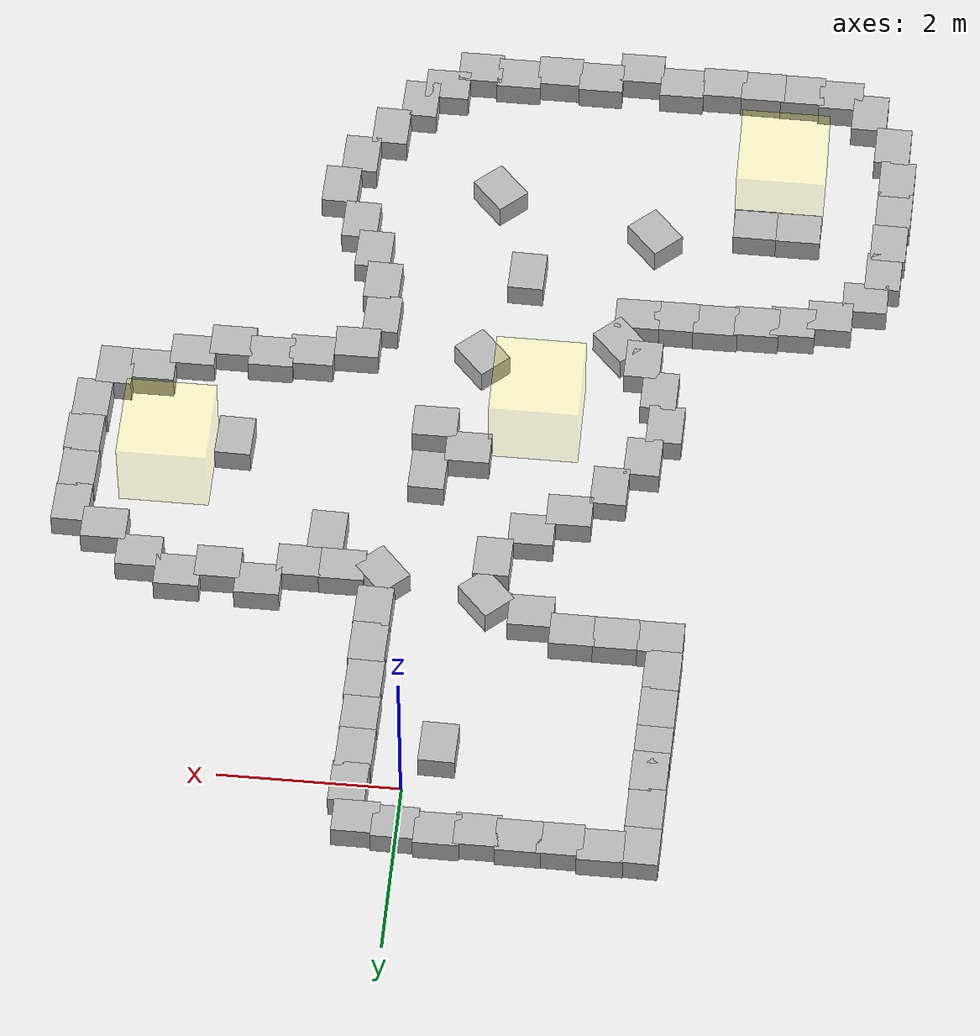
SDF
<sdf version="1.6">
 <world name="default">
  <light name="sun" type="directional">
   <pose>0 0 10 0 -0 0</pose>
   <diffuse>0.8 0.8 0.8 1</diffuse>
   <specular>0.2 0.2 0.2 1</specular>
   <attenuation>
    <range>1000</range>
    <constant>0.9</constant>
    <linear>0.01</linear>
    <quadratic>0.001</quadratic>
   </attenuation>
   <direction>-0.5 0.1 -0.9</direction>
  </light>
  <gravity>0 0 -9.8</gravity>
  <magnetic_field>6e-06 2.3e-05 -4.2e-05</magnetic_field>
  <atmosphere type="adiabatic"/>
  <physics name="default_physics" default="0" type="ode">
   <max_step_size>0.001</max_step_size>
   <real_time_factor>1</real_time_factor>
   <real_time_update_rate>1000</real_time_update_rate>
  </physics>
  <scene><ambient>0.4 0.4 0.4 1</ambient><background>0.7 0.7 0.7 1</background><shadows>1</shadows></scene>
  <audio><device>default</device></audio>
  <spherical_coordinates>
   <surface_model>EARTH_WGS84</surface_model>
   <latitude_deg>0</latitude_deg>
   <longitude_deg>0</longitude_deg>
   <elevation>0</elevation>
   <heading_deg>0</heading_deg>
  </spherical_coordinates>
  <model name="ground_plane">
   <static>1</static>
   <link name="link">
    <collision name="collision">
     <geometry><plane><normal>0 0 1</normal><size>100 100</size></plane></geometry>
     <surface>
      <contact><collide_bitmask>65535</collide_bitmask></contact>
      <friction><ode><mu>100</mu><mu2>50</mu2></ode></friction>
     </surface>
    </collision>
    <visual name="visual">
     <cast_shadows>0</cast_shadows>
     <geometry><plane><normal>0 0 1</normal><size>100 100</size></plane></geometry>
     <material>
      <script><uri>file://media/materials/scripts/gazebo.material</uri><name>Gazebo/Grey</name></script>
     </material>
    </visual>
   </link>
   <pose>0.215037 0.234206 0 0 -0 0</pose>
  </model>
  <model name="RegionEventBox_clone_0_clone">
   <static>1</static>
   <pose>3.01485 -4.05142 0 0 -0 0</pose>
   <link name="link">
    <visual name="visual">
     <transparency>0.75</transparency>
     <geometry><box><size>1 1 1.75</size></box></geometry>
     <material>
      <script><uri>file://media/materials/scripts/gazebo.material</uri><name>Gazebo/Yellow</name></script>
     </material>
    </visual>
   </link>
   <plugin name="region_event_box" filename="libRegionEventBoxPlugin.so">
    <event><name>model_in_region_event_box</name><type>inclusion</type><active>1</active></event>
   </plugin>
  </model>
  <model name="RegionEventBox_clone_0_clone_clone_0_clone_clone">
   <static>1</static>
   <pose>-1.01241 -5.02399 0 0 -0 0</pose>
   <link name="link">
    <visual name="visual">
     <transparency>0.75</transparency>
     <geometry><box><size>1 1 1.75</size></box></geometry>
     <material>
      <script><uri>file://media/materials/scripts/gazebo.material</uri><name>Gazebo/Yellow</name></script>
     </material>
    </visual>
   </link>
   <plugin name="region_event_box" filename="libRegionEventBoxPlugin.so">
    <event><name>model_in_region_event_box</name><type>inclusion</type><active>1</active></event>
   </plugin>
  </model>
  <model name="box_clone_3">
   <link name="cardboard_box_clone::link">
    <inertial>
     <mass>2</mass>
     <inertia>
      <ixx>0.0416667</ixx>
      <ixy>0</ixy>
      <ixz>0</ixz>
      <iyy>0.0566667</iyy>
      <iyz>0</iyz>
      <izz>0.0683333</izz>
     </inertia>
    </inertial>
    <visual name="visual">
     <pose>0 0 -0.15 0 -0 0</pose>
     <geometry>
      <mesh><uri>model://cardboard_box/meshes/cardboard_box.dae</uri><scale>1.25932 1.00745 0.755591</scale></mesh>
     </geometry>
    </visual>
    <collision name="collision">
     <geometry><box><size>0.5 0.4 0.3</size></box></geometry>
     <surface>
      <friction>
       <ode><mu>1</mu><mu2>1</mu2><fdir1>0 0 0</fdir1><slip1>0</slip1><slip2>0</slip2></ode>
       <torsional>
        <coefficient>1</coefficient>
        <patch_radius>0</patch_radius>
        <surface_radius>0</surface_radius>
        <use_patch_radius>1</use_patch_radius>
        <ode><slip>0</slip></ode>
       </torsional>
      </friction>
      <bounce><restitution_coefficient>0</restitution_coefficient><threshold>1e+06</threshold></bounce>
      <contact>
       <collide_without_contact>0</collide_without_contact>
       <collide_without_contact_bitmask>1</collide_without_contact_bitmask>
       <collide_bitmask>1</collide_bitmask>
       <ode>
        <soft_cfm>0</soft_cfm>
        <soft_erp>0.2</soft_erp>
        <kp>1e+07</kp>
        <kd>1</kd>
        <max_vel>0.1</max_vel>
        <min_depth>0.001</min_depth>
       </ode>
       <bullet>
        <split_impulse>1</split_impulse>
        <split_impulse_penetration_threshold>-0.01</split_impulse_penetration_threshold>
        <soft_cfm>0</soft_cfm>
        <soft_erp>0.2</soft_erp>
        <kp>1e+07</kp>
        <kd>1</kd>
       </bullet>
      </contact>
     </surface>
    </collision>
   </link>
   <static>1</static>
   <pose>-2.67175 -0.660249 0.149 0 -0 1.55153</pose>
  </model>
  <model name="box_clone_3_clone">
   <link name="cardboard_box_clone::link">
    <inertial>
     <mass>2</mass>
     <inertia>
      <ixx>0.0416667</ixx>
      <ixy>0</ixy>
      <ixz>0</ixz>
      <iyy>0.0566667</iyy>
      <iyz>0</iyz>
      <izz>0.0683333</izz>
     </inertia>
    </inertial>
    <visual name="visual">
     <pose>0 0 -0.15 0 -0 0</pose>
     <geometry>
      <mesh><uri>model://cardboard_box/meshes/cardboard_box.dae</uri><scale>1.25932 1.00745 0.755591</scale></mesh>
     </geometry>
    </visual>
    <collision name="collision">
     <geometry><box><size>0.5 0.4 0.3</size></box></geometry>
     <surface>
      <friction>
       <ode><mu>1</mu><mu2>1</mu2><fdir1>0 0 0</fdir1><slip1>0</slip1><slip2>0</slip2></ode>
       <torsional>
        <coefficient>1</coefficient>
        <patch_radius>0</patch_radius>
        <surface_radius>0</surface_radius>
        <use_patch_radius>1</use_patch_radius>
        <ode><slip>0</slip></ode>
       </torsional>
      </friction>
      <bounce><restitution_coefficient>0</restitution_coefficient><threshold>1e+06</threshold></bounce>
      <contact>
       <collide_without_contact>0</collide_without_contact>
       <collide_without_contact_bitmask>1</collide_without_contact_bitmask>
       <collide_bitmask>1</collide_bitmask>
       <ode>
        <soft_cfm>0</soft_cfm>
        <soft_erp>0.2</soft_erp>
        <kp>1e+07</kp>
        <kd>1</kd>
        <max_vel>0.1</max_vel>
        <min_depth>0.001</min_depth>
       </ode>
       <bullet>
        <split_impulse>1</split_impulse>
        <split_impulse_penetration_threshold>-0.01</split_impulse_penetration_threshold>
        <soft_cfm>0</soft_cfm>
        <soft_erp>0.2</soft_erp>
        <kp>1e+07</kp>
        <kd>1</kd>
       </bullet>
      </contact>
     </surface>
    </collision>
   </link>
   <static>1</static>
   <pose>-2.66078 -0.304132 0.149 0 -0 1.55153</pose>
  </model>
  <model name="box_clone_3_clone_0">
   <link name="cardboard_box_clone::link">
    <inertial>
     <mass>2</mass>
     <inertia>
      <ixx>0.0416667</ixx>
      <ixy>0</ixy>
      <ixz>0</ixz>
      <iyy>0.0566667</iyy>
      <iyz>0</iyz>
      <izz>0.0683333</izz>
     </inertia>
    </inertial>
    <visual name="visual">
     <pose>0 0 -0.15 0 -0 0</pose>
     <geometry>
      <mesh><uri>model://cardboard_box/meshes/cardboard_box.dae</uri><scale>1.25932 1.00745 0.755591</scale></mesh>
     </geometry>
    </visual>
    <collision name="collision">
     <geometry><box><size>0.5 0.4 0.3</size></box></geometry>
     <surface>
      <friction>
       <ode><mu>1</mu><mu2>1</mu2><fdir1>0 0 0</fdir1><slip1>0</slip1><slip2>0</slip2></ode>
       <torsional>
        <coefficient>1</coefficient>
        <patch_radius>0</patch_radius>
        <surface_radius>0</surface_radius>
        <use_patch_radius>1</use_patch_radius>
        <ode><slip>0</slip></ode>
       </torsional>
      </friction>
      <bounce><restitution_coefficient>0</restitution_coefficient><threshold>1e+06</threshold></bounce>
      <contact>
       <collide_without_contact>0</collide_without_contact>
       <collide_without_contact_bitmask>1</collide_without_contact_bitmask>
       <collide_bitmask>1</collide_bitmask>
       <ode>
        <soft_cfm>0</soft_cfm>
        <soft_erp>0.2</soft_erp>
        <kp>1e+07</kp>
        <kd>1</kd>
        <max_vel>0.1</max_vel>
        <min_depth>0.001</min_depth>
       </ode>
       <bullet>
        <split_impulse>1</split_impulse>
        <split_impulse_penetration_threshold>-0.01</split_impulse_penetration_threshold>
        <soft_cfm>0</soft_cfm>
        <soft_erp>0.2</soft_erp>
        <kp>1e+07</kp>
        <kd>1</kd>
       </bullet>
      </contact>
     </surface>
    </collision>
   </link>
   <static>1</static>
   <pose>-2.68128 -1.13471 0.149 0 -0 1.55153</pose>
  </model>
  <model name="box_clone_3_clone_1">
   <link name="cardboard_box_clone::link">
    <inertial>
     <mass>2</mass>
     <inertia>
      <ixx>0.0416667</ixx>
      <ixy>0</ixy>
      <ixz>0</ixz>
      <iyy>0.0566667</iyy>
      <iyz>0</iyz>
      <izz>0.0683333</izz>
     </inertia>
    </inertial>
    <visual name="visual">
     <pose>0 0 -0.15 0 -0 0</pose>
     <geometry>
      <mesh><uri>model://cardboard_box/meshes/cardboard_box.dae</uri><scale>1.25932 1.00745 0.755591</scale></mesh>
     </geometry>
    </visual>
    <collision name="collision">
     <geometry><box><size>0.5 0.4 0.3</size></box></geometry>
     <surface>
      <friction>
       <ode><mu>1</mu><mu2>1</mu2><fdir1>0 0 0</fdir1><slip1>0</slip1><slip2>0</slip2></ode>
       <torsional>
        <coefficient>1</coefficient>
        <patch_radius>0</patch_radius>
        <surface_radius>0</surface_radius>
        <use_patch_radius>1</use_patch_radius>
        <ode><slip>0</slip></ode>
       </torsional>
      </friction>
      <bounce><restitution_coefficient>0</restitution_coefficient><threshold>1e+06</threshold></bounce>
      <contact>
       <collide_without_contact>0</collide_without_contact>
       <collide_without_contact_bitmask>1</collide_without_contact_bitmask>
       <collide_bitmask>1</collide_bitmask>
       <ode>
        <soft_cfm>0</soft_cfm>
        <soft_erp>0.2</soft_erp>
        <kp>1e+07</kp>
        <kd>1</kd>
        <max_vel>0.1</max_vel>
        <min_depth>0.001</min_depth>
       </ode>
       <bullet>
        <split_impulse>1</split_impulse>
        <split_impulse_penetration_threshold>-0.01</split_impulse_penetration_threshold>
        <soft_cfm>0</soft_cfm>
        <soft_erp>0.2</soft_erp>
        <kp>1e+07</kp>
        <kd>1</kd>
       </bullet>
      </contact>
     </surface>
    </collision>
   </link>
   <static>1</static>
   <pose>-2.68961 -1.61993 0.149 0 -0 1.55153</pose>
  </model>
  <model name="box_clone_2_clone">
   <link name="cardboard_box_clone::link">
    <inertial>
     <mass>2</mass>
     <inertia>
      <ixx>0.0416667</ixx>
      <ixy>0</ixy>
      <ixz>0</ixz>
      <iyy>0.0566667</iyy>
      <iyz>0</iyz>
      <izz>0.0683333</izz>
     </inertia>
    </inertial>
    <visual name="visual">
     <pose>0 0 -0.15 0 -0 0</pose>
     <geometry>
      <mesh><uri>model://cardboard_box/meshes/cardboard_box.dae</uri><scale>1.25932 1.00745 0.755591</scale></mesh>
     </geometry>
    </visual>
    <collision name="collision">
     <geometry><box><size>0.5 0.4 0.3</size></box></geometry>
     <surface>
      <friction>
       <ode><mu>1</mu><mu2>1</mu2><fdir1>0 0 0</fdir1><slip1>0</slip1><slip2>0</slip2></ode>
       <torsional>
        <coefficient>1</coefficient>
        <patch_radius>0</patch_radius>
        <surface_radius>0</surface_radius>
        <use_patch_radius>1</use_patch_radius>
        <ode><slip>0</slip></ode>
       </torsional>
      </friction>
      <bounce><restitution_coefficient>0</restitution_coefficient><threshold>1e+06</threshold></bounce>
      <contact>
       <collide_without_contact>0</collide_without_contact>
       <collide_without_contact_bitmask>1</collide_without_contact_bitmask>
       <collide_bitmask>1</collide_bitmask>
       <ode>
        <soft_cfm>0</soft_cfm>
        <soft_erp>0.2</soft_erp>
        <kp>1e+07</kp>
        <kd>1</kd>
        <max_vel>0.1</max_vel>
        <min_depth>0.001</min_depth>
       </ode>
       <bullet>
        <split_impulse>1</split_impulse>
        <split_impulse_penetration_threshold>-0.01</split_impulse_penetration_threshold>
        <soft_cfm>0</soft_cfm>
        <soft_erp>0.2</soft_erp>
        <kp>1e+07</kp>
        <kd>1</kd>
       </bullet>
      </contact>
     </surface>
    </collision>
   </link>
   <static>1</static>
   <pose>-2.64031 -2.04978 0.149 0 -0 0</pose>
  </model>
  <model name="box_clone_2_clone_0">
   <link name="cardboard_box_clone::link">
    <inertial>
     <mass>2</mass>
     <inertia>
      <ixx>0.0416667</ixx>
      <ixy>0</ixy>
      <ixz>0</ixz>
      <iyy>0.0566667</iyy>
      <iyz>0</iyz>
      <izz>0.0683333</izz>
     </inertia>
    </inertial>
    <visual name="visual">
     <pose>0 0 -0.15 0 -0 0</pose>
     <geometry>
      <mesh><uri>model://cardboard_box/meshes/cardboard_box.dae</uri><scale>1.25932 1.00745 0.755591</scale></mesh>
     </geometry>
    </visual>
    <collision name="collision">
     <geometry><box><size>0.5 0.4 0.3</size></box></geometry>
     <surface>
      <friction>
       <ode><mu>1</mu><mu2>1</mu2><fdir1>0 0 0</fdir1><slip1>0</slip1><slip2>0</slip2></ode>
       <torsional>
        <coefficient>1</coefficient>
        <patch_radius>0</patch_radius>
        <surface_radius>0</surface_radius>
        <use_patch_radius>1</use_patch_radius>
        <ode><slip>0</slip></ode>
       </torsional>
      </friction>
      <bounce><restitution_coefficient>0</restitution_coefficient><threshold>1e+06</threshold></bounce>
      <contact>
       <collide_without_contact>0</collide_without_contact>
       <collide_without_contact_bitmask>1</collide_without_contact_bitmask>
       <collide_bitmask>1</collide_bitmask>
       <ode>
        <soft_cfm>0</soft_cfm>
        <soft_erp>0.2</soft_erp>
        <kp>1e+07</kp>
        <kd>1</kd>
        <max_vel>0.1</max_vel>
        <min_depth>0.001</min_depth>
       </ode>
       <bullet>
        <split_impulse>1</split_impulse>
        <split_impulse_penetration_threshold>-0.01</split_impulse_penetration_threshold>
        <soft_cfm>0</soft_cfm>
        <soft_erp>0.2</soft_erp>
        <kp>1e+07</kp>
        <kd>1</kd>
       </bullet>
      </contact>
     </surface>
    </collision>
   </link>
   <static>1</static>
   <pose>-2.1539 -2.05558 0.149 0 -0 0</pose>
  </model>
  <model name="box_clone_2_clone_1">
   <link name="cardboard_box_clone::link">
    <inertial>
     <mass>2</mass>
     <inertia>
      <ixx>0.0416667</ixx>
      <ixy>0</ixy>
      <ixz>0</ixz>
      <iyy>0.0566667</iyy>
      <iyz>0</iyz>
      <izz>0.0683333</izz>
     </inertia>
    </inertial>
    <visual name="visual">
     <pose>0 0 -0.15 0 -0 0</pose>
     <geometry>
      <mesh><uri>model://cardboard_box/meshes/cardboard_box.dae</uri><scale>1.25932 1.00745 0.755591</scale></mesh>
     </geometry>
    </visual>
    <collision name="collision">
     <geometry><box><size>0.5 0.4 0.3</size></box></geometry>
     <surface>
      <friction>
       <ode><mu>1</mu><mu2>1</mu2><fdir1>0 0 0</fdir1><slip1>0</slip1><slip2>0</slip2></ode>
       <torsional>
        <coefficient>1</coefficient>
        <patch_radius>0</patch_radius>
        <surface_radius>0</surface_radius>
        <use_patch_radius>1</use_patch_radius>
        <ode><slip>0</slip></ode>
       </torsional>
      </friction>
      <bounce><restitution_coefficient>0</restitution_coefficient><threshold>1e+06</threshold></bounce>
      <contact>
       <collide_without_contact>0</collide_without_contact>
       <collide_without_contact_bitmask>1</collide_without_contact_bitmask>
       <collide_bitmask>1</collide_bitmask>
       <ode>
        <soft_cfm>0</soft_cfm>
        <soft_erp>0.2</soft_erp>
        <kp>1e+07</kp>
        <kd>1</kd>
        <max_vel>0.1</max_vel>
        <min_depth>0.001</min_depth>
       </ode>
       <bullet>
        <split_impulse>1</split_impulse>
        <split_impulse_penetration_threshold>-0.01</split_impulse_penetration_threshold>
        <soft_cfm>0</soft_cfm>
        <soft_erp>0.2</soft_erp>
        <kp>1e+07</kp>
        <kd>1</kd>
       </bullet>
      </contact>
     </surface>
    </collision>
   </link>
   <static>1</static>
   <pose>-1.67344 -2.05843 0.149 0 -0 0</pose>
  </model>
  <model name="box_clone_3_clone_clone">
   <link name="cardboard_box_clone::link">
    <inertial>
     <mass>2</mass>
     <inertia>
      <ixx>0.0416667</ixx>
      <ixy>0</ixy>
      <ixz>0</ixz>
      <iyy>0.0566667</iyy>
      <iyz>0</iyz>
      <izz>0.0683333</izz>
     </inertia>
    </inertial>
    <visual name="visual">
     <pose>0 0 -0.15 0 -0 0</pose>
     <geometry>
      <mesh><uri>model://cardboard_box/meshes/cardboard_box.dae</uri><scale>1.25932 1.00745 0.755591</scale></mesh>
     </geometry>
    </visual>
    <collision name="collision">
     <geometry><box><size>0.5 0.4 0.3</size></box></geometry>
     <surface>
      <friction>
       <ode><mu>1</mu><mu2>1</mu2><fdir1>0 0 0</fdir1><slip1>0</slip1><slip2>0</slip2></ode>
       <torsional>
        <coefficient>1</coefficient>
        <patch_radius>0</patch_radius>
        <surface_radius>0</surface_radius>
        <use_patch_radius>1</use_patch_radius>
        <ode><slip>0</slip></ode>
       </torsional>
      </friction>
      <bounce><restitution_coefficient>0</restitution_coefficient><threshold>1e+06</threshold></bounce>
      <contact>
       <collide_without_contact>0</collide_without_contact>
       <collide_without_contact_bitmask>1</collide_without_contact_bitmask>
       <collide_bitmask>1</collide_bitmask>
       <ode>
        <soft_cfm>0</soft_cfm>
        <soft_erp>0.2</soft_erp>
        <kp>1e+07</kp>
        <kd>1</kd>
        <max_vel>0.1</max_vel>
        <min_depth>0.001</min_depth>
       </ode>
       <bullet>
        <split_impulse>1</split_impulse>
        <split_impulse_penetration_threshold>-0.01</split_impulse_penetration_threshold>
        <soft_cfm>0</soft_cfm>
        <soft_erp>0.2</soft_erp>
        <kp>1e+07</kp>
        <kd>1</kd>
       </bullet>
      </contact>
     </surface>
    </collision>
   </link>
   <static>1</static>
   <pose>0.525405 -0.308483 0.149 0 -0 1.55153</pose>
  </model>
  <model name="box_clone_3_clone_clone_clone">
   <link name="cardboard_box_clone::link">
    <inertial>
     <mass>2</mass>
     <inertia>
      <ixx>0.0416667</ixx>
      <ixy>0</ixy>
      <ixz>0</ixz>
      <iyy>0.0566667</iyy>
      <iyz>0</iyz>
      <izz>0.0683333</izz>
     </inertia>
    </inertial>
    <visual name="visual">
     <pose>0 0 -0.15 0 -0 0</pose>
     <geometry>
      <mesh><uri>model://cardboard_box/meshes/cardboard_box.dae</uri><scale>1.25932 1.00745 0.755591</scale></mesh>
     </geometry>
    </visual>
    <collision name="collision">
     <geometry><box><size>0.5 0.4 0.3</size></box></geometry>
     <surface>
      <friction>
       <ode><mu>1</mu><mu2>1</mu2><fdir1>0 0 0</fdir1><slip1>0</slip1><slip2>0</slip2></ode>
       <torsional>
        <coefficient>1</coefficient>
        <patch_radius>0</patch_radius>
        <surface_radius>0</surface_radius>
        <use_patch_radius>1</use_patch_radius>
        <ode><slip>0</slip></ode>
       </torsional>
      </friction>
      <bounce><restitution_coefficient>0</restitution_coefficient><threshold>1e+06</threshold></bounce>
      <contact>
       <collide_without_contact>0</collide_without_contact>
       <collide_without_contact_bitmask>1</collide_without_contact_bitmask>
       <collide_bitmask>1</collide_bitmask>
       <ode>
        <soft_cfm>0</soft_cfm>
        <soft_erp>0.2</soft_erp>
        <kp>1e+07</kp>
        <kd>1</kd>
        <max_vel>0.1</max_vel>
        <min_depth>0.001</min_depth>
       </ode>
       <bullet>
        <split_impulse>1</split_impulse>
        <split_impulse_penetration_threshold>-0.01</split_impulse_penetration_threshold>
        <soft_cfm>0</soft_cfm>
        <soft_erp>0.2</soft_erp>
        <kp>1e+07</kp>
        <kd>1</kd>
       </bullet>
      </contact>
     </surface>
    </collision>
   </link>
   <static>1</static>
   <pose>0.521071 -0.766393 0.149 0 -0 1.55153</pose>
  </model>
  <model name="box_clone_3_clone_clone_clone_0">
   <link name="cardboard_box_clone::link">
    <inertial>
     <mass>2</mass>
     <inertia>
      <ixx>0.0416667</ixx>
      <ixy>0</ixy>
      <ixz>0</ixz>
      <iyy>0.0566667</iyy>
      <iyz>0</iyz>
      <izz>0.0683333</izz>
     </inertia>
    </inertial>
    <visual name="visual">
     <pose>0 0 -0.15 0 -0 0</pose>
     <geometry>
      <mesh><uri>model://cardboard_box/meshes/cardboard_box.dae</uri><scale>1.25932 1.00745 0.755591</scale></mesh>
     </geometry>
    </visual>
    <collision name="collision">
     <geometry><box><size>0.5 0.4 0.3</size></box></geometry>
     <surface>
      <friction>
       <ode><mu>1</mu><mu2>1</mu2><fdir1>0 0 0</fdir1><slip1>0</slip1><slip2>0</slip2></ode>
       <torsional>
        <coefficient>1</coefficient>
        <patch_radius>0</patch_radius>
        <surface_radius>0</surface_radius>
        <use_patch_radius>1</use_patch_radius>
        <ode><slip>0</slip></ode>
       </torsional>
      </friction>
      <bounce><restitution_coefficient>0</restitution_coefficient><threshold>1e+06</threshold></bounce>
      <contact>
       <collide_without_contact>0</collide_without_contact>
       <collide_without_contact_bitmask>1</collide_without_contact_bitmask>
       <collide_bitmask>1</collide_bitmask>
       <ode>
        <soft_cfm>0</soft_cfm>
        <soft_erp>0.2</soft_erp>
        <kp>1e+07</kp>
        <kd>1</kd>
        <max_vel>0.1</max_vel>
        <min_depth>0.001</min_depth>
       </ode>
       <bullet>
        <split_impulse>1</split_impulse>
        <split_impulse_penetration_threshold>-0.01</split_impulse_penetration_threshold>
        <soft_cfm>0</soft_cfm>
        <soft_erp>0.2</soft_erp>
        <kp>1e+07</kp>
        <kd>1</kd>
       </bullet>
      </contact>
     </surface>
    </collision>
   </link>
   <static>1</static>
   <pose>0.524186 -1.22775 0.149 0 -0 1.55153</pose>
  </model>
  <model name="box_clone_3_clone_clone_clone_1">
   <link name="cardboard_box_clone::link">
    <inertial>
     <mass>2</mass>
     <inertia>
      <ixx>0.0416667</ixx>
      <ixy>0</ixy>
      <ixz>0</ixz>
      <iyy>0.0566667</iyy>
      <iyz>0</iyz>
      <izz>0.0683333</izz>
     </inertia>
    </inertial>
    <visual name="visual">
     <pose>0 0 -0.15 0 -0 0</pose>
     <geometry>
      <mesh><uri>model://cardboard_box/meshes/cardboard_box.dae</uri><scale>1.25932 1.00745 0.755591</scale></mesh>
     </geometry>
    </visual>
    <collision name="collision">
     <geometry><box><size>0.5 0.4 0.3</size></box></geometry>
     <surface>
      <friction>
       <ode><mu>1</mu><mu2>1</mu2><fdir1>0 0 0</fdir1><slip1>0</slip1><slip2>0</slip2></ode>
       <torsional>
        <coefficient>1</coefficient>
        <patch_radius>0</patch_radius>
        <surface_radius>0</surface_radius>
        <use_patch_radius>1</use_patch_radius>
        <ode><slip>0</slip></ode>
       </torsional>
      </friction>
      <bounce><restitution_coefficient>0</restitution_coefficient><threshold>1e+06</threshold></bounce>
      <contact>
       <collide_without_contact>0</collide_without_contact>
       <collide_without_contact_bitmask>1</collide_without_contact_bitmask>
       <collide_bitmask>1</collide_bitmask>
       <ode>
        <soft_cfm>0</soft_cfm>
        <soft_erp>0.2</soft_erp>
        <kp>1e+07</kp>
        <kd>1</kd>
        <max_vel>0.1</max_vel>
        <min_depth>0.001</min_depth>
       </ode>
       <bullet>
        <split_impulse>1</split_impulse>
        <split_impulse_penetration_threshold>-0.01</split_impulse_penetration_threshold>
        <soft_cfm>0</soft_cfm>
        <soft_erp>0.2</soft_erp>
        <kp>1e+07</kp>
        <kd>1</kd>
       </bullet>
      </contact>
     </surface>
    </collision>
   </link>
   <static>1</static>
   <pose>0.528427 -1.69636 0.149 0 -0 1.55153</pose>
  </model>
  <model name="box_clone_3_clone_clone_clone_2">
   <link name="cardboard_box_clone::link">
    <inertial>
     <mass>2</mass>
     <inertia>
      <ixx>0.0416667</ixx>
      <ixy>0</ixy>
      <ixz>0</ixz>
      <iyy>0.0566667</iyy>
      <iyz>0</iyz>
      <izz>0.0683333</izz>
     </inertia>
    </inertial>
    <visual name="visual">
     <pose>0 0 -0.15 0 -0 0</pose>
     <geometry>
      <mesh><uri>model://cardboard_box/meshes/cardboard_box.dae</uri><scale>1.25932 1.00745 0.755591</scale></mesh>
     </geometry>
    </visual>
    <collision name="collision">
     <geometry><box><size>0.5 0.4 0.3</size></box></geometry>
     <surface>
      <friction>
       <ode><mu>1</mu><mu2>1</mu2><fdir1>0 0 0</fdir1><slip1>0</slip1><slip2>0</slip2></ode>
       <torsional>
        <coefficient>1</coefficient>
        <patch_radius>0</patch_radius>
        <surface_radius>0</surface_radius>
        <use_patch_radius>1</use_patch_radius>
        <ode><slip>0</slip></ode>
       </torsional>
      </friction>
      <bounce><restitution_coefficient>0</restitution_coefficient><threshold>1e+06</threshold></bounce>
      <contact>
       <collide_without_contact>0</collide_without_contact>
       <collide_without_contact_bitmask>1</collide_without_contact_bitmask>
       <collide_bitmask>1</collide_bitmask>
       <ode>
        <soft_cfm>0</soft_cfm>
        <soft_erp>0.2</soft_erp>
        <kp>1e+07</kp>
        <kd>1</kd>
        <max_vel>0.1</max_vel>
        <min_depth>0.001</min_depth>
       </ode>
       <bullet>
        <split_impulse>1</split_impulse>
        <split_impulse_penetration_threshold>-0.01</split_impulse_penetration_threshold>
        <soft_cfm>0</soft_cfm>
        <soft_erp>0.2</soft_erp>
        <kp>1e+07</kp>
        <kd>1</kd>
       </bullet>
      </contact>
     </surface>
    </collision>
   </link>
   <static>1</static>
   <pose>0.52335 -2.17334 0.149 0 -0 1.55153</pose>
  </model>
  <model name="box_clone_3_clone_clone_clone_5">
   <link name="cardboard_box_clone::link">
    <inertial>
     <mass>2</mass>
     <inertia>
      <ixx>0.0416667</ixx>
      <ixy>0</ixy>
      <ixz>0</ixz>
      <iyy>0.0566667</iyy>
      <iyz>0</iyz>
      <izz>0.0683333</izz>
     </inertia>
    </inertial>
    <visual name="visual">
     <pose>0 0 -0.15 0 -0 0</pose>
     <geometry>
      <mesh><uri>model://cardboard_box/meshes/cardboard_box.dae</uri><scale>1.25932 1.00745 0.755591</scale></mesh>
     </geometry>
    </visual>
    <collision name="collision">
     <geometry><box><size>0.5 0.4 0.3</size></box></geometry>
     <surface>
      <friction>
       <ode><mu>1</mu><mu2>1</mu2><fdir1>0 0 0</fdir1><slip1>0</slip1><slip2>0</slip2></ode>
       <torsional>
        <coefficient>1</coefficient>
        <patch_radius>0</patch_radius>
        <surface_radius>0</surface_radius>
        <use_patch_radius>1</use_patch_radius>
        <ode><slip>0</slip></ode>
       </torsional>
      </friction>
      <bounce><restitution_coefficient>0</restitution_coefficient><threshold>1e+06</threshold></bounce>
      <contact>
       <collide_without_contact>0</collide_without_contact>
       <collide_without_contact_bitmask>1</collide_without_contact_bitmask>
       <collide_bitmask>1</collide_bitmask>
       <ode>
        <soft_cfm>0</soft_cfm>
        <soft_erp>0.2</soft_erp>
        <kp>1e+07</kp>
        <kd>1</kd>
        <max_vel>0.1</max_vel>
        <min_depth>0.001</min_depth>
       </ode>
       <bullet>
        <split_impulse>1</split_impulse>
        <split_impulse_penetration_threshold>-0.01</split_impulse_penetration_threshold>
        <soft_cfm>0</soft_cfm>
        <soft_erp>0.2</soft_erp>
        <kp>1e+07</kp>
        <kd>1</kd>
       </bullet>
      </contact>
     </surface>
    </collision>
   </link>
   <static>1</static>
   <pose>-0.716717 -2.94851 0.149 0 -0 1.55153</pose>
  </model>
  <model name="box_clone_3_clone_clone_clone_5_clone">
   <link name="cardboard_box_clone::link">
    <inertial>
     <mass>2</mass>
     <inertia>
      <ixx>0.0416667</ixx>
      <ixy>0</ixy>
      <ixz>0</ixz>
      <iyy>0.0566667</iyy>
      <iyz>0</iyz>
      <izz>0.0683333</izz>
     </inertia>
    </inertial>
    <visual name="visual">
     <pose>0 0 -0.15 0 -0 0</pose>
     <geometry>
      <mesh><uri>model://cardboard_box/meshes/cardboard_box.dae</uri><scale>1.25932 1.00745 0.755591</scale></mesh>
     </geometry>
    </visual>
    <collision name="collision">
     <geometry><box><size>0.5 0.4 0.3</size></box></geometry>
     <surface>
      <friction>
       <ode><mu>1</mu><mu2>1</mu2><fdir1>0 0 0</fdir1><slip1>0</slip1><slip2>0</slip2></ode>
       <torsional>
        <coefficient>1</coefficient>
        <patch_radius>0</patch_radius>
        <surface_radius>0</surface_radius>
        <use_patch_radius>1</use_patch_radius>
        <ode><slip>0</slip></ode>
       </torsional>
      </friction>
      <bounce><restitution_coefficient>0</restitution_coefficient><threshold>1e+06</threshold></bounce>
      <contact>
       <collide_without_contact>0</collide_without_contact>
       <collide_without_contact_bitmask>1</collide_without_contact_bitmask>
       <collide_bitmask>1</collide_bitmask>
       <ode>
        <soft_cfm>0</soft_cfm>
        <soft_erp>0.2</soft_erp>
        <kp>1e+07</kp>
        <kd>1</kd>
        <max_vel>0.1</max_vel>
        <min_depth>0.001</min_depth>
       </ode>
       <bullet>
        <split_impulse>1</split_impulse>
        <split_impulse_penetration_threshold>-0.01</split_impulse_penetration_threshold>
        <soft_cfm>0</soft_cfm>
        <soft_erp>0.2</soft_erp>
        <kp>1e+07</kp>
        <kd>1</kd>
       </bullet>
      </contact>
     </surface>
    </collision>
   </link>
   <static>1</static>
   <pose>0.112115 -4.04552 0.149 0 -0 1.55153</pose>
  </model>
  <model name="box_clone_1_clone">
   <link name="cardboard_box_clone::link">
    <inertial>
     <mass>2</mass>
     <inertia>
      <ixx>0.0416667</ixx>
      <ixy>0</ixy>
      <ixz>0</ixz>
      <iyy>0.0566667</iyy>
      <iyz>0</iyz>
      <izz>0.0683333</izz>
     </inertia>
    </inertial>
    <visual name="visual">
     <pose>0 0 -0.15 0 -0 0</pose>
     <geometry>
      <mesh><uri>model://cardboard_box/meshes/cardboard_box.dae</uri><scale>1.25932 1.00745 0.755591</scale></mesh>
     </geometry>
    </visual>
    <collision name="collision">
     <geometry><box><size>0.5 0.4 0.3</size></box></geometry>
     <surface>
      <friction>
       <ode><mu>1</mu><mu2>1</mu2><fdir1>0 0 0</fdir1><slip1>0</slip1><slip2>0</slip2></ode>
       <torsional>
        <coefficient>1</coefficient>
        <patch_radius>0</patch_radius>
        <surface_radius>0</surface_radius>
        <use_patch_radius>1</use_patch_radius>
        <ode><slip>0</slip></ode>
       </torsional>
      </friction>
      <bounce><restitution_coefficient>0</restitution_coefficient><threshold>1e+06</threshold></bounce>
      <contact>
       <collide_without_contact>0</collide_without_contact>
       <collide_without_contact_bitmask>1</collide_without_contact_bitmask>
       <collide_bitmask>1</collide_bitmask>
       <ode>
        <soft_cfm>0</soft_cfm>
        <soft_erp>0.2</soft_erp>
        <kp>1e+07</kp>
        <kd>1</kd>
        <max_vel>0.1</max_vel>
        <min_depth>0.001</min_depth>
       </ode>
       <bullet>
        <split_impulse>1</split_impulse>
        <split_impulse_penetration_threshold>-0.01</split_impulse_penetration_threshold>
        <soft_cfm>0</soft_cfm>
        <soft_erp>0.2</soft_erp>
        <kp>1e+07</kp>
        <kd>1</kd>
       </bullet>
      </contact>
     </surface>
    </collision>
   </link>
   <static>1</static>
   <pose>0.918792 -2.68698 0.149 0 -0 0</pose>
  </model>
  <model name="box_clone_1_clone_0">
   <link name="cardboard_box_clone::link">
    <inertial>
     <mass>2</mass>
     <inertia>
      <ixx>0.0416667</ixx>
      <ixy>0</ixy>
      <ixz>0</ixz>
      <iyy>0.0566667</iyy>
      <iyz>0</iyz>
      <izz>0.0683333</izz>
     </inertia>
    </inertial>
    <visual name="visual">
     <pose>0 0 -0.15 0 -0 0</pose>
     <geometry>
      <mesh><uri>model://cardboard_box/meshes/cardboard_box.dae</uri><scale>1.25932 1.00745 0.755591</scale></mesh>
     </geometry>
    </visual>
    <collision name="collision">
     <geometry><box><size>0.5 0.4 0.3</size></box></geometry>
     <surface>
      <friction>
       <ode><mu>1</mu><mu2>1</mu2><fdir1>0 0 0</fdir1><slip1>0</slip1><slip2>0</slip2></ode>
       <torsional>
        <coefficient>1</coefficient>
        <patch_radius>0</patch_radius>
        <surface_radius>0</surface_radius>
        <use_patch_radius>1</use_patch_radius>
        <ode><slip>0</slip></ode>
       </torsional>
      </friction>
      <bounce><restitution_coefficient>0</restitution_coefficient><threshold>1e+06</threshold></bounce>
      <contact>
       <collide_without_contact>0</collide_without_contact>
       <collide_without_contact_bitmask>1</collide_without_contact_bitmask>
       <collide_bitmask>1</collide_bitmask>
       <ode>
        <soft_cfm>0</soft_cfm>
        <soft_erp>0.2</soft_erp>
        <kp>1e+07</kp>
        <kd>1</kd>
        <max_vel>0.1</max_vel>
        <min_depth>0.001</min_depth>
       </ode>
       <bullet>
        <split_impulse>1</split_impulse>
        <split_impulse_penetration_threshold>-0.01</split_impulse_penetration_threshold>
        <soft_cfm>0</soft_cfm>
        <soft_erp>0.2</soft_erp>
        <kp>1e+07</kp>
        <kd>1</kd>
       </bullet>
      </contact>
     </surface>
    </collision>
   </link>
   <static>1</static>
   <pose>1.39196 -2.69378 0.149 0 -0 0</pose>
  </model>
  <model name="box_clone_1_clone_1">
   <link name="cardboard_box_clone::link">
    <inertial>
     <mass>2</mass>
     <inertia>
      <ixx>0.0416667</ixx>
      <ixy>0</ixy>
      <ixz>0</ixz>
      <iyy>0.0566667</iyy>
      <iyz>0</iyz>
      <izz>0.0683333</izz>
     </inertia>
    </inertial>
    <visual name="visual">
     <pose>0 0 -0.15 0 -0 0</pose>
     <geometry>
      <mesh><uri>model://cardboard_box/meshes/cardboard_box.dae</uri><scale>1.25932 1.00745 0.755591</scale></mesh>
     </geometry>
    </visual>
    <collision name="collision">
     <geometry><box><size>0.5 0.4 0.3</size></box></geometry>
     <surface>
      <friction>
       <ode><mu>1</mu><mu2>1</mu2><fdir1>0 0 0</fdir1><slip1>0</slip1><slip2>0</slip2></ode>
       <torsional>
        <coefficient>1</coefficient>
        <patch_radius>0</patch_radius>
        <surface_radius>0</surface_radius>
        <use_patch_radius>1</use_patch_radius>
        <ode><slip>0</slip></ode>
       </torsional>
      </friction>
      <bounce><restitution_coefficient>0</restitution_coefficient><threshold>1e+06</threshold></bounce>
      <contact>
       <collide_without_contact>0</collide_without_contact>
       <collide_without_contact_bitmask>1</collide_without_contact_bitmask>
       <collide_bitmask>1</collide_bitmask>
       <ode>
        <soft_cfm>0</soft_cfm>
        <soft_erp>0.2</soft_erp>
        <kp>1e+07</kp>
        <kd>1</kd>
        <max_vel>0.1</max_vel>
        <min_depth>0.001</min_depth>
       </ode>
       <bullet>
        <split_impulse>1</split_impulse>
        <split_impulse_penetration_threshold>-0.01</split_impulse_penetration_threshold>
        <soft_cfm>0</soft_cfm>
        <soft_erp>0.2</soft_erp>
        <kp>1e+07</kp>
        <kd>1</kd>
       </bullet>
      </contact>
     </surface>
    </collision>
   </link>
   <static>1</static>
   <pose>1.82358 -2.40857 0.149 0 -0 0</pose>
  </model>
  <model name="box_clone_1_clone_2">
   <link name="cardboard_box_clone::link">
    <inertial>
     <mass>2</mass>
     <inertia>
      <ixx>0.0416667</ixx>
      <ixy>0</ixy>
      <ixz>0</ixz>
      <iyy>0.0566667</iyy>
      <iyz>0</iyz>
      <izz>0.0683333</izz>
     </inertia>
    </inertial>
    <visual name="visual">
     <pose>0 0 -0.15 0 -0 0</pose>
     <geometry>
      <mesh><uri>model://cardboard_box/meshes/cardboard_box.dae</uri><scale>1.25932 1.00745 0.755591</scale></mesh>
     </geometry>
    </visual>
    <collision name="collision">
     <geometry><box><size>0.5 0.4 0.3</size></box></geometry>
     <surface>
      <friction>
       <ode><mu>1</mu><mu2>1</mu2><fdir1>0 0 0</fdir1><slip1>0</slip1><slip2>0</slip2></ode>
       <torsional>
        <coefficient>1</coefficient>
        <patch_radius>0</patch_radius>
        <surface_radius>0</surface_radius>
        <use_patch_radius>1</use_patch_radius>
        <ode><slip>0</slip></ode>
       </torsional>
      </friction>
      <bounce><restitution_coefficient>0</restitution_coefficient><threshold>1e+06</threshold></bounce>
      <contact>
       <collide_without_contact>0</collide_without_contact>
       <collide_without_contact_bitmask>1</collide_without_contact_bitmask>
       <collide_bitmask>1</collide_bitmask>
       <ode>
        <soft_cfm>0</soft_cfm>
        <soft_erp>0.2</soft_erp>
        <kp>1e+07</kp>
        <kd>1</kd>
        <max_vel>0.1</max_vel>
        <min_depth>0.001</min_depth>
       </ode>
       <bullet>
        <split_impulse>1</split_impulse>
        <split_impulse_penetration_threshold>-0.01</split_impulse_penetration_threshold>
        <soft_cfm>0</soft_cfm>
        <soft_erp>0.2</soft_erp>
        <kp>1e+07</kp>
        <kd>1</kd>
       </bullet>
      </contact>
     </surface>
    </collision>
   </link>
   <static>1</static>
   <pose>2.28024 -2.59219 0.149 0 -0 0</pose>
  </model>
  <model name="box_clone_1_clone_3">
   <link name="cardboard_box_clone::link">
    <inertial>
     <mass>2</mass>
     <inertia>
      <ixx>0.0416667</ixx>
      <ixy>0</ixy>
      <ixz>0</ixz>
      <iyy>0.0566667</iyy>
      <iyz>0</iyz>
      <izz>0.0683333</izz>
     </inertia>
    </inertial>
    <visual name="visual">
     <pose>0 0 -0.15 0 -0 0</pose>
     <geometry>
      <mesh><uri>model://cardboard_box/meshes/cardboard_box.dae</uri><scale>1.25932 1.00745 0.755591</scale></mesh>
     </geometry>
    </visual>
    <collision name="collision">
     <geometry><box><size>0.5 0.4 0.3</size></box></geometry>
     <surface>
      <friction>
       <ode><mu>1</mu><mu2>1</mu2><fdir1>0 0 0</fdir1><slip1>0</slip1><slip2>0</slip2></ode>
       <torsional>
        <coefficient>1</coefficient>
        <patch_radius>0</patch_radius>
        <surface_radius>0</surface_radius>
        <use_patch_radius>1</use_patch_radius>
        <ode><slip>0</slip></ode>
       </torsional>
      </friction>
      <bounce><restitution_coefficient>0</restitution_coefficient><threshold>1e+06</threshold></bounce>
      <contact>
       <collide_without_contact>0</collide_without_contact>
       <collide_without_contact_bitmask>1</collide_without_contact_bitmask>
       <collide_bitmask>1</collide_bitmask>
       <ode>
        <soft_cfm>0</soft_cfm>
        <soft_erp>0.2</soft_erp>
        <kp>1e+07</kp>
        <kd>1</kd>
        <max_vel>0.1</max_vel>
        <min_depth>0.001</min_depth>
       </ode>
       <bullet>
        <split_impulse>1</split_impulse>
        <split_impulse_penetration_threshold>-0.01</split_impulse_penetration_threshold>
        <soft_cfm>0</soft_cfm>
        <soft_erp>0.2</soft_erp>
        <kp>1e+07</kp>
        <kd>1</kd>
       </bullet>
      </contact>
     </surface>
    </collision>
   </link>
   <static>1</static>
   <pose>2.71488 -2.44158 0.149 0 -0 0</pose>
  </model>
  <model name="box_clone_1_clone_4">
   <link name="cardboard_box_clone::link">
    <inertial>
     <mass>2</mass>
     <inertia>
      <ixx>0.0416667</ixx>
      <ixy>0</ixy>
      <ixz>0</ixz>
      <iyy>0.0566667</iyy>
      <iyz>0</iyz>
      <izz>0.0683333</izz>
     </inertia>
    </inertial>
    <visual name="visual">
     <pose>0 0 -0.15 0 -0 0</pose>
     <geometry>
      <mesh><uri>model://cardboard_box/meshes/cardboard_box.dae</uri><scale>1.25932 1.00745 0.755591</scale></mesh>
     </geometry>
    </visual>
    <collision name="collision">
     <geometry><box><size>0.5 0.4 0.3</size></box></geometry>
     <surface>
      <friction>
       <ode><mu>1</mu><mu2>1</mu2><fdir1>0 0 0</fdir1><slip1>0</slip1><slip2>0</slip2></ode>
       <torsional>
        <coefficient>1</coefficient>
        <patch_radius>0</patch_radius>
        <surface_radius>0</surface_radius>
        <use_patch_radius>1</use_patch_radius>
        <ode><slip>0</slip></ode>
       </torsional>
      </friction>
      <bounce><restitution_coefficient>0</restitution_coefficient><threshold>1e+06</threshold></bounce>
      <contact>
       <collide_without_contact>0</collide_without_contact>
       <collide_without_contact_bitmask>1</collide_without_contact_bitmask>
       <collide_bitmask>1</collide_bitmask>
       <ode>
        <soft_cfm>0</soft_cfm>
        <soft_erp>0.2</soft_erp>
        <kp>1e+07</kp>
        <kd>1</kd>
        <max_vel>0.1</max_vel>
        <min_depth>0.001</min_depth>
       </ode>
       <bullet>
        <split_impulse>1</split_impulse>
        <split_impulse_penetration_threshold>-0.01</split_impulse_penetration_threshold>
        <soft_cfm>0</soft_cfm>
        <soft_erp>0.2</soft_erp>
        <kp>1e+07</kp>
        <kd>1</kd>
       </bullet>
      </contact>
     </surface>
    </collision>
   </link>
   <static>1</static>
   <pose>3.16773 -2.65912 0.149 0 -0 0</pose>
  </model>
  <model name="box_clone_1_clone_5">
   <link name="cardboard_box_clone::link">
    <inertial>
     <mass>2</mass>
     <inertia>
      <ixx>0.0416667</ixx>
      <ixy>0</ixy>
      <ixz>0</ixz>
      <iyy>0.0566667</iyy>
      <iyz>0</iyz>
      <izz>0.0683333</izz>
     </inertia>
    </inertial>
    <visual name="visual">
     <pose>0 0 -0.15 0 -0 0</pose>
     <geometry>
      <mesh><uri>model://cardboard_box/meshes/cardboard_box.dae</uri><scale>1.25932 1.00745 0.755591</scale></mesh>
     </geometry>
    </visual>
    <collision name="collision">
     <geometry><box><size>0.5 0.4 0.3</size></box></geometry>
     <surface>
      <friction>
       <ode><mu>1</mu><mu2>1</mu2><fdir1>0 0 0</fdir1><slip1>0</slip1><slip2>0</slip2></ode>
       <torsional>
        <coefficient>1</coefficient>
        <patch_radius>0</patch_radius>
        <surface_radius>0</surface_radius>
        <use_patch_radius>1</use_patch_radius>
        <ode><slip>0</slip></ode>
       </torsional>
      </friction>
      <bounce><restitution_coefficient>0</restitution_coefficient><threshold>1e+06</threshold></bounce>
      <contact>
       <collide_without_contact>0</collide_without_contact>
       <collide_without_contact_bitmask>1</collide_without_contact_bitmask>
       <collide_bitmask>1</collide_bitmask>
       <ode>
        <soft_cfm>0</soft_cfm>
        <soft_erp>0.2</soft_erp>
        <kp>1e+07</kp>
        <kd>1</kd>
        <max_vel>0.1</max_vel>
        <min_depth>0.001</min_depth>
       </ode>
       <bullet>
        <split_impulse>1</split_impulse>
        <split_impulse_penetration_threshold>-0.01</split_impulse_penetration_threshold>
        <soft_cfm>0</soft_cfm>
        <soft_erp>0.2</soft_erp>
        <kp>1e+07</kp>
        <kd>1</kd>
       </bullet>
      </contact>
     </surface>
    </collision>
   </link>
   <static>1</static>
   <pose>3.59171 -2.99371 0.149 0 -0 0</pose>
  </model>
  <model name="box_clone_3_clone_clone_clone_0_clone">
   <link name="cardboard_box_clone::link">
    <inertial>
     <mass>2</mass>
     <inertia>
      <ixx>0.0416667</ixx>
      <ixy>0</ixy>
      <ixz>0</ixz>
      <iyy>0.0566667</iyy>
      <iyz>0</iyz>
      <izz>0.0683333</izz>
     </inertia>
    </inertial>
    <visual name="visual">
     <pose>0 0 -0.15 0 -0 0</pose>
     <geometry>
      <mesh><uri>model://cardboard_box/meshes/cardboard_box.dae</uri><scale>1.25932 1.00745 0.755591</scale></mesh>
     </geometry>
    </visual>
    <collision name="collision">
     <geometry><box><size>0.5 0.4 0.3</size></box></geometry>
     <surface>
      <friction>
       <ode><mu>1</mu><mu2>1</mu2><fdir1>0 0 0</fdir1><slip1>0</slip1><slip2>0</slip2></ode>
       <torsional>
        <coefficient>1</coefficient>
        <patch_radius>0</patch_radius>
        <surface_radius>0</surface_radius>
        <use_patch_radius>1</use_patch_radius>
        <ode><slip>0</slip></ode>
       </torsional>
      </friction>
      <bounce><restitution_coefficient>0</restitution_coefficient><threshold>1e+06</threshold></bounce>
      <contact>
       <collide_without_contact>0</collide_without_contact>
       <collide_without_contact_bitmask>1</collide_without_contact_bitmask>
       <collide_bitmask>1</collide_bitmask>
       <ode>
        <soft_cfm>0</soft_cfm>
        <soft_erp>0.2</soft_erp>
        <kp>1e+07</kp>
        <kd>1</kd>
        <max_vel>0.1</max_vel>
        <min_depth>0.001</min_depth>
       </ode>
       <bullet>
        <split_impulse>1</split_impulse>
        <split_impulse_penetration_threshold>-0.01</split_impulse_penetration_threshold>
        <soft_cfm>0</soft_cfm>
        <soft_erp>0.2</soft_erp>
        <kp>1e+07</kp>
        <kd>1</kd>
       </bullet>
      </contact>
     </surface>
    </collision>
   </link>
   <static>1</static>
   <pose>3.98835 -3.24578 0.149 0 -0 1.55153</pose>
  </model>
  <model name="box_clone_3_clone_clone_clone_0_clone_0">
   <link name="cardboard_box_clone::link">
    <inertial>
     <mass>2</mass>
     <inertia>
      <ixx>0.0416667</ixx>
      <ixy>0</ixy>
      <ixz>0</ixz>
      <iyy>0.0566667</iyy>
      <iyz>0</iyz>
      <izz>0.0683333</izz>
     </inertia>
    </inertial>
    <visual name="visual">
     <pose>0 0 -0.15 0 -0 0</pose>
     <geometry>
      <mesh><uri>model://cardboard_box/meshes/cardboard_box.dae</uri><scale>1.25932 1.00745 0.755591</scale></mesh>
     </geometry>
    </visual>
    <collision name="collision">
     <geometry><box><size>0.5 0.4 0.3</size></box></geometry>
     <surface>
      <friction>
       <ode><mu>1</mu><mu2>1</mu2><fdir1>0 0 0</fdir1><slip1>0</slip1><slip2>0</slip2></ode>
       <torsional>
        <coefficient>1</coefficient>
        <patch_radius>0</patch_radius>
        <surface_radius>0</surface_radius>
        <use_patch_radius>1</use_patch_radius>
        <ode><slip>0</slip></ode>
       </torsional>
      </friction>
      <bounce><restitution_coefficient>0</restitution_coefficient><threshold>1e+06</threshold></bounce>
      <contact>
       <collide_without_contact>0</collide_without_contact>
       <collide_without_contact_bitmask>1</collide_without_contact_bitmask>
       <collide_bitmask>1</collide_bitmask>
       <ode>
        <soft_cfm>0</soft_cfm>
        <soft_erp>0.2</soft_erp>
        <kp>1e+07</kp>
        <kd>1</kd>
        <max_vel>0.1</max_vel>
        <min_depth>0.001</min_depth>
       </ode>
       <bullet>
        <split_impulse>1</split_impulse>
        <split_impulse_penetration_threshold>-0.01</split_impulse_penetration_threshold>
        <soft_cfm>0</soft_cfm>
        <soft_erp>0.2</soft_erp>
        <kp>1e+07</kp>
        <kd>1</kd>
       </bullet>
      </contact>
     </surface>
    </collision>
   </link>
   <static>1</static>
   <pose>3.97273 -3.71542 0.149 0 -0 1.55153</pose>
  </model>
  <model name="box_clone_3_clone_clone_clone_0_clone_1">
   <link name="cardboard_box_clone::link">
    <inertial>
     <mass>2</mass>
     <inertia>
      <ixx>0.0416667</ixx>
      <ixy>0</ixy>
      <ixz>0</ixz>
      <iyy>0.0566667</iyy>
      <iyz>0</iyz>
      <izz>0.0683333</izz>
     </inertia>
    </inertial>
    <visual name="visual">
     <pose>0 0 -0.15 0 -0 0</pose>
     <geometry>
      <mesh><uri>model://cardboard_box/meshes/cardboard_box.dae</uri><scale>1.25932 1.00745 0.755591</scale></mesh>
     </geometry>
    </visual>
    <collision name="collision">
     <geometry><box><size>0.5 0.4 0.3</size></box></geometry>
     <surface>
      <friction>
       <ode><mu>1</mu><mu2>1</mu2><fdir1>0 0 0</fdir1><slip1>0</slip1><slip2>0</slip2></ode>
       <torsional>
        <coefficient>1</coefficient>
        <patch_radius>0</patch_radius>
        <surface_radius>0</surface_radius>
        <use_patch_radius>1</use_patch_radius>
        <ode><slip>0</slip></ode>
       </torsional>
      </friction>
      <bounce><restitution_coefficient>0</restitution_coefficient><threshold>1e+06</threshold></bounce>
      <contact>
       <collide_without_contact>0</collide_without_contact>
       <collide_without_contact_bitmask>1</collide_without_contact_bitmask>
       <collide_bitmask>1</collide_bitmask>
       <ode>
        <soft_cfm>0</soft_cfm>
        <soft_erp>0.2</soft_erp>
        <kp>1e+07</kp>
        <kd>1</kd>
        <max_vel>0.1</max_vel>
        <min_depth>0.001</min_depth>
       </ode>
       <bullet>
        <split_impulse>1</split_impulse>
        <split_impulse_penetration_threshold>-0.01</split_impulse_penetration_threshold>
        <soft_cfm>0</soft_cfm>
        <soft_erp>0.2</soft_erp>
        <kp>1e+07</kp>
        <kd>1</kd>
       </bullet>
      </contact>
     </surface>
    </collision>
   </link>
   <static>1</static>
   <pose>3.97417 -4.19616 0.149 0 -0 1.55153</pose>
  </model>
  <model name="box_clone_3_clone_clone_clone_0_clone_2">
   <link name="cardboard_box_clone::link">
    <inertial>
     <mass>2</mass>
     <inertia>
      <ixx>0.0416667</ixx>
      <ixy>0</ixy>
      <ixz>0</ixz>
      <iyy>0.0566667</iyy>
      <iyz>0</iyz>
      <izz>0.0683333</izz>
     </inertia>
    </inertial>
    <visual name="visual">
     <pose>0 0 -0.15 0 -0 0</pose>
     <geometry>
      <mesh><uri>model://cardboard_box/meshes/cardboard_box.dae</uri><scale>1.25932 1.00745 0.755591</scale></mesh>
     </geometry>
    </visual>
    <collision name="collision">
     <geometry><box><size>0.5 0.4 0.3</size></box></geometry>
     <surface>
      <friction>
       <ode><mu>1</mu><mu2>1</mu2><fdir1>0 0 0</fdir1><slip1>0</slip1><slip2>0</slip2></ode>
       <torsional>
        <coefficient>1</coefficient>
        <patch_radius>0</patch_radius>
        <surface_radius>0</surface_radius>
        <use_patch_radius>1</use_patch_radius>
        <ode><slip>0</slip></ode>
       </torsional>
      </friction>
      <bounce><restitution_coefficient>0</restitution_coefficient><threshold>1e+06</threshold></bounce>
      <contact>
       <collide_without_contact>0</collide_without_contact>
       <collide_without_contact_bitmask>1</collide_without_contact_bitmask>
       <collide_bitmask>1</collide_bitmask>
       <ode>
        <soft_cfm>0</soft_cfm>
        <soft_erp>0.2</soft_erp>
        <kp>1e+07</kp>
        <kd>1</kd>
        <max_vel>0.1</max_vel>
        <min_depth>0.001</min_depth>
       </ode>
       <bullet>
        <split_impulse>1</split_impulse>
        <split_impulse_penetration_threshold>-0.01</split_impulse_penetration_threshold>
        <soft_cfm>0</soft_cfm>
        <soft_erp>0.2</soft_erp>
        <kp>1e+07</kp>
        <kd>1</kd>
       </bullet>
      </contact>
     </surface>
    </collision>
   </link>
   <static>1</static>
   <pose>3.94335 -4.67785 0.149 0 -0 1.55153</pose>
  </model>
  <model name="box_clone_3_clone_clone_clone_0_clone_3">
   <link name="cardboard_box_clone::link">
    <inertial>
     <mass>2</mass>
     <inertia>
      <ixx>0.0416667</ixx>
      <ixy>0</ixy>
      <ixz>0</ixz>
      <iyy>0.0566667</iyy>
      <iyz>0</iyz>
      <izz>0.0683333</izz>
     </inertia>
    </inertial>
    <visual name="visual">
     <pose>0 0 -0.15 0 -0 0</pose>
     <geometry>
      <mesh><uri>model://cardboard_box/meshes/cardboard_box.dae</uri><scale>1.25932 1.00745 0.755591</scale></mesh>
     </geometry>
    </visual>
    <collision name="collision">
     <geometry><box><size>0.5 0.4 0.3</size></box></geometry>
     <surface>
      <friction>
       <ode><mu>1</mu><mu2>1</mu2><fdir1>0 0 0</fdir1><slip1>0</slip1><slip2>0</slip2></ode>
       <torsional>
        <coefficient>1</coefficient>
        <patch_radius>0</patch_radius>
        <surface_radius>0</surface_radius>
        <use_patch_radius>1</use_patch_radius>
        <ode><slip>0</slip></ode>
       </torsional>
      </friction>
      <bounce><restitution_coefficient>0</restitution_coefficient><threshold>1e+06</threshold></bounce>
      <contact>
       <collide_without_contact>0</collide_without_contact>
       <collide_without_contact_bitmask>1</collide_without_contact_bitmask>
       <collide_bitmask>1</collide_bitmask>
       <ode>
        <soft_cfm>0</soft_cfm>
        <soft_erp>0.2</soft_erp>
        <kp>1e+07</kp>
        <kd>1</kd>
        <max_vel>0.1</max_vel>
        <min_depth>0.001</min_depth>
       </ode>
       <bullet>
        <split_impulse>1</split_impulse>
        <split_impulse_penetration_threshold>-0.01</split_impulse_penetration_threshold>
        <soft_cfm>0</soft_cfm>
        <soft_erp>0.2</soft_erp>
        <kp>1e+07</kp>
        <kd>1</kd>
       </bullet>
      </contact>
     </surface>
    </collision>
   </link>
   <static>1</static>
   <pose>2.29607 -4.30964 0.149 0 -0 1.55153</pose>
  </model>
  <model name="box_clone_3_clone_clone_clone_0_clone_4">
   <link name="cardboard_box_clone::link">
    <inertial>
     <mass>2</mass>
     <inertia>
      <ixx>0.0416667</ixx>
      <ixy>0</ixy>
      <ixz>0</ixz>
      <iyy>0.0566667</iyy>
      <iyz>0</iyz>
      <izz>0.0683333</izz>
     </inertia>
    </inertial>
    <visual name="visual">
     <pose>0 0 -0.15 0 -0 0</pose>
     <geometry>
      <mesh><uri>model://cardboard_box/meshes/cardboard_box.dae</uri><scale>1.25932 1.00745 0.755591</scale></mesh>
     </geometry>
    </visual>
    <collision name="collision">
     <geometry><box><size>0.5 0.4 0.3</size></box></geometry>
     <surface>
      <friction>
       <ode><mu>1</mu><mu2>1</mu2><fdir1>0 0 0</fdir1><slip1>0</slip1><slip2>0</slip2></ode>
       <torsional>
        <coefficient>1</coefficient>
        <patch_radius>0</patch_radius>
        <surface_radius>0</surface_radius>
        <use_patch_radius>1</use_patch_radius>
        <ode><slip>0</slip></ode>
       </torsional>
      </friction>
      <bounce><restitution_coefficient>0</restitution_coefficient><threshold>1e+06</threshold></bounce>
      <contact>
       <collide_without_contact>0</collide_without_contact>
       <collide_without_contact_bitmask>1</collide_without_contact_bitmask>
       <collide_bitmask>1</collide_bitmask>
       <ode>
        <soft_cfm>0</soft_cfm>
        <soft_erp>0.2</soft_erp>
        <kp>1e+07</kp>
        <kd>1</kd>
        <max_vel>0.1</max_vel>
        <min_depth>0.001</min_depth>
       </ode>
       <bullet>
        <split_impulse>1</split_impulse>
        <split_impulse_penetration_threshold>-0.01</split_impulse_penetration_threshold>
        <soft_cfm>0</soft_cfm>
        <soft_erp>0.2</soft_erp>
        <kp>1e+07</kp>
        <kd>1</kd>
       </bullet>
      </contact>
     </surface>
    </collision>
   </link>
   <static>1</static>
   <pose>3.73755 -5.15106 0.149 0 -0 1.55153</pose>
  </model>
  <model name="box_clone_4">
   <link name="cardboard_box_clone::link">
    <inertial>
     <mass>2</mass>
     <inertia>
      <ixx>0.0416667</ixx>
      <ixy>0</ixy>
      <ixz>0</ixz>
      <iyy>0.0566667</iyy>
      <iyz>0</iyz>
      <izz>0.0683333</izz>
     </inertia>
    </inertial>
    <visual name="visual">
     <pose>0 0 -0.15 0 -0 0</pose>
     <geometry>
      <mesh><uri>model://cardboard_box/meshes/cardboard_box.dae</uri><scale>1.25932 1.00745 0.755591</scale></mesh>
     </geometry>
    </visual>
    <collision name="collision">
     <geometry><box><size>0.5 0.4 0.3</size></box></geometry>
     <surface>
      <friction>
       <ode><mu>1</mu><mu2>1</mu2><fdir1>0 0 0</fdir1><slip1>0</slip1><slip2>0</slip2></ode>
       <torsional>
        <coefficient>1</coefficient>
        <patch_radius>0</patch_radius>
        <surface_radius>0</surface_radius>
        <use_patch_radius>1</use_patch_radius>
        <ode><slip>0</slip></ode>
       </torsional>
      </friction>
      <bounce><restitution_coefficient>0</restitution_coefficient><threshold>1e+06</threshold></bounce>
      <contact>
       <collide_without_contact>0</collide_without_contact>
       <collide_without_contact_bitmask>1</collide_without_contact_bitmask>
       <collide_bitmask>1</collide_bitmask>
       <ode>
        <soft_cfm>0</soft_cfm>
        <soft_erp>0.2</soft_erp>
        <kp>1e+07</kp>
        <kd>1</kd>
        <max_vel>0.1</max_vel>
        <min_depth>0.001</min_depth>
       </ode>
       <bullet>
        <split_impulse>1</split_impulse>
        <split_impulse_penetration_threshold>-0.01</split_impulse_penetration_threshold>
        <soft_cfm>0</soft_cfm>
        <soft_erp>0.2</soft_erp>
        <kp>1e+07</kp>
        <kd>1</kd>
       </bullet>
      </contact>
     </surface>
    </collision>
   </link>
   <static>1</static>
   <pose>3.32403 -5.19757 0.149 0 -0 0</pose>
  </model>
  <model name="box_clone_5">
   <link name="cardboard_box_clone::link">
    <inertial>
     <mass>2</mass>
     <inertia>
      <ixx>0.0416667</ixx>
      <ixy>0</ixy>
      <ixz>0</ixz>
      <iyy>0.0566667</iyy>
      <iyz>0</iyz>
      <izz>0.0683333</izz>
     </inertia>
    </inertial>
    <visual name="visual">
     <pose>0 0 -0.15 0 -0 0</pose>
     <geometry>
      <mesh><uri>model://cardboard_box/meshes/cardboard_box.dae</uri><scale>1.25932 1.00745 0.755591</scale></mesh>
     </geometry>
    </visual>
    <collision name="collision">
     <geometry><box><size>0.5 0.4 0.3</size></box></geometry>
     <surface>
      <friction>
       <ode><mu>1</mu><mu2>1</mu2><fdir1>0 0 0</fdir1><slip1>0</slip1><slip2>0</slip2></ode>
       <torsional>
        <coefficient>1</coefficient>
        <patch_radius>0</patch_radius>
        <surface_radius>0</surface_radius>
        <use_patch_radius>1</use_patch_radius>
        <ode><slip>0</slip></ode>
       </torsional>
      </friction>
      <bounce><restitution_coefficient>0</restitution_coefficient><threshold>1e+06</threshold></bounce>
      <contact>
       <collide_without_contact>0</collide_without_contact>
       <collide_without_contact_bitmask>1</collide_without_contact_bitmask>
       <collide_bitmask>1</collide_bitmask>
       <ode>
        <soft_cfm>0</soft_cfm>
        <soft_erp>0.2</soft_erp>
        <kp>1e+07</kp>
        <kd>1</kd>
        <max_vel>0.1</max_vel>
        <min_depth>0.001</min_depth>
       </ode>
       <bullet>
        <split_impulse>1</split_impulse>
        <split_impulse_penetration_threshold>-0.01</split_impulse_penetration_threshold>
        <soft_cfm>0</soft_cfm>
        <soft_erp>0.2</soft_erp>
        <kp>1e+07</kp>
        <kd>1</kd>
       </bullet>
      </contact>
     </surface>
    </collision>
   </link>
   <static>1</static>
   <pose>2.89622 -5.4423 0.149 0 -0 0</pose>
  </model>
  <model name="box_clone_6">
   <link name="cardboard_box_clone::link">
    <inertial>
     <mass>2</mass>
     <inertia>
      <ixx>0.0416667</ixx>
      <ixy>0</ixy>
      <ixz>0</ixz>
      <iyy>0.0566667</iyy>
      <iyz>0</iyz>
      <izz>0.0683333</izz>
     </inertia>
    </inertial>
    <visual name="visual">
     <pose>0 0 -0.15 0 -0 0</pose>
     <geometry>
      <mesh><uri>model://cardboard_box/meshes/cardboard_box.dae</uri><scale>1.25932 1.00745 0.755591</scale></mesh>
     </geometry>
    </visual>
    <collision name="collision">
     <geometry><box><size>0.5 0.4 0.3</size></box></geometry>
     <surface>
      <friction>
       <ode><mu>1</mu><mu2>1</mu2><fdir1>0 0 0</fdir1><slip1>0</slip1><slip2>0</slip2></ode>
       <torsional>
        <coefficient>1</coefficient>
        <patch_radius>0</patch_radius>
        <surface_radius>0</surface_radius>
        <use_patch_radius>1</use_patch_radius>
        <ode><slip>0</slip></ode>
       </torsional>
      </friction>
      <bounce><restitution_coefficient>0</restitution_coefficient><threshold>1e+06</threshold></bounce>
      <contact>
       <collide_without_contact>0</collide_without_contact>
       <collide_without_contact_bitmask>1</collide_without_contact_bitmask>
       <collide_bitmask>1</collide_bitmask>
       <ode>
        <soft_cfm>0</soft_cfm>
        <soft_erp>0.2</soft_erp>
        <kp>1e+07</kp>
        <kd>1</kd>
        <max_vel>0.1</max_vel>
        <min_depth>0.001</min_depth>
       </ode>
       <bullet>
        <split_impulse>1</split_impulse>
        <split_impulse_penetration_threshold>-0.01</split_impulse_penetration_threshold>
        <soft_cfm>0</soft_cfm>
        <soft_erp>0.2</soft_erp>
        <kp>1e+07</kp>
        <kd>1</kd>
       </bullet>
      </contact>
     </surface>
    </collision>
   </link>
   <static>1</static>
   <pose>2.46651 -5.6112 0.149 0 -0 0</pose>
  </model>
  <model name="box_clone_7">
   <link name="cardboard_box_clone::link">
    <inertial>
     <mass>2</mass>
     <inertia>
      <ixx>0.0416667</ixx>
      <ixy>0</ixy>
      <ixz>0</ixz>
      <iyy>0.0566667</iyy>
      <iyz>0</iyz>
      <izz>0.0683333</izz>
     </inertia>
    </inertial>
    <visual name="visual">
     <pose>0 0 -0.15 0 -0 0</pose>
     <geometry>
      <mesh><uri>model://cardboard_box/meshes/cardboard_box.dae</uri><scale>1.25932 1.00745 0.755591</scale></mesh>
     </geometry>
    </visual>
    <collision name="collision">
     <geometry><box><size>0.5 0.4 0.3</size></box></geometry>
     <surface>
      <friction>
       <ode><mu>1</mu><mu2>1</mu2><fdir1>0 0 0</fdir1><slip1>0</slip1><slip2>0</slip2></ode>
       <torsional>
        <coefficient>1</coefficient>
        <patch_radius>0</patch_radius>
        <surface_radius>0</surface_radius>
        <use_patch_radius>1</use_patch_radius>
        <ode><slip>0</slip></ode>
       </torsional>
      </friction>
      <bounce><restitution_coefficient>0</restitution_coefficient><threshold>1e+06</threshold></bounce>
      <contact>
       <collide_without_contact>0</collide_without_contact>
       <collide_without_contact_bitmask>1</collide_without_contact_bitmask>
       <collide_bitmask>1</collide_bitmask>
       <ode>
        <soft_cfm>0</soft_cfm>
        <soft_erp>0.2</soft_erp>
        <kp>1e+07</kp>
        <kd>1</kd>
        <max_vel>0.1</max_vel>
        <min_depth>0.001</min_depth>
       </ode>
       <bullet>
        <split_impulse>1</split_impulse>
        <split_impulse_penetration_threshold>-0.01</split_impulse_penetration_threshold>
        <soft_cfm>0</soft_cfm>
        <soft_erp>0.2</soft_erp>
        <kp>1e+07</kp>
        <kd>1</kd>
       </bullet>
      </contact>
     </surface>
    </collision>
   </link>
   <static>1</static>
   <pose>2.02097 -5.50404 0.149 0 -0 0</pose>
  </model>
  <model name="box_clone_8">
   <link name="cardboard_box_clone::link">
    <inertial>
     <mass>2</mass>
     <inertia>
      <ixx>0.0416667</ixx>
      <ixy>0</ixy>
      <ixz>0</ixz>
      <iyy>0.0566667</iyy>
      <iyz>0</iyz>
      <izz>0.0683333</izz>
     </inertia>
    </inertial>
    <visual name="visual">
     <pose>0 0 -0.15 0 -0 0</pose>
     <geometry>
      <mesh><uri>model://cardboard_box/meshes/cardboard_box.dae</uri><scale>1.25932 1.00745 0.755591</scale></mesh>
     </geometry>
    </visual>
    <collision name="collision">
     <geometry><box><size>0.5 0.4 0.3</size></box></geometry>
     <surface>
      <friction>
       <ode><mu>1</mu><mu2>1</mu2><fdir1>0 0 0</fdir1><slip1>0</slip1><slip2>0</slip2></ode>
       <torsional>
        <coefficient>1</coefficient>
        <patch_radius>0</patch_radius>
        <surface_radius>0</surface_radius>
        <use_patch_radius>1</use_patch_radius>
        <ode><slip>0</slip></ode>
       </torsional>
      </friction>
      <bounce><restitution_coefficient>0</restitution_coefficient><threshold>1e+06</threshold></bounce>
      <contact>
       <collide_without_contact>0</collide_without_contact>
       <collide_without_contact_bitmask>1</collide_without_contact_bitmask>
       <collide_bitmask>1</collide_bitmask>
       <ode>
        <soft_cfm>0</soft_cfm>
        <soft_erp>0.2</soft_erp>
        <kp>1e+07</kp>
        <kd>1</kd>
        <max_vel>0.1</max_vel>
        <min_depth>0.001</min_depth>
       </ode>
       <bullet>
        <split_impulse>1</split_impulse>
        <split_impulse_penetration_threshold>-0.01</split_impulse_penetration_threshold>
        <soft_cfm>0</soft_cfm>
        <soft_erp>0.2</soft_erp>
        <kp>1e+07</kp>
        <kd>1</kd>
       </bullet>
      </contact>
     </surface>
    </collision>
   </link>
   <static>1</static>
   <pose>1.57176 -5.56411 0.149 0 -0 0</pose>
  </model>
  <model name="box_clone_9">
   <link name="cardboard_box_clone::link">
    <inertial>
     <mass>2</mass>
     <inertia>
      <ixx>0.0416667</ixx>
      <ixy>0</ixy>
      <ixz>0</ixz>
      <iyy>0.0566667</iyy>
      <iyz>0</iyz>
      <izz>0.0683333</izz>
     </inertia>
    </inertial>
    <visual name="visual">
     <pose>0 0 -0.15 0 -0 0</pose>
     <geometry>
      <mesh><uri>model://cardboard_box/meshes/cardboard_box.dae</uri><scale>1.25932 1.00745 0.755591</scale></mesh>
     </geometry>
    </visual>
    <collision name="collision">
     <geometry><box><size>0.5 0.4 0.3</size></box></geometry>
     <surface>
      <friction>
       <ode><mu>1</mu><mu2>1</mu2><fdir1>0 0 0</fdir1><slip1>0</slip1><slip2>0</slip2></ode>
       <torsional>
        <coefficient>1</coefficient>
        <patch_radius>0</patch_radius>
        <surface_radius>0</surface_radius>
        <use_patch_radius>1</use_patch_radius>
        <ode><slip>0</slip></ode>
       </torsional>
      </friction>
      <bounce><restitution_coefficient>0</restitution_coefficient><threshold>1e+06</threshold></bounce>
      <contact>
       <collide_without_contact>0</collide_without_contact>
       <collide_without_contact_bitmask>1</collide_without_contact_bitmask>
       <collide_bitmask>1</collide_bitmask>
       <ode>
        <soft_cfm>0</soft_cfm>
        <soft_erp>0.2</soft_erp>
        <kp>1e+07</kp>
        <kd>1</kd>
        <max_vel>0.1</max_vel>
        <min_depth>0.001</min_depth>
       </ode>
       <bullet>
        <split_impulse>1</split_impulse>
        <split_impulse_penetration_threshold>-0.01</split_impulse_penetration_threshold>
        <soft_cfm>0</soft_cfm>
        <soft_erp>0.2</soft_erp>
        <kp>1e+07</kp>
        <kd>1</kd>
       </bullet>
      </contact>
     </surface>
    </collision>
   </link>
   <static>1</static>
   <pose>1.07912 -5.7245 0.149 0 -0 0</pose>
  </model>
  <model name="box_clone_10">
   <link name="cardboard_box_clone::link">
    <inertial>
     <mass>2</mass>
     <inertia>
      <ixx>0.0416667</ixx>
      <ixy>0</ixy>
      <ixz>0</ixz>
      <iyy>0.0566667</iyy>
      <iyz>0</iyz>
      <izz>0.0683333</izz>
     </inertia>
    </inertial>
    <visual name="visual">
     <pose>0 0 -0.15 0 -0 0</pose>
     <geometry>
      <mesh><uri>model://cardboard_box/meshes/cardboard_box.dae</uri><scale>1.25932 1.00745 0.755591</scale></mesh>
     </geometry>
    </visual>
    <collision name="collision">
     <geometry><box><size>0.5 0.4 0.3</size></box></geometry>
     <surface>
      <friction>
       <ode><mu>1</mu><mu2>1</mu2><fdir1>0 0 0</fdir1><slip1>0</slip1><slip2>0</slip2></ode>
       <torsional>
        <coefficient>1</coefficient>
        <patch_radius>0</patch_radius>
        <surface_radius>0</surface_radius>
        <use_patch_radius>1</use_patch_radius>
        <ode><slip>0</slip></ode>
       </torsional>
      </friction>
      <bounce><restitution_coefficient>0</restitution_coefficient><threshold>1e+06</threshold></bounce>
      <contact>
       <collide_without_contact>0</collide_without_contact>
       <collide_without_contact_bitmask>1</collide_without_contact_bitmask>
       <collide_bitmask>1</collide_bitmask>
       <ode>
        <soft_cfm>0</soft_cfm>
        <soft_erp>0.2</soft_erp>
        <kp>1e+07</kp>
        <kd>1</kd>
        <max_vel>0.1</max_vel>
        <min_depth>0.001</min_depth>
       </ode>
       <bullet>
        <split_impulse>1</split_impulse>
        <split_impulse_penetration_threshold>-0.01</split_impulse_penetration_threshold>
        <soft_cfm>0</soft_cfm>
        <soft_erp>0.2</soft_erp>
        <kp>1e+07</kp>
        <kd>1</kd>
       </bullet>
      </contact>
     </surface>
    </collision>
   </link>
   <static>1</static>
   <pose>-1.10681 -3.34727 0.149 0 -0 0</pose>
  </model>
  <model name="box_clone_11">
   <link name="cardboard_box_clone::link">
    <inertial>
     <mass>2</mass>
     <inertia>
      <ixx>0.0416667</ixx>
      <ixy>0</ixy>
      <ixz>0</ixz>
      <iyy>0.0566667</iyy>
      <iyz>0</iyz>
      <izz>0.0683333</izz>
     </inertia>
    </inertial>
    <visual name="visual">
     <pose>0 0 -0.15 0 -0 0</pose>
     <geometry>
      <mesh><uri>model://cardboard_box/meshes/cardboard_box.dae</uri><scale>1.25932 1.00745 0.755591</scale></mesh>
     </geometry>
    </visual>
    <collision name="collision">
     <geometry><box><size>0.5 0.4 0.3</size></box></geometry>
     <surface>
      <friction>
       <ode><mu>1</mu><mu2>1</mu2><fdir1>0 0 0</fdir1><slip1>0</slip1><slip2>0</slip2></ode>
       <torsional>
        <coefficient>1</coefficient>
        <patch_radius>0</patch_radius>
        <surface_radius>0</surface_radius>
        <use_patch_radius>1</use_patch_radius>
        <ode><slip>0</slip></ode>
       </torsional>
      </friction>
      <bounce><restitution_coefficient>0</restitution_coefficient><threshold>1e+06</threshold></bounce>
      <contact>
       <collide_without_contact>0</collide_without_contact>
       <collide_without_contact_bitmask>1</collide_without_contact_bitmask>
       <collide_bitmask>1</collide_bitmask>
       <ode>
        <soft_cfm>0</soft_cfm>
        <soft_erp>0.2</soft_erp>
        <kp>1e+07</kp>
        <kd>1</kd>
        <max_vel>0.1</max_vel>
        <min_depth>0.001</min_depth>
       </ode>
       <bullet>
        <split_impulse>1</split_impulse>
        <split_impulse_penetration_threshold>-0.01</split_impulse_penetration_threshold>
        <soft_cfm>0</soft_cfm>
        <soft_erp>0.2</soft_erp>
        <kp>1e+07</kp>
        <kd>1</kd>
       </bullet>
      </contact>
     </surface>
    </collision>
   </link>
   <static>1</static>
   <pose>-1.49999 -3.64286 0.149 0 -0 0</pose>
  </model>
  <model name="box_clone_3_clone_clone_0">
   <link name="cardboard_box_clone::link">
    <inertial>
     <mass>2</mass>
     <inertia>
      <ixx>0.0416667</ixx>
      <ixy>0</ixy>
      <ixz>0</ixz>
      <iyy>0.0566667</iyy>
      <iyz>0</iyz>
      <izz>0.0683333</izz>
     </inertia>
    </inertial>
    <visual name="visual">
     <pose>0 0 -0.15 0 -0 0</pose>
     <geometry>
      <mesh><uri>model://cardboard_box/meshes/cardboard_box.dae</uri><scale>1.25932 1.00745 0.755591</scale></mesh>
     </geometry>
    </visual>
    <collision name="collision">
     <geometry><box><size>0.5 0.4 0.3</size></box></geometry>
     <surface>
      <friction>
       <ode><mu>1</mu><mu2>1</mu2><fdir1>0 0 0</fdir1><slip1>0</slip1><slip2>0</slip2></ode>
       <torsional>
        <coefficient>1</coefficient>
        <patch_radius>0</patch_radius>
        <surface_radius>0</surface_radius>
        <use_patch_radius>1</use_patch_radius>
        <ode><slip>0</slip></ode>
       </torsional>
      </friction>
      <bounce><restitution_coefficient>0</restitution_coefficient><threshold>1e+06</threshold></bounce>
      <contact>
       <collide_without_contact>0</collide_without_contact>
       <collide_without_contact_bitmask>1</collide_without_contact_bitmask>
       <collide_bitmask>1</collide_bitmask>
       <ode>
        <soft_cfm>0</soft_cfm>
        <soft_erp>0.2</soft_erp>
        <kp>1e+07</kp>
        <kd>1</kd>
        <max_vel>0.1</max_vel>
        <min_depth>0.001</min_depth>
       </ode>
       <bullet>
        <split_impulse>1</split_impulse>
        <split_impulse_penetration_threshold>-0.01</split_impulse_penetration_threshold>
        <soft_cfm>0</soft_cfm>
        <soft_erp>0.2</soft_erp>
        <kp>1e+07</kp>
        <kd>1</kd>
       </bullet>
      </contact>
     </surface>
    </collision>
   </link>
   <static>1</static>
   <pose>-1.91359 -4.01674 0.149 0 -0 1.55153</pose>
  </model>
  <model name="box_clone_3_clone_clone_1">
   <link name="cardboard_box_clone::link">
    <inertial>
     <mass>2</mass>
     <inertia>
      <ixx>0.0416667</ixx>
      <ixy>0</ixy>
      <ixz>0</ixz>
      <iyy>0.0566667</iyy>
      <iyz>0</iyz>
      <izz>0.0683333</izz>
     </inertia>
    </inertial>
    <visual name="visual">
     <pose>0 0 -0.15 0 -0 0</pose>
     <geometry>
      <mesh><uri>model://cardboard_box/meshes/cardboard_box.dae</uri><scale>1.25932 1.00745 0.755591</scale></mesh>
     </geometry>
    </visual>
    <collision name="collision">
     <geometry><box><size>0.5 0.4 0.3</size></box></geometry>
     <surface>
      <friction>
       <ode><mu>1</mu><mu2>1</mu2><fdir1>0 0 0</fdir1><slip1>0</slip1><slip2>0</slip2></ode>
       <torsional>
        <coefficient>1</coefficient>
        <patch_radius>0</patch_radius>
        <surface_radius>0</surface_radius>
        <use_patch_radius>1</use_patch_radius>
        <ode><slip>0</slip></ode>
       </torsional>
      </friction>
      <bounce><restitution_coefficient>0</restitution_coefficient><threshold>1e+06</threshold></bounce>
      <contact>
       <collide_without_contact>0</collide_without_contact>
       <collide_without_contact_bitmask>1</collide_without_contact_bitmask>
       <collide_bitmask>1</collide_bitmask>
       <ode>
        <soft_cfm>0</soft_cfm>
        <soft_erp>0.2</soft_erp>
        <kp>1e+07</kp>
        <kd>1</kd>
        <max_vel>0.1</max_vel>
        <min_depth>0.001</min_depth>
       </ode>
       <bullet>
        <split_impulse>1</split_impulse>
        <split_impulse_penetration_threshold>-0.01</split_impulse_penetration_threshold>
        <soft_cfm>0</soft_cfm>
        <soft_erp>0.2</soft_erp>
        <kp>1e+07</kp>
        <kd>1</kd>
       </bullet>
      </contact>
     </surface>
    </collision>
   </link>
   <static>1</static>
   <pose>-2.2484 -4.44625 0.149 0 -0 1.55153</pose>
  </model>
  <model name="box_clone_3_clone_clone_2">
   <link name="cardboard_box_clone::link">
    <inertial>
     <mass>2</mass>
     <inertia>
      <ixx>0.0416667</ixx>
      <ixy>0</ixy>
      <ixz>0</ixz>
      <iyy>0.0566667</iyy>
      <iyz>0</iyz>
      <izz>0.0683333</izz>
     </inertia>
    </inertial>
    <visual name="visual">
     <pose>0 0 -0.15 0 -0 0</pose>
     <geometry>
      <mesh><uri>model://cardboard_box/meshes/cardboard_box.dae</uri><scale>1.25932 1.00745 0.755591</scale></mesh>
     </geometry>
    </visual>
    <collision name="collision">
     <geometry><box><size>0.5 0.4 0.3</size></box></geometry>
     <surface>
      <friction>
       <ode><mu>1</mu><mu2>1</mu2><fdir1>0 0 0</fdir1><slip1>0</slip1><slip2>0</slip2></ode>
       <torsional>
        <coefficient>1</coefficient>
        <patch_radius>0</patch_radius>
        <surface_radius>0</surface_radius>
        <use_patch_radius>1</use_patch_radius>
        <ode><slip>0</slip></ode>
       </torsional>
      </friction>
      <bounce><restitution_coefficient>0</restitution_coefficient><threshold>1e+06</threshold></bounce>
      <contact>
       <collide_without_contact>0</collide_without_contact>
       <collide_without_contact_bitmask>1</collide_without_contact_bitmask>
       <collide_bitmask>1</collide_bitmask>
       <ode>
        <soft_cfm>0</soft_cfm>
        <soft_erp>0.2</soft_erp>
        <kp>1e+07</kp>
        <kd>1</kd>
        <max_vel>0.1</max_vel>
        <min_depth>0.001</min_depth>
       </ode>
       <bullet>
        <split_impulse>1</split_impulse>
        <split_impulse_penetration_threshold>-0.01</split_impulse_penetration_threshold>
        <soft_cfm>0</soft_cfm>
        <soft_erp>0.2</soft_erp>
        <kp>1e+07</kp>
        <kd>1</kd>
       </bullet>
      </contact>
     </surface>
    </collision>
   </link>
   <static>1</static>
   <pose>-2.45755 -4.91013 0.149 0 -0 1.55153</pose>
  </model>
  <model name="box_clone_3_clone_clone_3">
   <link name="cardboard_box_clone::link">
    <inertial>
     <mass>2</mass>
     <inertia>
      <ixx>0.0416667</ixx>
      <ixy>0</ixy>
      <ixz>0</ixz>
      <iyy>0.0566667</iyy>
      <iyz>0</iyz>
      <izz>0.0683333</izz>
     </inertia>
    </inertial>
    <visual name="visual">
     <pose>0 0 -0.15 0 -0 0</pose>
     <geometry>
      <mesh><uri>model://cardboard_box/meshes/cardboard_box.dae</uri><scale>1.25932 1.00745 0.755591</scale></mesh>
     </geometry>
    </visual>
    <collision name="collision">
     <geometry><box><size>0.5 0.4 0.3</size></box></geometry>
     <surface>
      <friction>
       <ode><mu>1</mu><mu2>1</mu2><fdir1>0 0 0</fdir1><slip1>0</slip1><slip2>0</slip2></ode>
       <torsional>
        <coefficient>1</coefficient>
        <patch_radius>0</patch_radius>
        <surface_radius>0</surface_radius>
        <use_patch_radius>1</use_patch_radius>
        <ode><slip>0</slip></ode>
       </torsional>
      </friction>
      <bounce><restitution_coefficient>0</restitution_coefficient><threshold>1e+06</threshold></bounce>
      <contact>
       <collide_without_contact>0</collide_without_contact>
       <collide_without_contact_bitmask>1</collide_without_contact_bitmask>
       <collide_bitmask>1</collide_bitmask>
       <ode>
        <soft_cfm>0</soft_cfm>
        <soft_erp>0.2</soft_erp>
        <kp>1e+07</kp>
        <kd>1</kd>
        <max_vel>0.1</max_vel>
        <min_depth>0.001</min_depth>
       </ode>
       <bullet>
        <split_impulse>1</split_impulse>
        <split_impulse_penetration_threshold>-0.01</split_impulse_penetration_threshold>
        <soft_cfm>0</soft_cfm>
        <soft_erp>0.2</soft_erp>
        <kp>1e+07</kp>
        <kd>1</kd>
       </bullet>
      </contact>
     </surface>
    </collision>
   </link>
   <static>1</static>
   <pose>-2.35637 -5.37175 0.149 0 -0 1.55153</pose>
  </model>
  <model name="box_clone_3_clone_clone_4">
   <link name="cardboard_box_clone::link">
    <inertial>
     <mass>2</mass>
     <inertia>
      <ixx>0.0416667</ixx>
      <ixy>0</ixy>
      <ixz>0</ixz>
      <iyy>0.0566667</iyy>
      <iyz>0</iyz>
      <izz>0.0683333</izz>
     </inertia>
    </inertial>
    <visual name="visual">
     <pose>0 0 -0.15 0 -0 0</pose>
     <geometry>
      <mesh><uri>model://cardboard_box/meshes/cardboard_box.dae</uri><scale>1.25932 1.00745 0.755591</scale></mesh>
     </geometry>
    </visual>
    <collision name="collision">
     <geometry><box><size>0.5 0.4 0.3</size></box></geometry>
     <surface>
      <friction>
       <ode><mu>1</mu><mu2>1</mu2><fdir1>0 0 0</fdir1><slip1>0</slip1><slip2>0</slip2></ode>
       <torsional>
        <coefficient>1</coefficient>
        <patch_radius>0</patch_radius>
        <surface_radius>0</surface_radius>
        <use_patch_radius>1</use_patch_radius>
        <ode><slip>0</slip></ode>
       </torsional>
      </friction>
      <bounce><restitution_coefficient>0</restitution_coefficient><threshold>1e+06</threshold></bounce>
      <contact>
       <collide_without_contact>0</collide_without_contact>
       <collide_without_contact_bitmask>1</collide_without_contact_bitmask>
       <collide_bitmask>1</collide_bitmask>
       <ode>
        <soft_cfm>0</soft_cfm>
        <soft_erp>0.2</soft_erp>
        <kp>1e+07</kp>
        <kd>1</kd>
        <max_vel>0.1</max_vel>
        <min_depth>0.001</min_depth>
       </ode>
       <bullet>
        <split_impulse>1</split_impulse>
        <split_impulse_penetration_threshold>-0.01</split_impulse_penetration_threshold>
        <soft_cfm>0</soft_cfm>
        <soft_erp>0.2</soft_erp>
        <kp>1e+07</kp>
        <kd>1</kd>
       </bullet>
      </contact>
     </surface>
    </collision>
   </link>
   <static>1</static>
   <pose>-2.13835 -5.78726 0.149 0 -0 1.55153</pose>
  </model>
  <model name="box_clone_3_clone_clone_clone_3_clone_clone">
   <link name="cardboard_box_clone::link">
    <inertial>
     <mass>2</mass>
     <inertia>
      <ixx>0.0416667</ixx>
      <ixy>0</ixy>
      <ixz>0</ixz>
      <iyy>0.0566667</iyy>
      <iyz>0</iyz>
      <izz>0.0683333</izz>
     </inertia>
    </inertial>
    <visual name="visual">
     <pose>0 0 -0.15 0 -0 0</pose>
     <geometry>
      <mesh><uri>model://cardboard_box/meshes/cardboard_box.dae</uri><scale>1.25932 1.00745 0.755591</scale></mesh>
     </geometry>
    </visual>
    <collision name="collision">
     <geometry><box><size>0.5 0.4 0.3</size></box></geometry>
     <surface>
      <friction>
       <ode><mu>1</mu><mu2>1</mu2><fdir1>0 0 0</fdir1><slip1>0</slip1><slip2>0</slip2></ode>
       <torsional>
        <coefficient>1</coefficient>
        <patch_radius>0</patch_radius>
        <surface_radius>0</surface_radius>
        <use_patch_radius>1</use_patch_radius>
        <ode><slip>0</slip></ode>
       </torsional>
      </friction>
      <bounce><restitution_coefficient>0</restitution_coefficient><threshold>1e+06</threshold></bounce>
      <contact>
       <collide_without_contact>0</collide_without_contact>
       <collide_without_contact_bitmask>1</collide_without_contact_bitmask>
       <collide_bitmask>1</collide_bitmask>
       <ode>
        <soft_cfm>0</soft_cfm>
        <soft_erp>0.2</soft_erp>
        <kp>1e+07</kp>
        <kd>1</kd>
        <max_vel>0.1</max_vel>
        <min_depth>0.001</min_depth>
       </ode>
       <bullet>
        <split_impulse>1</split_impulse>
        <split_impulse_penetration_threshold>-0.01</split_impulse_penetration_threshold>
        <soft_cfm>0</soft_cfm>
        <soft_erp>0.2</soft_erp>
        <kp>1e+07</kp>
        <kd>1</kd>
       </bullet>
      </contact>
     </surface>
    </collision>
   </link>
   <static>1</static>
   <pose>0.479754 -2.65819 0.149 0 -0 2.31083</pose>
  </model>
  <model name="box_clone_3_clone_clone_clone_3_clone_clone_clone">
   <link name="cardboard_box_clone::link">
    <inertial>
     <mass>2</mass>
     <inertia>
      <ixx>0.0416667</ixx>
      <ixy>0</ixy>
      <ixz>0</ixz>
      <iyy>0.0566667</iyy>
      <iyz>0</iyz>
      <izz>0.0683333</izz>
     </inertia>
    </inertial>
    <visual name="visual">
     <pose>0 0 -0.15 0 -0 0</pose>
     <geometry>
      <mesh><uri>model://cardboard_box/meshes/cardboard_box.dae</uri><scale>1.25932 1.00745 0.755591</scale></mesh>
     </geometry>
    </visual>
    <collision name="collision">
     <geometry><box><size>0.5 0.4 0.3</size></box></geometry>
     <surface>
      <friction>
       <ode><mu>1</mu><mu2>1</mu2><fdir1>0 0 0</fdir1><slip1>0</slip1><slip2>0</slip2></ode>
       <torsional>
        <coefficient>1</coefficient>
        <patch_radius>0</patch_radius>
        <surface_radius>0</surface_radius>
        <use_patch_radius>1</use_patch_radius>
        <ode><slip>0</slip></ode>
       </torsional>
      </friction>
      <bounce><restitution_coefficient>0</restitution_coefficient><threshold>1e+06</threshold></bounce>
      <contact>
       <collide_without_contact>0</collide_without_contact>
       <collide_without_contact_bitmask>1</collide_without_contact_bitmask>
       <collide_bitmask>1</collide_bitmask>
       <ode>
        <soft_cfm>0</soft_cfm>
        <soft_erp>0.2</soft_erp>
        <kp>1e+07</kp>
        <kd>1</kd>
        <max_vel>0.1</max_vel>
        <min_depth>0.001</min_depth>
       </ode>
       <bullet>
        <split_impulse>1</split_impulse>
        <split_impulse_penetration_threshold>-0.01</split_impulse_penetration_threshold>
        <soft_cfm>0</soft_cfm>
        <soft_erp>0.2</soft_erp>
        <kp>1e+07</kp>
        <kd>1</kd>
       </bullet>
      </contact>
     </surface>
    </collision>
   </link>
   <static>1</static>
   <pose>-0.685924 -2.46282 0.149 0 -0 2.31083</pose>
  </model>
  <model name="box_clone_3_clone_clone_clone_3_clone_clone_clone_0">
   <link name="cardboard_box_clone::link">
    <inertial>
     <mass>2</mass>
     <inertia>
      <ixx>0.0416667</ixx>
      <ixy>0</ixy>
      <ixz>0</ixz>
      <iyy>0.0566667</iyy>
      <iyz>0</iyz>
      <izz>0.0683333</izz>
     </inertia>
    </inertial>
    <visual name="visual">
     <pose>0 0 -0.15 0 -0 0</pose>
     <geometry>
      <mesh><uri>model://cardboard_box/meshes/cardboard_box.dae</uri><scale>1.25932 1.00745 0.755591</scale></mesh>
     </geometry>
    </visual>
    <collision name="collision">
     <geometry><box><size>0.5 0.4 0.3</size></box></geometry>
     <surface>
      <friction>
       <ode><mu>1</mu><mu2>1</mu2><fdir1>0 0 0</fdir1><slip1>0</slip1><slip2>0</slip2></ode>
       <torsional>
        <coefficient>1</coefficient>
        <patch_radius>0</patch_radius>
        <surface_radius>0</surface_radius>
        <use_patch_radius>1</use_patch_radius>
        <ode><slip>0</slip></ode>
       </torsional>
      </friction>
      <bounce><restitution_coefficient>0</restitution_coefficient><threshold>1e+06</threshold></bounce>
      <contact>
       <collide_without_contact>0</collide_without_contact>
       <collide_without_contact_bitmask>1</collide_without_contact_bitmask>
       <collide_bitmask>1</collide_bitmask>
       <ode>
        <soft_cfm>0</soft_cfm>
        <soft_erp>0.2</soft_erp>
        <kp>1e+07</kp>
        <kd>1</kd>
        <max_vel>0.1</max_vel>
        <min_depth>0.001</min_depth>
       </ode>
       <bullet>
        <split_impulse>1</split_impulse>
        <split_impulse_penetration_threshold>-0.01</split_impulse_penetration_threshold>
        <soft_cfm>0</soft_cfm>
        <soft_erp>0.2</soft_erp>
        <kp>1e+07</kp>
        <kd>1</kd>
       </bullet>
      </contact>
     </surface>
    </collision>
   </link>
   <static>1</static>
   <pose>-1.86034 -6.04029 0.149 0 -0 2.31083</pose>
  </model>
  <model name="box_clone_9_clone">
   <link name="cardboard_box_clone::link">
    <inertial>
     <mass>2</mass>
     <inertia>
      <ixx>0.0416667</ixx>
      <ixy>0</ixy>
      <ixz>0</ixz>
      <iyy>0.0566667</iyy>
      <iyz>0</iyz>
      <izz>0.0683333</izz>
     </inertia>
    </inertial>
    <visual name="visual">
     <pose>0 0 -0.15 0 -0 0</pose>
     <geometry>
      <mesh><uri>model://cardboard_box/meshes/cardboard_box.dae</uri><scale>1.25932 1.00745 0.755591</scale></mesh>
     </geometry>
    </visual>
    <collision name="collision">
     <geometry><box><size>0.5 0.4 0.3</size></box></geometry>
     <surface>
      <friction>
       <ode><mu>1</mu><mu2>1</mu2><fdir1>0 0 0</fdir1><slip1>0</slip1><slip2>0</slip2></ode>
       <torsional>
        <coefficient>1</coefficient>
        <patch_radius>0</patch_radius>
        <surface_radius>0</surface_radius>
        <use_patch_radius>1</use_patch_radius>
        <ode><slip>0</slip></ode>
       </torsional>
      </friction>
      <bounce><restitution_coefficient>0</restitution_coefficient><threshold>1e+06</threshold></bounce>
      <contact>
       <collide_without_contact>0</collide_without_contact>
       <collide_without_contact_bitmask>1</collide_without_contact_bitmask>
       <collide_bitmask>1</collide_bitmask>
       <ode>
        <soft_cfm>0</soft_cfm>
        <soft_erp>0.2</soft_erp>
        <kp>1e+07</kp>
        <kd>1</kd>
        <max_vel>0.1</max_vel>
        <min_depth>0.001</min_depth>
       </ode>
       <bullet>
        <split_impulse>1</split_impulse>
        <split_impulse_penetration_threshold>-0.01</split_impulse_penetration_threshold>
        <soft_cfm>0</soft_cfm>
        <soft_erp>0.2</soft_erp>
        <kp>1e+07</kp>
        <kd>1</kd>
       </bullet>
      </contact>
     </surface>
    </collision>
   </link>
   <static>1</static>
   <pose>-2.02375 -6.4146 0.149 0 -0 0</pose>
  </model>
  <model name="box_clone_3_clone_2">
   <link name="cardboard_box_clone::link">
    <inertial>
     <mass>2</mass>
     <inertia>
      <ixx>0.0416667</ixx>
      <ixy>0</ixy>
      <ixz>0</ixz>
      <iyy>0.0566667</iyy>
      <iyz>0</iyz>
      <izz>0.0683333</izz>
     </inertia>
    </inertial>
    <visual name="visual">
     <pose>0 0 -0.15 0 -0 0</pose>
     <geometry>
      <mesh><uri>model://cardboard_box/meshes/cardboard_box.dae</uri><scale>1.25932 1.00745 0.755591</scale></mesh>
     </geometry>
    </visual>
    <collision name="collision">
     <geometry><box><size>0.5 0.4 0.3</size></box></geometry>
     <surface>
      <friction>
       <ode><mu>1</mu><mu2>1</mu2><fdir1>0 0 0</fdir1><slip1>0</slip1><slip2>0</slip2></ode>
       <torsional>
        <coefficient>1</coefficient>
        <patch_radius>0</patch_radius>
        <surface_radius>0</surface_radius>
        <use_patch_radius>1</use_patch_radius>
        <ode><slip>0</slip></ode>
       </torsional>
      </friction>
      <bounce><restitution_coefficient>0</restitution_coefficient><threshold>1e+06</threshold></bounce>
      <contact>
       <collide_without_contact>0</collide_without_contact>
       <collide_without_contact_bitmask>1</collide_without_contact_bitmask>
       <collide_bitmask>1</collide_bitmask>
       <ode>
        <soft_cfm>0</soft_cfm>
        <soft_erp>0.2</soft_erp>
        <kp>1e+07</kp>
        <kd>1</kd>
        <max_vel>0.1</max_vel>
        <min_depth>0.001</min_depth>
       </ode>
       <bullet>
        <split_impulse>1</split_impulse>
        <split_impulse_penetration_threshold>-0.01</split_impulse_penetration_threshold>
        <soft_cfm>0</soft_cfm>
        <soft_erp>0.2</soft_erp>
        <kp>1e+07</kp>
        <kd>1</kd>
       </bullet>
      </contact>
     </surface>
    </collision>
   </link>
   <static>1</static>
   <pose>0.840472 -6.1457 0.149 0 -0 1.55153</pose>
  </model>
  <model name="box_clone_3_clone_3">
   <link name="cardboard_box_clone::link">
    <inertial>
     <mass>2</mass>
     <inertia>
      <ixx>0.0416667</ixx>
      <ixy>0</ixy>
      <ixz>0</ixz>
      <iyy>0.0566667</iyy>
      <iyz>0</iyz>
      <izz>0.0683333</izz>
     </inertia>
    </inertial>
    <visual name="visual">
     <pose>0 0 -0.15 0 -0 0</pose>
     <geometry>
      <mesh><uri>model://cardboard_box/meshes/cardboard_box.dae</uri><scale>1.25932 1.00745 0.755591</scale></mesh>
     </geometry>
    </visual>
    <collision name="collision">
     <geometry><box><size>0.5 0.4 0.3</size></box></geometry>
     <surface>
      <friction>
       <ode><mu>1</mu><mu2>1</mu2><fdir1>0 0 0</fdir1><slip1>0</slip1><slip2>0</slip2></ode>
       <torsional>
        <coefficient>1</coefficient>
        <patch_radius>0</patch_radius>
        <surface_radius>0</surface_radius>
        <use_patch_radius>1</use_patch_radius>
        <ode><slip>0</slip></ode>
       </torsional>
      </friction>
      <bounce><restitution_coefficient>0</restitution_coefficient><threshold>1e+06</threshold></bounce>
      <contact>
       <collide_without_contact>0</collide_without_contact>
       <collide_without_contact_bitmask>1</collide_without_contact_bitmask>
       <collide_bitmask>1</collide_bitmask>
       <ode>
        <soft_cfm>0</soft_cfm>
        <soft_erp>0.2</soft_erp>
        <kp>1e+07</kp>
        <kd>1</kd>
        <max_vel>0.1</max_vel>
        <min_depth>0.001</min_depth>
       </ode>
       <bullet>
        <split_impulse>1</split_impulse>
        <split_impulse_penetration_threshold>-0.01</split_impulse_penetration_threshold>
        <soft_cfm>0</soft_cfm>
        <soft_erp>0.2</soft_erp>
        <kp>1e+07</kp>
        <kd>1</kd>
       </bullet>
      </contact>
     </surface>
    </collision>
   </link>
   <static>1</static>
   <pose>0.881072 -6.61692 0.149 0 -0 1.55153</pose>
  </model>
  <model name="box_clone_3_clone_4">
   <link name="cardboard_box_clone::link">
    <inertial>
     <mass>2</mass>
     <inertia>
      <ixx>0.0416667</ixx>
      <ixy>0</ixy>
      <ixz>0</ixz>
      <iyy>0.0566667</iyy>
      <iyz>0</iyz>
      <izz>0.0683333</izz>
     </inertia>
    </inertial>
    <visual name="visual">
     <pose>0 0 -0.15 0 -0 0</pose>
     <geometry>
      <mesh><uri>model://cardboard_box/meshes/cardboard_box.dae</uri><scale>1.25932 1.00745 0.755591</scale></mesh>
     </geometry>
    </visual>
    <collision name="collision">
     <geometry><box><size>0.5 0.4 0.3</size></box></geometry>
     <surface>
      <friction>
       <ode><mu>1</mu><mu2>1</mu2><fdir1>0 0 0</fdir1><slip1>0</slip1><slip2>0</slip2></ode>
       <torsional>
        <coefficient>1</coefficient>
        <patch_radius>0</patch_radius>
        <surface_radius>0</surface_radius>
        <use_patch_radius>1</use_patch_radius>
        <ode><slip>0</slip></ode>
       </torsional>
      </friction>
      <bounce><restitution_coefficient>0</restitution_coefficient><threshold>1e+06</threshold></bounce>
      <contact>
       <collide_without_contact>0</collide_without_contact>
       <collide_without_contact_bitmask>1</collide_without_contact_bitmask>
       <collide_bitmask>1</collide_bitmask>
       <ode>
        <soft_cfm>0</soft_cfm>
        <soft_erp>0.2</soft_erp>
        <kp>1e+07</kp>
        <kd>1</kd>
        <max_vel>0.1</max_vel>
        <min_depth>0.001</min_depth>
       </ode>
       <bullet>
        <split_impulse>1</split_impulse>
        <split_impulse_penetration_threshold>-0.01</split_impulse_penetration_threshold>
        <soft_cfm>0</soft_cfm>
        <soft_erp>0.2</soft_erp>
        <kp>1e+07</kp>
        <kd>1</kd>
       </bullet>
      </contact>
     </surface>
    </collision>
   </link>
   <static>1</static>
   <pose>1.02403 -7.05167 0.149 0 -0 1.55153</pose>
  </model>
  <model name="box_clone_3_clone_5">
   <link name="cardboard_box_clone::link">
    <inertial>
     <mass>2</mass>
     <inertia>
      <ixx>0.0416667</ixx>
      <ixy>0</ixy>
      <ixz>0</ixz>
      <iyy>0.0566667</iyy>
      <iyz>0</iyz>
      <izz>0.0683333</izz>
     </inertia>
    </inertial>
    <visual name="visual">
     <pose>0 0 -0.15 0 -0 0</pose>
     <geometry>
      <mesh><uri>model://cardboard_box/meshes/cardboard_box.dae</uri><scale>1.25932 1.00745 0.755591</scale></mesh>
     </geometry>
    </visual>
    <collision name="collision">
     <geometry><box><size>0.5 0.4 0.3</size></box></geometry>
     <surface>
      <friction>
       <ode><mu>1</mu><mu2>1</mu2><fdir1>0 0 0</fdir1><slip1>0</slip1><slip2>0</slip2></ode>
       <torsional>
        <coefficient>1</coefficient>
        <patch_radius>0</patch_radius>
        <surface_radius>0</surface_radius>
        <use_patch_radius>1</use_patch_radius>
        <ode><slip>0</slip></ode>
       </torsional>
      </friction>
      <bounce><restitution_coefficient>0</restitution_coefficient><threshold>1e+06</threshold></bounce>
      <contact>
       <collide_without_contact>0</collide_without_contact>
       <collide_without_contact_bitmask>1</collide_without_contact_bitmask>
       <collide_bitmask>1</collide_bitmask>
       <ode>
        <soft_cfm>0</soft_cfm>
        <soft_erp>0.2</soft_erp>
        <kp>1e+07</kp>
        <kd>1</kd>
        <max_vel>0.1</max_vel>
        <min_depth>0.001</min_depth>
       </ode>
       <bullet>
        <split_impulse>1</split_impulse>
        <split_impulse_penetration_threshold>-0.01</split_impulse_penetration_threshold>
        <soft_cfm>0</soft_cfm>
        <soft_erp>0.2</soft_erp>
        <kp>1e+07</kp>
        <kd>1</kd>
       </bullet>
      </contact>
     </surface>
    </collision>
   </link>
   <static>1</static>
   <pose>1.21764 -7.45565 0.149 0 -0 1.55153</pose>
  </model>
  <model name="box_clone_3_clone_6">
   <link name="cardboard_box_clone::link">
    <inertial>
     <mass>2</mass>
     <inertia>
      <ixx>0.0416667</ixx>
      <ixy>0</ixy>
      <ixz>0</ixz>
      <iyy>0.0566667</iyy>
      <iyz>0</iyz>
      <izz>0.0683333</izz>
     </inertia>
    </inertial>
    <visual name="visual">
     <pose>0 0 -0.15 0 -0 0</pose>
     <geometry>
      <mesh><uri>model://cardboard_box/meshes/cardboard_box.dae</uri><scale>1.25932 1.00745 0.755591</scale></mesh>
     </geometry>
    </visual>
    <collision name="collision">
     <geometry><box><size>0.5 0.4 0.3</size></box></geometry>
     <surface>
      <friction>
       <ode><mu>1</mu><mu2>1</mu2><fdir1>0 0 0</fdir1><slip1>0</slip1><slip2>0</slip2></ode>
       <torsional>
        <coefficient>1</coefficient>
        <patch_radius>0</patch_radius>
        <surface_radius>0</surface_radius>
        <use_patch_radius>1</use_patch_radius>
        <ode><slip>0</slip></ode>
       </torsional>
      </friction>
      <bounce><restitution_coefficient>0</restitution_coefficient><threshold>1e+06</threshold></bounce>
      <contact>
       <collide_without_contact>0</collide_without_contact>
       <collide_without_contact_bitmask>1</collide_without_contact_bitmask>
       <collide_bitmask>1</collide_bitmask>
       <ode>
        <soft_cfm>0</soft_cfm>
        <soft_erp>0.2</soft_erp>
        <kp>1e+07</kp>
        <kd>1</kd>
        <max_vel>0.1</max_vel>
        <min_depth>0.001</min_depth>
       </ode>
       <bullet>
        <split_impulse>1</split_impulse>
        <split_impulse_penetration_threshold>-0.01</split_impulse_penetration_threshold>
        <soft_cfm>0</soft_cfm>
        <soft_erp>0.2</soft_erp>
        <kp>1e+07</kp>
        <kd>1</kd>
       </bullet>
      </contact>
     </surface>
    </collision>
   </link>
   <static>1</static>
   <pose>1.49562 -7.94138 0.149 0 -0 1.55153</pose>
  </model>
  <model name="box_clone_3_clone_7">
   <link name="cardboard_box_clone::link">
    <inertial>
     <mass>2</mass>
     <inertia>
      <ixx>0.0416667</ixx>
      <ixy>0</ixy>
      <ixz>0</ixz>
      <iyy>0.0566667</iyy>
      <iyz>0</iyz>
      <izz>0.0683333</izz>
     </inertia>
    </inertial>
    <visual name="visual">
     <pose>0 0 -0.15 0 -0 0</pose>
     <geometry>
      <mesh><uri>model://cardboard_box/meshes/cardboard_box.dae</uri><scale>1.25932 1.00745 0.755591</scale></mesh>
     </geometry>
    </visual>
    <collision name="collision">
     <geometry><box><size>0.5 0.4 0.3</size></box></geometry>
     <surface>
      <friction>
       <ode><mu>1</mu><mu2>1</mu2><fdir1>0 0 0</fdir1><slip1>0</slip1><slip2>0</slip2></ode>
       <torsional>
        <coefficient>1</coefficient>
        <patch_radius>0</patch_radius>
        <surface_radius>0</surface_radius>
        <use_patch_radius>1</use_patch_radius>
        <ode><slip>0</slip></ode>
       </torsional>
      </friction>
      <bounce><restitution_coefficient>0</restitution_coefficient><threshold>1e+06</threshold></bounce>
      <contact>
       <collide_without_contact>0</collide_without_contact>
       <collide_without_contact_bitmask>1</collide_without_contact_bitmask>
       <collide_bitmask>1</collide_bitmask>
       <ode>
        <soft_cfm>0</soft_cfm>
        <soft_erp>0.2</soft_erp>
        <kp>1e+07</kp>
        <kd>1</kd>
        <max_vel>0.1</max_vel>
        <min_depth>0.001</min_depth>
       </ode>
       <bullet>
        <split_impulse>1</split_impulse>
        <split_impulse_penetration_threshold>-0.01</split_impulse_penetration_threshold>
        <soft_cfm>0</soft_cfm>
        <soft_erp>0.2</soft_erp>
        <kp>1e+07</kp>
        <kd>1</kd>
       </bullet>
      </contact>
     </surface>
    </collision>
   </link>
   <static>1</static>
   <pose>1.31681 -8.40154 0.149 0 -0 1.55153</pose>
  </model>
  <model name="box_clone_3_clone_8">
   <link name="cardboard_box_clone::link">
    <inertial>
     <mass>2</mass>
     <inertia>
      <ixx>0.0416667</ixx>
      <ixy>0</ixy>
      <ixz>0</ixz>
      <iyy>0.0566667</iyy>
      <iyz>0</iyz>
      <izz>0.0683333</izz>
     </inertia>
    </inertial>
    <visual name="visual">
     <pose>0 0 -0.15 0 -0 0</pose>
     <geometry>
      <mesh><uri>model://cardboard_box/meshes/cardboard_box.dae</uri><scale>1.25932 1.00745 0.755591</scale></mesh>
     </geometry>
    </visual>
    <collision name="collision">
     <geometry><box><size>0.5 0.4 0.3</size></box></geometry>
     <surface>
      <friction>
       <ode><mu>1</mu><mu2>1</mu2><fdir1>0 0 0</fdir1><slip1>0</slip1><slip2>0</slip2></ode>
       <torsional>
        <coefficient>1</coefficient>
        <patch_radius>0</patch_radius>
        <surface_radius>0</surface_radius>
        <use_patch_radius>1</use_patch_radius>
        <ode><slip>0</slip></ode>
       </torsional>
      </friction>
      <bounce><restitution_coefficient>0</restitution_coefficient><threshold>1e+06</threshold></bounce>
      <contact>
       <collide_without_contact>0</collide_without_contact>
       <collide_without_contact_bitmask>1</collide_without_contact_bitmask>
       <collide_bitmask>1</collide_bitmask>
       <ode>
        <soft_cfm>0</soft_cfm>
        <soft_erp>0.2</soft_erp>
        <kp>1e+07</kp>
        <kd>1</kd>
        <max_vel>0.1</max_vel>
        <min_depth>0.001</min_depth>
       </ode>
       <bullet>
        <split_impulse>1</split_impulse>
        <split_impulse_penetration_threshold>-0.01</split_impulse_penetration_threshold>
        <soft_cfm>0</soft_cfm>
        <soft_erp>0.2</soft_erp>
        <kp>1e+07</kp>
        <kd>1</kd>
       </bullet>
      </contact>
     </surface>
    </collision>
   </link>
   <static>1</static>
   <pose>1.01457 -8.83833 0.149 0 -0 1.55153</pose>
  </model>
  <model name="box_clone_3_clone_9">
   <link name="cardboard_box_clone::link">
    <inertial>
     <mass>2</mass>
     <inertia>
      <ixx>0.0416667</ixx>
      <ixy>0</ixy>
      <ixz>0</ixz>
      <iyy>0.0566667</iyy>
      <iyz>0</iyz>
      <izz>0.0683333</izz>
     </inertia>
    </inertial>
    <visual name="visual">
     <pose>0 0 -0.15 0 -0 0</pose>
     <geometry>
      <mesh><uri>model://cardboard_box/meshes/cardboard_box.dae</uri><scale>1.25932 1.00745 0.755591</scale></mesh>
     </geometry>
    </visual>
    <collision name="collision">
     <geometry><box><size>0.5 0.4 0.3</size></box></geometry>
     <surface>
      <friction>
       <ode><mu>1</mu><mu2>1</mu2><fdir1>0 0 0</fdir1><slip1>0</slip1><slip2>0</slip2></ode>
       <torsional>
        <coefficient>1</coefficient>
        <patch_radius>0</patch_radius>
        <surface_radius>0</surface_radius>
        <use_patch_radius>1</use_patch_radius>
        <ode><slip>0</slip></ode>
       </torsional>
      </friction>
      <bounce><restitution_coefficient>0</restitution_coefficient><threshold>1e+06</threshold></bounce>
      <contact>
       <collide_without_contact>0</collide_without_contact>
       <collide_without_contact_bitmask>1</collide_without_contact_bitmask>
       <collide_bitmask>1</collide_bitmask>
       <ode>
        <soft_cfm>0</soft_cfm>
        <soft_erp>0.2</soft_erp>
        <kp>1e+07</kp>
        <kd>1</kd>
        <max_vel>0.1</max_vel>
        <min_depth>0.001</min_depth>
       </ode>
       <bullet>
        <split_impulse>1</split_impulse>
        <split_impulse_penetration_threshold>-0.01</split_impulse_penetration_threshold>
        <soft_cfm>0</soft_cfm>
        <soft_erp>0.2</soft_erp>
        <kp>1e+07</kp>
        <kd>1</kd>
       </bullet>
      </contact>
     </surface>
    </collision>
   </link>
   <static>1</static>
   <pose>0.718459 -9.26594 0.149 0 -0 1.55153</pose>
  </model>
  <model name="RegionEventBox_clone_0_clone_clone_0_clone_clone_clone">
   <static>1</static>
   <pose>-3.49818 -8.49725 0 0 -0 0</pose>
   <link name="link">
    <visual name="visual">
     <transparency>0.75</transparency>
     <geometry><box><size>1 1 1.75</size></box></geometry>
     <material>
      <script><uri>file://media/materials/scripts/gazebo.material</uri><name>Gazebo/Yellow</name></script>
     </material>
    </visual>
   </link>
   <plugin name="region_event_box" filename="libRegionEventBoxPlugin.so">
    <event><name>model_in_region_event_box</name><type>inclusion</type><active>1</active></event>
   </plugin>
  </model>
  <model name="box_clone_3_clone_clone_clone_3_clone_clone_clone_2_clone">
   <link name="cardboard_box_clone::link">
    <inertial>
     <mass>2</mass>
     <inertia>
      <ixx>0.0416667</ixx>
      <ixy>0</ixy>
      <ixz>0</ixz>
      <iyy>0.0566667</iyy>
      <iyz>0</iyz>
      <izz>0.0683333</izz>
     </inertia>
    </inertial>
    <visual name="visual">
     <pose>0 0 -0.15 0 -0 0</pose>
     <geometry>
      <mesh><uri>model://cardboard_box/meshes/cardboard_box.dae</uri><scale>1.25932 1.00745 0.755591</scale></mesh>
     </geometry>
    </visual>
    <collision name="collision">
     <geometry><box><size>0.5 0.4 0.3</size></box></geometry>
     <surface>
      <friction>
       <ode><mu>1</mu><mu2>1</mu2><fdir1>0 0 0</fdir1><slip1>0</slip1><slip2>0</slip2></ode>
       <torsional>
        <coefficient>1</coefficient>
        <patch_radius>0</patch_radius>
        <surface_radius>0</surface_radius>
        <use_patch_radius>1</use_patch_radius>
        <ode><slip>0</slip></ode>
       </torsional>
      </friction>
      <bounce><restitution_coefficient>0</restitution_coefficient><threshold>1e+06</threshold></bounce>
      <contact>
       <collide_without_contact>0</collide_without_contact>
       <collide_without_contact_bitmask>1</collide_without_contact_bitmask>
       <collide_bitmask>1</collide_bitmask>
       <ode>
        <soft_cfm>0</soft_cfm>
        <soft_erp>0.2</soft_erp>
        <kp>1e+07</kp>
        <kd>1</kd>
        <max_vel>0.1</max_vel>
        <min_depth>0.001</min_depth>
       </ode>
       <bullet>
        <split_impulse>1</split_impulse>
        <split_impulse_penetration_threshold>-0.01</split_impulse_penetration_threshold>
        <soft_cfm>0</soft_cfm>
        <soft_erp>0.2</soft_erp>
        <kp>1e+07</kp>
        <kd>1</kd>
       </bullet>
      </contact>
     </surface>
    </collision>
   </link>
   <static>1</static>
   <pose>-2.12273 -7.59657 0.149 0 -0 2.31083</pose>
  </model>
  <model name="box_clone_12">
   <link name="cardboard_box_clone::link">
    <inertial>
     <mass>2</mass>
     <inertia>
      <ixx>0.0416667</ixx>
      <ixy>0</ixy>
      <ixz>0</ixz>
      <iyy>0.0566667</iyy>
      <iyz>0</iyz>
      <izz>0.0683333</izz>
     </inertia>
    </inertial>
    <visual name="visual">
     <pose>0 0 -0.15 0 -0 0</pose>
     <geometry>
      <mesh><uri>model://cardboard_box/meshes/cardboard_box.dae</uri><scale>1.25932 1.00745 0.755591</scale></mesh>
     </geometry>
    </visual>
    <collision name="collision">
     <geometry><box><size>0.5 0.4 0.3</size></box></geometry>
     <surface>
      <friction>
       <ode><mu>1</mu><mu2>1</mu2><fdir1>0 0 0</fdir1><slip1>0</slip1><slip2>0</slip2></ode>
       <torsional>
        <coefficient>1</coefficient>
        <patch_radius>0</patch_radius>
        <surface_radius>0</surface_radius>
        <use_patch_radius>1</use_patch_radius>
        <ode><slip>0</slip></ode>
       </torsional>
      </friction>
      <bounce><restitution_coefficient>0</restitution_coefficient><threshold>1e+06</threshold></bounce>
      <contact>
       <collide_without_contact>0</collide_without_contact>
       <collide_without_contact_bitmask>1</collide_without_contact_bitmask>
       <collide_bitmask>1</collide_bitmask>
       <ode>
        <soft_cfm>0</soft_cfm>
        <soft_erp>0.2</soft_erp>
        <kp>1e+07</kp>
        <kd>1</kd>
        <max_vel>0.1</max_vel>
        <min_depth>0.001</min_depth>
       </ode>
       <bullet>
        <split_impulse>1</split_impulse>
        <split_impulse_penetration_threshold>-0.01</split_impulse_penetration_threshold>
        <soft_cfm>0</soft_cfm>
        <soft_erp>0.2</soft_erp>
        <kp>1e+07</kp>
        <kd>1</kd>
       </bullet>
      </contact>
     </surface>
    </collision>
   </link>
   <static>1</static>
   <pose>-2.4599 -6.41716 0.149 0 -0 0</pose>
  </model>
  <model name="box_clone_13">
   <link name="cardboard_box_clone::link">
    <inertial>
     <mass>2</mass>
     <inertia>
      <ixx>0.0416667</ixx>
      <ixy>0</ixy>
      <ixz>0</ixz>
      <iyy>0.0566667</iyy>
      <iyz>0</iyz>
      <izz>0.0683333</izz>
     </inertia>
    </inertial>
    <visual name="visual">
     <pose>0 0 -0.15 0 -0 0</pose>
     <geometry>
      <mesh><uri>model://cardboard_box/meshes/cardboard_box.dae</uri><scale>1.25932 1.00745 0.755591</scale></mesh>
     </geometry>
    </visual>
    <collision name="collision">
     <geometry><box><size>0.5 0.4 0.3</size></box></geometry>
     <surface>
      <friction>
       <ode><mu>1</mu><mu2>1</mu2><fdir1>0 0 0</fdir1><slip1>0</slip1><slip2>0</slip2></ode>
       <torsional>
        <coefficient>1</coefficient>
        <patch_radius>0</patch_radius>
        <surface_radius>0</surface_radius>
        <use_patch_radius>1</use_patch_radius>
        <ode><slip>0</slip></ode>
       </torsional>
      </friction>
      <bounce><restitution_coefficient>0</restitution_coefficient><threshold>1e+06</threshold></bounce>
      <contact>
       <collide_without_contact>0</collide_without_contact>
       <collide_without_contact_bitmask>1</collide_without_contact_bitmask>
       <collide_bitmask>1</collide_bitmask>
       <ode>
        <soft_cfm>0</soft_cfm>
        <soft_erp>0.2</soft_erp>
        <kp>1e+07</kp>
        <kd>1</kd>
        <max_vel>0.1</max_vel>
        <min_depth>0.001</min_depth>
       </ode>
       <bullet>
        <split_impulse>1</split_impulse>
        <split_impulse_penetration_threshold>-0.01</split_impulse_penetration_threshold>
        <soft_cfm>0</soft_cfm>
        <soft_erp>0.2</soft_erp>
        <kp>1e+07</kp>
        <kd>1</kd>
       </bullet>
      </contact>
     </surface>
    </collision>
   </link>
   <static>1</static>
   <pose>-2.90832 -6.41201 0.149 0 -0 0</pose>
  </model>
  <model name="box_clone_14">
   <link name="cardboard_box_clone::link">
    <inertial>
     <mass>2</mass>
     <inertia>
      <ixx>0.0416667</ixx>
      <ixy>0</ixy>
      <ixz>0</ixz>
      <iyy>0.0566667</iyy>
      <iyz>0</iyz>
      <izz>0.0683333</izz>
     </inertia>
    </inertial>
    <visual name="visual">
     <pose>0 0 -0.15 0 -0 0</pose>
     <geometry>
      <mesh><uri>model://cardboard_box/meshes/cardboard_box.dae</uri><scale>1.25932 1.00745 0.755591</scale></mesh>
     </geometry>
    </visual>
    <collision name="collision">
     <geometry><box><size>0.5 0.4 0.3</size></box></geometry>
     <surface>
      <friction>
       <ode><mu>1</mu><mu2>1</mu2><fdir1>0 0 0</fdir1><slip1>0</slip1><slip2>0</slip2></ode>
       <torsional>
        <coefficient>1</coefficient>
        <patch_radius>0</patch_radius>
        <surface_radius>0</surface_radius>
        <use_patch_radius>1</use_patch_radius>
        <ode><slip>0</slip></ode>
       </torsional>
      </friction>
      <bounce><restitution_coefficient>0</restitution_coefficient><threshold>1e+06</threshold></bounce>
      <contact>
       <collide_without_contact>0</collide_without_contact>
       <collide_without_contact_bitmask>1</collide_without_contact_bitmask>
       <collide_bitmask>1</collide_bitmask>
       <ode>
        <soft_cfm>0</soft_cfm>
        <soft_erp>0.2</soft_erp>
        <kp>1e+07</kp>
        <kd>1</kd>
        <max_vel>0.1</max_vel>
        <min_depth>0.001</min_depth>
       </ode>
       <bullet>
        <split_impulse>1</split_impulse>
        <split_impulse_penetration_threshold>-0.01</split_impulse_penetration_threshold>
        <soft_cfm>0</soft_cfm>
        <soft_erp>0.2</soft_erp>
        <kp>1e+07</kp>
        <kd>1</kd>
       </bullet>
      </contact>
     </surface>
    </collision>
   </link>
   <static>1</static>
   <pose>-3.36792 -6.43187 0.149 0 -0 0</pose>
  </model>
  <model name="box_clone_15">
   <link name="cardboard_box_clone::link">
    <inertial>
     <mass>2</mass>
     <inertia>
      <ixx>0.0416667</ixx>
      <ixy>0</ixy>
      <ixz>0</ixz>
      <iyy>0.0566667</iyy>
      <iyz>0</iyz>
      <izz>0.0683333</izz>
     </inertia>
    </inertial>
    <visual name="visual">
     <pose>0 0 -0.15 0 -0 0</pose>
     <geometry>
      <mesh><uri>model://cardboard_box/meshes/cardboard_box.dae</uri><scale>1.25932 1.00745 0.755591</scale></mesh>
     </geometry>
    </visual>
    <collision name="collision">
     <geometry><box><size>0.5 0.4 0.3</size></box></geometry>
     <surface>
      <friction>
       <ode><mu>1</mu><mu2>1</mu2><fdir1>0 0 0</fdir1><slip1>0</slip1><slip2>0</slip2></ode>
       <torsional>
        <coefficient>1</coefficient>
        <patch_radius>0</patch_radius>
        <surface_radius>0</surface_radius>
        <use_patch_radius>1</use_patch_radius>
        <ode><slip>0</slip></ode>
       </torsional>
      </friction>
      <bounce><restitution_coefficient>0</restitution_coefficient><threshold>1e+06</threshold></bounce>
      <contact>
       <collide_without_contact>0</collide_without_contact>
       <collide_without_contact_bitmask>1</collide_without_contact_bitmask>
       <collide_bitmask>1</collide_bitmask>
       <ode>
        <soft_cfm>0</soft_cfm>
        <soft_erp>0.2</soft_erp>
        <kp>1e+07</kp>
        <kd>1</kd>
        <max_vel>0.1</max_vel>
        <min_depth>0.001</min_depth>
       </ode>
       <bullet>
        <split_impulse>1</split_impulse>
        <split_impulse_penetration_threshold>-0.01</split_impulse_penetration_threshold>
        <soft_cfm>0</soft_cfm>
        <soft_erp>0.2</soft_erp>
        <kp>1e+07</kp>
        <kd>1</kd>
       </bullet>
      </contact>
     </surface>
    </collision>
   </link>
   <static>1</static>
   <pose>-3.7722 -6.46677 0.149 0 -0 0</pose>
  </model>
  <model name="box_clone_16">
   <link name="cardboard_box_clone::link">
    <inertial>
     <mass>2</mass>
     <inertia>
      <ixx>0.0416667</ixx>
      <ixy>0</ixy>
      <ixz>0</ixz>
      <iyy>0.0566667</iyy>
      <iyz>0</iyz>
      <izz>0.0683333</izz>
     </inertia>
    </inertial>
    <visual name="visual">
     <pose>0 0 -0.15 0 -0 0</pose>
     <geometry>
      <mesh><uri>model://cardboard_box/meshes/cardboard_box.dae</uri><scale>1.25932 1.00745 0.755591</scale></mesh>
     </geometry>
    </visual>
    <collision name="collision">
     <geometry><box><size>0.5 0.4 0.3</size></box></geometry>
     <surface>
      <friction>
       <ode><mu>1</mu><mu2>1</mu2><fdir1>0 0 0</fdir1><slip1>0</slip1><slip2>0</slip2></ode>
       <torsional>
        <coefficient>1</coefficient>
        <patch_radius>0</patch_radius>
        <surface_radius>0</surface_radius>
        <use_patch_radius>1</use_patch_radius>
        <ode><slip>0</slip></ode>
       </torsional>
      </friction>
      <bounce><restitution_coefficient>0</restitution_coefficient><threshold>1e+06</threshold></bounce>
      <contact>
       <collide_without_contact>0</collide_without_contact>
       <collide_without_contact_bitmask>1</collide_without_contact_bitmask>
       <collide_bitmask>1</collide_bitmask>
       <ode>
        <soft_cfm>0</soft_cfm>
        <soft_erp>0.2</soft_erp>
        <kp>1e+07</kp>
        <kd>1</kd>
        <max_vel>0.1</max_vel>
        <min_depth>0.001</min_depth>
       </ode>
       <bullet>
        <split_impulse>1</split_impulse>
        <split_impulse_penetration_threshold>-0.01</split_impulse_penetration_threshold>
        <soft_cfm>0</soft_cfm>
        <soft_erp>0.2</soft_erp>
        <kp>1e+07</kp>
        <kd>1</kd>
       </bullet>
      </contact>
     </surface>
    </collision>
   </link>
   <static>1</static>
   <pose>-4.18047 -6.58991 0.149 0 -0 0</pose>
  </model>
  <model name="box_clone_17">
   <link name="cardboard_box_clone::link">
    <inertial>
     <mass>2</mass>
     <inertia>
      <ixx>0.0416667</ixx>
      <ixy>0</ixy>
      <ixz>0</ixz>
      <iyy>0.0566667</iyy>
      <iyz>0</iyz>
      <izz>0.0683333</izz>
     </inertia>
    </inertial>
    <visual name="visual">
     <pose>0 0 -0.15 0 -0 0</pose>
     <geometry>
      <mesh><uri>model://cardboard_box/meshes/cardboard_box.dae</uri><scale>1.25932 1.00745 0.755591</scale></mesh>
     </geometry>
    </visual>
    <collision name="collision">
     <geometry><box><size>0.5 0.4 0.3</size></box></geometry>
     <surface>
      <friction>
       <ode><mu>1</mu><mu2>1</mu2><fdir1>0 0 0</fdir1><slip1>0</slip1><slip2>0</slip2></ode>
       <torsional>
        <coefficient>1</coefficient>
        <patch_radius>0</patch_radius>
        <surface_radius>0</surface_radius>
        <use_patch_radius>1</use_patch_radius>
        <ode><slip>0</slip></ode>
       </torsional>
      </friction>
      <bounce><restitution_coefficient>0</restitution_coefficient><threshold>1e+06</threshold></bounce>
      <contact>
       <collide_without_contact>0</collide_without_contact>
       <collide_without_contact_bitmask>1</collide_without_contact_bitmask>
       <collide_bitmask>1</collide_bitmask>
       <ode>
        <soft_cfm>0</soft_cfm>
        <soft_erp>0.2</soft_erp>
        <kp>1e+07</kp>
        <kd>1</kd>
        <max_vel>0.1</max_vel>
        <min_depth>0.001</min_depth>
       </ode>
       <bullet>
        <split_impulse>1</split_impulse>
        <split_impulse_penetration_threshold>-0.01</split_impulse_penetration_threshold>
        <soft_cfm>0</soft_cfm>
        <soft_erp>0.2</soft_erp>
        <kp>1e+07</kp>
        <kd>1</kd>
       </bullet>
      </contact>
     </surface>
    </collision>
   </link>
   <static>1</static>
   <pose>-4.56066 -6.88099 0.149 0 -0 0</pose>
  </model>
  <model name="box_clone_3_clone_clone_5">
   <link name="cardboard_box_clone::link">
    <inertial>
     <mass>2</mass>
     <inertia>
      <ixx>0.0416667</ixx>
      <ixy>0</ixy>
      <ixz>0</ixz>
      <iyy>0.0566667</iyy>
      <iyz>0</iyz>
      <izz>0.0683333</izz>
     </inertia>
    </inertial>
    <visual name="visual">
     <pose>0 0 -0.15 0 -0 0</pose>
     <geometry>
      <mesh><uri>model://cardboard_box/meshes/cardboard_box.dae</uri><scale>1.25932 1.00745 0.755591</scale></mesh>
     </geometry>
    </visual>
    <collision name="collision">
     <geometry><box><size>0.5 0.4 0.3</size></box></geometry>
     <surface>
      <friction>
       <ode><mu>1</mu><mu2>1</mu2><fdir1>0 0 0</fdir1><slip1>0</slip1><slip2>0</slip2></ode>
       <torsional>
        <coefficient>1</coefficient>
        <patch_radius>0</patch_radius>
        <surface_radius>0</surface_radius>
        <use_patch_radius>1</use_patch_radius>
        <ode><slip>0</slip></ode>
       </torsional>
      </friction>
      <bounce><restitution_coefficient>0</restitution_coefficient><threshold>1e+06</threshold></bounce>
      <contact>
       <collide_without_contact>0</collide_without_contact>
       <collide_without_contact_bitmask>1</collide_without_contact_bitmask>
       <collide_bitmask>1</collide_bitmask>
       <ode>
        <soft_cfm>0</soft_cfm>
        <soft_erp>0.2</soft_erp>
        <kp>1e+07</kp>
        <kd>1</kd>
        <max_vel>0.1</max_vel>
        <min_depth>0.001</min_depth>
       </ode>
       <bullet>
        <split_impulse>1</split_impulse>
        <split_impulse_penetration_threshold>-0.01</split_impulse_penetration_threshold>
        <soft_cfm>0</soft_cfm>
        <soft_erp>0.2</soft_erp>
        <kp>1e+07</kp>
        <kd>1</kd>
       </bullet>
      </contact>
     </surface>
    </collision>
   </link>
   <static>1</static>
   <pose>-4.74217 -7.27077 0.149 0 -0 1.55153</pose>
  </model>
  <model name="box_clone_3_clone_clone_6">
   <link name="cardboard_box_clone::link">
    <inertial>
     <mass>2</mass>
     <inertia>
      <ixx>0.0416667</ixx>
      <ixy>0</ixy>
      <ixz>0</ixz>
      <iyy>0.0566667</iyy>
      <iyz>0</iyz>
      <izz>0.0683333</izz>
     </inertia>
    </inertial>
    <visual name="visual">
     <pose>0 0 -0.15 0 -0 0</pose>
     <geometry>
      <mesh><uri>model://cardboard_box/meshes/cardboard_box.dae</uri><scale>1.25932 1.00745 0.755591</scale></mesh>
     </geometry>
    </visual>
    <collision name="collision">
     <geometry><box><size>0.5 0.4 0.3</size></box></geometry>
     <surface>
      <friction>
       <ode><mu>1</mu><mu2>1</mu2><fdir1>0 0 0</fdir1><slip1>0</slip1><slip2>0</slip2></ode>
       <torsional>
        <coefficient>1</coefficient>
        <patch_radius>0</patch_radius>
        <surface_radius>0</surface_radius>
        <use_patch_radius>1</use_patch_radius>
        <ode><slip>0</slip></ode>
       </torsional>
      </friction>
      <bounce><restitution_coefficient>0</restitution_coefficient><threshold>1e+06</threshold></bounce>
      <contact>
       <collide_without_contact>0</collide_without_contact>
       <collide_without_contact_bitmask>1</collide_without_contact_bitmask>
       <collide_bitmask>1</collide_bitmask>
       <ode>
        <soft_cfm>0</soft_cfm>
        <soft_erp>0.2</soft_erp>
        <kp>1e+07</kp>
        <kd>1</kd>
        <max_vel>0.1</max_vel>
        <min_depth>0.001</min_depth>
       </ode>
       <bullet>
        <split_impulse>1</split_impulse>
        <split_impulse_penetration_threshold>-0.01</split_impulse_penetration_threshold>
        <soft_cfm>0</soft_cfm>
        <soft_erp>0.2</soft_erp>
        <kp>1e+07</kp>
        <kd>1</kd>
       </bullet>
      </contact>
     </surface>
    </collision>
   </link>
   <static>1</static>
   <pose>-4.77673 -7.68249 0.149 0 -0 1.55153</pose>
  </model>
  <model name="box_clone_3_clone_clone_7">
   <link name="cardboard_box_clone::link">
    <inertial>
     <mass>2</mass>
     <inertia>
      <ixx>0.0416667</ixx>
      <ixy>0</ixy>
      <ixz>0</ixz>
      <iyy>0.0566667</iyy>
      <iyz>0</iyz>
      <izz>0.0683333</izz>
     </inertia>
    </inertial>
    <visual name="visual">
     <pose>0 0 -0.15 0 -0 0</pose>
     <geometry>
      <mesh><uri>model://cardboard_box/meshes/cardboard_box.dae</uri><scale>1.25932 1.00745 0.755591</scale></mesh>
     </geometry>
    </visual>
    <collision name="collision">
     <geometry><box><size>0.5 0.4 0.3</size></box></geometry>
     <surface>
      <friction>
       <ode><mu>1</mu><mu2>1</mu2><fdir1>0 0 0</fdir1><slip1>0</slip1><slip2>0</slip2></ode>
       <torsional>
        <coefficient>1</coefficient>
        <patch_radius>0</patch_radius>
        <surface_radius>0</surface_radius>
        <use_patch_radius>1</use_patch_radius>
        <ode><slip>0</slip></ode>
       </torsional>
      </friction>
      <bounce><restitution_coefficient>0</restitution_coefficient><threshold>1e+06</threshold></bounce>
      <contact>
       <collide_without_contact>0</collide_without_contact>
       <collide_without_contact_bitmask>1</collide_without_contact_bitmask>
       <collide_bitmask>1</collide_bitmask>
       <ode>
        <soft_cfm>0</soft_cfm>
        <soft_erp>0.2</soft_erp>
        <kp>1e+07</kp>
        <kd>1</kd>
        <max_vel>0.1</max_vel>
        <min_depth>0.001</min_depth>
       </ode>
       <bullet>
        <split_impulse>1</split_impulse>
        <split_impulse_penetration_threshold>-0.01</split_impulse_penetration_threshold>
        <soft_cfm>0</soft_cfm>
        <soft_erp>0.2</soft_erp>
        <kp>1e+07</kp>
        <kd>1</kd>
       </bullet>
      </contact>
     </surface>
    </collision>
   </link>
   <static>1</static>
   <pose>-4.80347 -8.15577 0.149 0 -0 1.55153</pose>
  </model>
  <model name="box_clone_3_clone_clone_8">
   <link name="cardboard_box_clone::link">
    <inertial>
     <mass>2</mass>
     <inertia>
      <ixx>0.0416667</ixx>
      <ixy>0</ixy>
      <ixz>0</ixz>
      <iyy>0.0566667</iyy>
      <iyz>0</iyz>
      <izz>0.0683333</izz>
     </inertia>
    </inertial>
    <visual name="visual">
     <pose>0 0 -0.15 0 -0 0</pose>
     <geometry>
      <mesh><uri>model://cardboard_box/meshes/cardboard_box.dae</uri><scale>1.25932 1.00745 0.755591</scale></mesh>
     </geometry>
    </visual>
    <collision name="collision">
     <geometry><box><size>0.5 0.4 0.3</size></box></geometry>
     <surface>
      <friction>
       <ode><mu>1</mu><mu2>1</mu2><fdir1>0 0 0</fdir1><slip1>0</slip1><slip2>0</slip2></ode>
       <torsional>
        <coefficient>1</coefficient>
        <patch_radius>0</patch_radius>
        <surface_radius>0</surface_radius>
        <use_patch_radius>1</use_patch_radius>
        <ode><slip>0</slip></ode>
       </torsional>
      </friction>
      <bounce><restitution_coefficient>0</restitution_coefficient><threshold>1e+06</threshold></bounce>
      <contact>
       <collide_without_contact>0</collide_without_contact>
       <collide_without_contact_bitmask>1</collide_without_contact_bitmask>
       <collide_bitmask>1</collide_bitmask>
       <ode>
        <soft_cfm>0</soft_cfm>
        <soft_erp>0.2</soft_erp>
        <kp>1e+07</kp>
        <kd>1</kd>
        <max_vel>0.1</max_vel>
        <min_depth>0.001</min_depth>
       </ode>
       <bullet>
        <split_impulse>1</split_impulse>
        <split_impulse_penetration_threshold>-0.01</split_impulse_penetration_threshold>
        <soft_cfm>0</soft_cfm>
        <soft_erp>0.2</soft_erp>
        <kp>1e+07</kp>
        <kd>1</kd>
       </bullet>
      </contact>
     </surface>
    </collision>
   </link>
   <static>1</static>
   <pose>-4.81156 -8.60433 0.149 0 -0 1.55153</pose>
  </model>
  <model name="box_clone_3_clone_clone_9">
   <link name="cardboard_box_clone::link">
    <inertial>
     <mass>2</mass>
     <inertia>
      <ixx>0.0416667</ixx>
      <ixy>0</ixy>
      <ixz>0</ixz>
      <iyy>0.0566667</iyy>
      <iyz>0</iyz>
      <izz>0.0683333</izz>
     </inertia>
    </inertial>
    <visual name="visual">
     <pose>0 0 -0.15 0 -0 0</pose>
     <geometry>
      <mesh><uri>model://cardboard_box/meshes/cardboard_box.dae</uri><scale>1.25932 1.00745 0.755591</scale></mesh>
     </geometry>
    </visual>
    <collision name="collision">
     <geometry><box><size>0.5 0.4 0.3</size></box></geometry>
     <surface>
      <friction>
       <ode><mu>1</mu><mu2>1</mu2><fdir1>0 0 0</fdir1><slip1>0</slip1><slip2>0</slip2></ode>
       <torsional>
        <coefficient>1</coefficient>
        <patch_radius>0</patch_radius>
        <surface_radius>0</surface_radius>
        <use_patch_radius>1</use_patch_radius>
        <ode><slip>0</slip></ode>
       </torsional>
      </friction>
      <bounce><restitution_coefficient>0</restitution_coefficient><threshold>1e+06</threshold></bounce>
      <contact>
       <collide_without_contact>0</collide_without_contact>
       <collide_without_contact_bitmask>1</collide_without_contact_bitmask>
       <collide_bitmask>1</collide_bitmask>
       <ode>
        <soft_cfm>0</soft_cfm>
        <soft_erp>0.2</soft_erp>
        <kp>1e+07</kp>
        <kd>1</kd>
        <max_vel>0.1</max_vel>
        <min_depth>0.001</min_depth>
       </ode>
       <bullet>
        <split_impulse>1</split_impulse>
        <split_impulse_penetration_threshold>-0.01</split_impulse_penetration_threshold>
        <soft_cfm>0</soft_cfm>
        <soft_erp>0.2</soft_erp>
        <kp>1e+07</kp>
        <kd>1</kd>
       </bullet>
      </contact>
     </surface>
    </collision>
   </link>
   <static>1</static>
   <pose>-4.73506 -9.08568 0.149 0 -0 1.55153</pose>
  </model>
  <model name="box_clone_3_clone_clone_10">
   <link name="cardboard_box_clone::link">
    <inertial>
     <mass>2</mass>
     <inertia>
      <ixx>0.0416667</ixx>
      <ixy>0</ixy>
      <ixz>0</ixz>
      <iyy>0.0566667</iyy>
      <iyz>0</iyz>
      <izz>0.0683333</izz>
     </inertia>
    </inertial>
    <visual name="visual">
     <pose>0 0 -0.15 0 -0 0</pose>
     <geometry>
      <mesh><uri>model://cardboard_box/meshes/cardboard_box.dae</uri><scale>1.25932 1.00745 0.755591</scale></mesh>
     </geometry>
    </visual>
    <collision name="collision">
     <geometry><box><size>0.5 0.4 0.3</size></box></geometry>
     <surface>
      <friction>
       <ode><mu>1</mu><mu2>1</mu2><fdir1>0 0 0</fdir1><slip1>0</slip1><slip2>0</slip2></ode>
       <torsional>
        <coefficient>1</coefficient>
        <patch_radius>0</patch_radius>
        <surface_radius>0</surface_radius>
        <use_patch_radius>1</use_patch_radius>
        <ode><slip>0</slip></ode>
       </torsional>
      </friction>
      <bounce><restitution_coefficient>0</restitution_coefficient><threshold>1e+06</threshold></bounce>
      <contact>
       <collide_without_contact>0</collide_without_contact>
       <collide_without_contact_bitmask>1</collide_without_contact_bitmask>
       <collide_bitmask>1</collide_bitmask>
       <ode>
        <soft_cfm>0</soft_cfm>
        <soft_erp>0.2</soft_erp>
        <kp>1e+07</kp>
        <kd>1</kd>
        <max_vel>0.1</max_vel>
        <min_depth>0.001</min_depth>
       </ode>
       <bullet>
        <split_impulse>1</split_impulse>
        <split_impulse_penetration_threshold>-0.01</split_impulse_penetration_threshold>
        <soft_cfm>0</soft_cfm>
        <soft_erp>0.2</soft_erp>
        <kp>1e+07</kp>
        <kd>1</kd>
       </bullet>
      </contact>
     </surface>
    </collision>
   </link>
   <static>1</static>
   <pose>-4.44502 -9.54578 0.149 0 -0 1.55153</pose>
  </model>
  <model name="box_clone_18">
   <link name="cardboard_box_clone::link">
    <inertial>
     <mass>2</mass>
     <inertia>
      <ixx>0.0416667</ixx>
      <ixy>0</ixy>
      <ixz>0</ixz>
      <iyy>0.0566667</iyy>
      <iyz>0</iyz>
      <izz>0.0683333</izz>
     </inertia>
    </inertial>
    <visual name="visual">
     <pose>0 0 -0.15 0 -0 0</pose>
     <geometry>
      <mesh><uri>model://cardboard_box/meshes/cardboard_box.dae</uri><scale>1.25932 1.00745 0.755591</scale></mesh>
     </geometry>
    </visual>
    <collision name="collision">
     <geometry><box><size>0.5 0.4 0.3</size></box></geometry>
     <surface>
      <friction>
       <ode><mu>1</mu><mu2>1</mu2><fdir1>0 0 0</fdir1><slip1>0</slip1><slip2>0</slip2></ode>
       <torsional>
        <coefficient>1</coefficient>
        <patch_radius>0</patch_radius>
        <surface_radius>0</surface_radius>
        <use_patch_radius>1</use_patch_radius>
        <ode><slip>0</slip></ode>
       </torsional>
      </friction>
      <bounce><restitution_coefficient>0</restitution_coefficient><threshold>1e+06</threshold></bounce>
      <contact>
       <collide_without_contact>0</collide_without_contact>
       <collide_without_contact_bitmask>1</collide_without_contact_bitmask>
       <collide_bitmask>1</collide_bitmask>
       <ode>
        <soft_cfm>0</soft_cfm>
        <soft_erp>0.2</soft_erp>
        <kp>1e+07</kp>
        <kd>1</kd>
        <max_vel>0.1</max_vel>
        <min_depth>0.001</min_depth>
       </ode>
       <bullet>
        <split_impulse>1</split_impulse>
        <split_impulse_penetration_threshold>-0.01</split_impulse_penetration_threshold>
        <soft_cfm>0</soft_cfm>
        <soft_erp>0.2</soft_erp>
        <kp>1e+07</kp>
        <kd>1</kd>
       </bullet>
      </contact>
     </surface>
    </collision>
   </link>
   <static>1</static>
   <pose>-4.09684 -9.77326 0.149 0 -0 0</pose>
  </model>
  <model name="box_clone_19">
   <link name="cardboard_box_clone::link">
    <inertial>
     <mass>2</mass>
     <inertia>
      <ixx>0.0416667</ixx>
      <ixy>0</ixy>
      <ixz>0</ixz>
      <iyy>0.0566667</iyy>
      <iyz>0</iyz>
      <izz>0.0683333</izz>
     </inertia>
    </inertial>
    <visual name="visual">
     <pose>0 0 -0.15 0 -0 0</pose>
     <geometry>
      <mesh><uri>model://cardboard_box/meshes/cardboard_box.dae</uri><scale>1.25932 1.00745 0.755591</scale></mesh>
     </geometry>
    </visual>
    <collision name="collision">
     <geometry><box><size>0.5 0.4 0.3</size></box></geometry>
     <surface>
      <friction>
       <ode><mu>1</mu><mu2>1</mu2><fdir1>0 0 0</fdir1><slip1>0</slip1><slip2>0</slip2></ode>
       <torsional>
        <coefficient>1</coefficient>
        <patch_radius>0</patch_radius>
        <surface_radius>0</surface_radius>
        <use_patch_radius>1</use_patch_radius>
        <ode><slip>0</slip></ode>
       </torsional>
      </friction>
      <bounce><restitution_coefficient>0</restitution_coefficient><threshold>1e+06</threshold></bounce>
      <contact>
       <collide_without_contact>0</collide_without_contact>
       <collide_without_contact_bitmask>1</collide_without_contact_bitmask>
       <collide_bitmask>1</collide_bitmask>
       <ode>
        <soft_cfm>0</soft_cfm>
        <soft_erp>0.2</soft_erp>
        <kp>1e+07</kp>
        <kd>1</kd>
        <max_vel>0.1</max_vel>
        <min_depth>0.001</min_depth>
       </ode>
       <bullet>
        <split_impulse>1</split_impulse>
        <split_impulse_penetration_threshold>-0.01</split_impulse_penetration_threshold>
        <soft_cfm>0</soft_cfm>
        <soft_erp>0.2</soft_erp>
        <kp>1e+07</kp>
        <kd>1</kd>
       </bullet>
      </contact>
     </surface>
    </collision>
   </link>
   <static>1</static>
   <pose>-3.65315 -9.80937 0.149 0 -0 0</pose>
  </model>
  <model name="box_clone_20">
   <link name="cardboard_box_clone::link">
    <inertial>
     <mass>2</mass>
     <inertia>
      <ixx>0.0416667</ixx>
      <ixy>0</ixy>
      <ixz>0</ixz>
      <iyy>0.0566667</iyy>
      <iyz>0</iyz>
      <izz>0.0683333</izz>
     </inertia>
    </inertial>
    <visual name="visual">
     <pose>0 0 -0.15 0 -0 0</pose>
     <geometry>
      <mesh><uri>model://cardboard_box/meshes/cardboard_box.dae</uri><scale>1.25932 1.00745 0.755591</scale></mesh>
     </geometry>
    </visual>
    <collision name="collision">
     <geometry><box><size>0.5 0.4 0.3</size></box></geometry>
     <surface>
      <friction>
       <ode><mu>1</mu><mu2>1</mu2><fdir1>0 0 0</fdir1><slip1>0</slip1><slip2>0</slip2></ode>
       <torsional>
        <coefficient>1</coefficient>
        <patch_radius>0</patch_radius>
        <surface_radius>0</surface_radius>
        <use_patch_radius>1</use_patch_radius>
        <ode><slip>0</slip></ode>
       </torsional>
      </friction>
      <bounce><restitution_coefficient>0</restitution_coefficient><threshold>1e+06</threshold></bounce>
      <contact>
       <collide_without_contact>0</collide_without_contact>
       <collide_without_contact_bitmask>1</collide_without_contact_bitmask>
       <collide_bitmask>1</collide_bitmask>
       <ode>
        <soft_cfm>0</soft_cfm>
        <soft_erp>0.2</soft_erp>
        <kp>1e+07</kp>
        <kd>1</kd>
        <max_vel>0.1</max_vel>
        <min_depth>0.001</min_depth>
       </ode>
       <bullet>
        <split_impulse>1</split_impulse>
        <split_impulse_penetration_threshold>-0.01</split_impulse_penetration_threshold>
        <soft_cfm>0</soft_cfm>
        <soft_erp>0.2</soft_erp>
        <kp>1e+07</kp>
        <kd>1</kd>
       </bullet>
      </contact>
     </surface>
    </collision>
   </link>
   <static>1</static>
   <pose>-3.19793 -9.81638 0.149 0 -0 0</pose>
  </model>
  <model name="box_clone_21">
   <link name="cardboard_box_clone::link">
    <inertial>
     <mass>2</mass>
     <inertia>
      <ixx>0.0416667</ixx>
      <ixy>0</ixy>
      <ixz>0</ixz>
      <iyy>0.0566667</iyy>
      <iyz>0</iyz>
      <izz>0.0683333</izz>
     </inertia>
    </inertial>
    <visual name="visual">
     <pose>0 0 -0.15 0 -0 0</pose>
     <geometry>
      <mesh><uri>model://cardboard_box/meshes/cardboard_box.dae</uri><scale>1.25932 1.00745 0.755591</scale></mesh>
     </geometry>
    </visual>
    <collision name="collision">
     <geometry><box><size>0.5 0.4 0.3</size></box></geometry>
     <surface>
      <friction>
       <ode><mu>1</mu><mu2>1</mu2><fdir1>0 0 0</fdir1><slip1>0</slip1><slip2>0</slip2></ode>
       <torsional>
        <coefficient>1</coefficient>
        <patch_radius>0</patch_radius>
        <surface_radius>0</surface_radius>
        <use_patch_radius>1</use_patch_radius>
        <ode><slip>0</slip></ode>
       </torsional>
      </friction>
      <bounce><restitution_coefficient>0</restitution_coefficient><threshold>1e+06</threshold></bounce>
      <contact>
       <collide_without_contact>0</collide_without_contact>
       <collide_without_contact_bitmask>1</collide_without_contact_bitmask>
       <collide_bitmask>1</collide_bitmask>
       <ode>
        <soft_cfm>0</soft_cfm>
        <soft_erp>0.2</soft_erp>
        <kp>1e+07</kp>
        <kd>1</kd>
        <max_vel>0.1</max_vel>
        <min_depth>0.001</min_depth>
       </ode>
       <bullet>
        <split_impulse>1</split_impulse>
        <split_impulse_penetration_threshold>-0.01</split_impulse_penetration_threshold>
        <soft_cfm>0</soft_cfm>
        <soft_erp>0.2</soft_erp>
        <kp>1e+07</kp>
        <kd>1</kd>
       </bullet>
      </contact>
     </surface>
    </collision>
   </link>
   <static>1</static>
   <pose>-2.74733 -9.82966 0.149 0 -0 0</pose>
  </model>
  <model name="box_clone_22">
   <link name="cardboard_box_clone::link">
    <inertial>
     <mass>2</mass>
     <inertia>
      <ixx>0.0416667</ixx>
      <ixy>0</ixy>
      <ixz>0</ixz>
      <iyy>0.0566667</iyy>
      <iyz>0</iyz>
      <izz>0.0683333</izz>
     </inertia>
    </inertial>
    <visual name="visual">
     <pose>0 0 -0.15 0 -0 0</pose>
     <geometry>
      <mesh><uri>model://cardboard_box/meshes/cardboard_box.dae</uri><scale>1.25932 1.00745 0.755591</scale></mesh>
     </geometry>
    </visual>
    <collision name="collision">
     <geometry><box><size>0.5 0.4 0.3</size></box></geometry>
     <surface>
      <friction>
       <ode><mu>1</mu><mu2>1</mu2><fdir1>0 0 0</fdir1><slip1>0</slip1><slip2>0</slip2></ode>
       <torsional>
        <coefficient>1</coefficient>
        <patch_radius>0</patch_radius>
        <surface_radius>0</surface_radius>
        <use_patch_radius>1</use_patch_radius>
        <ode><slip>0</slip></ode>
       </torsional>
      </friction>
      <bounce><restitution_coefficient>0</restitution_coefficient><threshold>1e+06</threshold></bounce>
      <contact>
       <collide_without_contact>0</collide_without_contact>
       <collide_without_contact_bitmask>1</collide_without_contact_bitmask>
       <collide_bitmask>1</collide_bitmask>
       <ode>
        <soft_cfm>0</soft_cfm>
        <soft_erp>0.2</soft_erp>
        <kp>1e+07</kp>
        <kd>1</kd>
        <max_vel>0.1</max_vel>
        <min_depth>0.001</min_depth>
       </ode>
       <bullet>
        <split_impulse>1</split_impulse>
        <split_impulse_penetration_threshold>-0.01</split_impulse_penetration_threshold>
        <soft_cfm>0</soft_cfm>
        <soft_erp>0.2</soft_erp>
        <kp>1e+07</kp>
        <kd>1</kd>
       </bullet>
      </contact>
     </surface>
    </collision>
   </link>
   <static>1</static>
   <pose>-2.2615 -9.78437 0.149 0 -0 0</pose>
  </model>
  <model name="box_clone_23">
   <link name="cardboard_box_clone::link">
    <inertial>
     <mass>2</mass>
     <inertia>
      <ixx>0.0416667</ixx>
      <ixy>0</ixy>
      <ixz>0</ixz>
      <iyy>0.0566667</iyy>
      <iyz>0</iyz>
      <izz>0.0683333</izz>
     </inertia>
    </inertial>
    <visual name="visual">
     <pose>0 0 -0.15 0 -0 0</pose>
     <geometry>
      <mesh><uri>model://cardboard_box/meshes/cardboard_box.dae</uri><scale>1.25932 1.00745 0.755591</scale></mesh>
     </geometry>
    </visual>
    <collision name="collision">
     <geometry><box><size>0.5 0.4 0.3</size></box></geometry>
     <surface>
      <friction>
       <ode><mu>1</mu><mu2>1</mu2><fdir1>0 0 0</fdir1><slip1>0</slip1><slip2>0</slip2></ode>
       <torsional>
        <coefficient>1</coefficient>
        <patch_radius>0</patch_radius>
        <surface_radius>0</surface_radius>
        <use_patch_radius>1</use_patch_radius>
        <ode><slip>0</slip></ode>
       </torsional>
      </friction>
      <bounce><restitution_coefficient>0</restitution_coefficient><threshold>1e+06</threshold></bounce>
      <contact>
       <collide_without_contact>0</collide_without_contact>
       <collide_without_contact_bitmask>1</collide_without_contact_bitmask>
       <collide_bitmask>1</collide_bitmask>
       <ode>
        <soft_cfm>0</soft_cfm>
        <soft_erp>0.2</soft_erp>
        <kp>1e+07</kp>
        <kd>1</kd>
        <max_vel>0.1</max_vel>
        <min_depth>0.001</min_depth>
       </ode>
       <bullet>
        <split_impulse>1</split_impulse>
        <split_impulse_penetration_threshold>-0.01</split_impulse_penetration_threshold>
        <soft_cfm>0</soft_cfm>
        <soft_erp>0.2</soft_erp>
        <kp>1e+07</kp>
        <kd>1</kd>
       </bullet>
      </contact>
     </surface>
    </collision>
   </link>
   <static>1</static>
   <pose>-1.78489 -9.95299 0.149 0 -0 0</pose>
  </model>
  <model name="box_clone_24">
   <link name="cardboard_box_clone::link">
    <inertial>
     <mass>2</mass>
     <inertia>
      <ixx>0.0416667</ixx>
      <ixy>0</ixy>
      <ixz>0</ixz>
      <iyy>0.0566667</iyy>
      <iyz>0</iyz>
      <izz>0.0683333</izz>
     </inertia>
    </inertial>
    <visual name="visual">
     <pose>0 0 -0.15 0 -0 0</pose>
     <geometry>
      <mesh><uri>model://cardboard_box/meshes/cardboard_box.dae</uri><scale>1.25932 1.00745 0.755591</scale></mesh>
     </geometry>
    </visual>
    <collision name="collision">
     <geometry><box><size>0.5 0.4 0.3</size></box></geometry>
     <surface>
      <friction>
       <ode><mu>1</mu><mu2>1</mu2><fdir1>0 0 0</fdir1><slip1>0</slip1><slip2>0</slip2></ode>
       <torsional>
        <coefficient>1</coefficient>
        <patch_radius>0</patch_radius>
        <surface_radius>0</surface_radius>
        <use_patch_radius>1</use_patch_radius>
        <ode><slip>0</slip></ode>
       </torsional>
      </friction>
      <bounce><restitution_coefficient>0</restitution_coefficient><threshold>1e+06</threshold></bounce>
      <contact>
       <collide_without_contact>0</collide_without_contact>
       <collide_without_contact_bitmask>1</collide_without_contact_bitmask>
       <collide_bitmask>1</collide_bitmask>
       <ode>
        <soft_cfm>0</soft_cfm>
        <soft_erp>0.2</soft_erp>
        <kp>1e+07</kp>
        <kd>1</kd>
        <max_vel>0.1</max_vel>
        <min_depth>0.001</min_depth>
       </ode>
       <bullet>
        <split_impulse>1</split_impulse>
        <split_impulse_penetration_threshold>-0.01</split_impulse_penetration_threshold>
        <soft_cfm>0</soft_cfm>
        <soft_erp>0.2</soft_erp>
        <kp>1e+07</kp>
        <kd>1</kd>
       </bullet>
      </contact>
     </surface>
    </collision>
   </link>
   <static>1</static>
   <pose>-1.32422 -9.77706 0.149 0 -0 0</pose>
  </model>
  <model name="box_clone_25">
   <link name="cardboard_box_clone::link">
    <inertial>
     <mass>2</mass>
     <inertia>
      <ixx>0.0416667</ixx>
      <ixy>0</ixy>
      <ixz>0</ixz>
      <iyy>0.0566667</iyy>
      <iyz>0</iyz>
      <izz>0.0683333</izz>
     </inertia>
    </inertial>
    <visual name="visual">
     <pose>0 0 -0.15 0 -0 0</pose>
     <geometry>
      <mesh><uri>model://cardboard_box/meshes/cardboard_box.dae</uri><scale>1.25932 1.00745 0.755591</scale></mesh>
     </geometry>
    </visual>
    <collision name="collision">
     <geometry><box><size>0.5 0.4 0.3</size></box></geometry>
     <surface>
      <friction>
       <ode><mu>1</mu><mu2>1</mu2><fdir1>0 0 0</fdir1><slip1>0</slip1><slip2>0</slip2></ode>
       <torsional>
        <coefficient>1</coefficient>
        <patch_radius>0</patch_radius>
        <surface_radius>0</surface_radius>
        <use_patch_radius>1</use_patch_radius>
        <ode><slip>0</slip></ode>
       </torsional>
      </friction>
      <bounce><restitution_coefficient>0</restitution_coefficient><threshold>1e+06</threshold></bounce>
      <contact>
       <collide_without_contact>0</collide_without_contact>
       <collide_without_contact_bitmask>1</collide_without_contact_bitmask>
       <collide_bitmask>1</collide_bitmask>
       <ode>
        <soft_cfm>0</soft_cfm>
        <soft_erp>0.2</soft_erp>
        <kp>1e+07</kp>
        <kd>1</kd>
        <max_vel>0.1</max_vel>
        <min_depth>0.001</min_depth>
       </ode>
       <bullet>
        <split_impulse>1</split_impulse>
        <split_impulse_penetration_threshold>-0.01</split_impulse_penetration_threshold>
        <soft_cfm>0</soft_cfm>
        <soft_erp>0.2</soft_erp>
        <kp>1e+07</kp>
        <kd>1</kd>
       </bullet>
      </contact>
     </surface>
    </collision>
   </link>
   <static>1</static>
   <pose>-0.844404 -9.82173 0.149 0 -0 0</pose>
  </model>
  <model name="box_clone_26">
   <link name="cardboard_box_clone::link">
    <inertial>
     <mass>2</mass>
     <inertia>
      <ixx>0.0416667</ixx>
      <ixy>0</ixy>
      <ixz>0</ixz>
      <iyy>0.0566667</iyy>
      <iyz>0</iyz>
      <izz>0.0683333</izz>
     </inertia>
    </inertial>
    <visual name="visual">
     <pose>0 0 -0.15 0 -0 0</pose>
     <geometry>
      <mesh><uri>model://cardboard_box/meshes/cardboard_box.dae</uri><scale>1.25932 1.00745 0.755591</scale></mesh>
     </geometry>
    </visual>
    <collision name="collision">
     <geometry><box><size>0.5 0.4 0.3</size></box></geometry>
     <surface>
      <friction>
       <ode><mu>1</mu><mu2>1</mu2><fdir1>0 0 0</fdir1><slip1>0</slip1><slip2>0</slip2></ode>
       <torsional>
        <coefficient>1</coefficient>
        <patch_radius>0</patch_radius>
        <surface_radius>0</surface_radius>
        <use_patch_radius>1</use_patch_radius>
        <ode><slip>0</slip></ode>
       </torsional>
      </friction>
      <bounce><restitution_coefficient>0</restitution_coefficient><threshold>1e+06</threshold></bounce>
      <contact>
       <collide_without_contact>0</collide_without_contact>
       <collide_without_contact_bitmask>1</collide_without_contact_bitmask>
       <collide_bitmask>1</collide_bitmask>
       <ode>
        <soft_cfm>0</soft_cfm>
        <soft_erp>0.2</soft_erp>
        <kp>1e+07</kp>
        <kd>1</kd>
        <max_vel>0.1</max_vel>
        <min_depth>0.001</min_depth>
       </ode>
       <bullet>
        <split_impulse>1</split_impulse>
        <split_impulse_penetration_threshold>-0.01</split_impulse_penetration_threshold>
        <soft_cfm>0</soft_cfm>
        <soft_erp>0.2</soft_erp>
        <kp>1e+07</kp>
        <kd>1</kd>
       </bullet>
      </contact>
     </surface>
    </collision>
   </link>
   <static>1</static>
   <pose>-0.379165 -9.74391 0.149 0 -0 0</pose>
  </model>
  <model name="box_clone_27">
   <link name="cardboard_box_clone::link">
    <inertial>
     <mass>2</mass>
     <inertia>
      <ixx>0.0416667</ixx>
      <ixy>0</ixy>
      <ixz>0</ixz>
      <iyy>0.0566667</iyy>
      <iyz>0</iyz>
      <izz>0.0683333</izz>
     </inertia>
    </inertial>
    <visual name="visual">
     <pose>0 0 -0.15 0 -0 0</pose>
     <geometry>
      <mesh><uri>model://cardboard_box/meshes/cardboard_box.dae</uri><scale>1.25932 1.00745 0.755591</scale></mesh>
     </geometry>
    </visual>
    <collision name="collision">
     <geometry><box><size>0.5 0.4 0.3</size></box></geometry>
     <surface>
      <friction>
       <ode><mu>1</mu><mu2>1</mu2><fdir1>0 0 0</fdir1><slip1>0</slip1><slip2>0</slip2></ode>
       <torsional>
        <coefficient>1</coefficient>
        <patch_radius>0</patch_radius>
        <surface_radius>0</surface_radius>
        <use_patch_radius>1</use_patch_radius>
        <ode><slip>0</slip></ode>
       </torsional>
      </friction>
      <bounce><restitution_coefficient>0</restitution_coefficient><threshold>1e+06</threshold></bounce>
      <contact>
       <collide_without_contact>0</collide_without_contact>
       <collide_without_contact_bitmask>1</collide_without_contact_bitmask>
       <collide_bitmask>1</collide_bitmask>
       <ode>
        <soft_cfm>0</soft_cfm>
        <soft_erp>0.2</soft_erp>
        <kp>1e+07</kp>
        <kd>1</kd>
        <max_vel>0.1</max_vel>
        <min_depth>0.001</min_depth>
       </ode>
       <bullet>
        <split_impulse>1</split_impulse>
        <split_impulse_penetration_threshold>-0.01</split_impulse_penetration_threshold>
        <soft_cfm>0</soft_cfm>
        <soft_erp>0.2</soft_erp>
        <kp>1e+07</kp>
        <kd>1</kd>
       </bullet>
      </contact>
     </surface>
    </collision>
   </link>
   <static>1</static>
   <pose>0.070947 -9.79323 0.149 0 -0 0</pose>
  </model>
  <model name="box_clone_28">
   <link name="cardboard_box_clone::link">
    <inertial>
     <mass>2</mass>
     <inertia>
      <ixx>0.0416667</ixx>
      <ixy>0</ixy>
      <ixz>0</ixz>
      <iyy>0.0566667</iyy>
      <iyz>0</iyz>
      <izz>0.0683333</izz>
     </inertia>
    </inertial>
    <visual name="visual">
     <pose>0 0 -0.15 0 -0 0</pose>
     <geometry>
      <mesh><uri>model://cardboard_box/meshes/cardboard_box.dae</uri><scale>1.25932 1.00745 0.755591</scale></mesh>
     </geometry>
    </visual>
    <collision name="collision">
     <geometry><box><size>0.5 0.4 0.3</size></box></geometry>
     <surface>
      <friction>
       <ode><mu>1</mu><mu2>1</mu2><fdir1>0 0 0</fdir1><slip1>0</slip1><slip2>0</slip2></ode>
       <torsional>
        <coefficient>1</coefficient>
        <patch_radius>0</patch_radius>
        <surface_radius>0</surface_radius>
        <use_patch_radius>1</use_patch_radius>
        <ode><slip>0</slip></ode>
       </torsional>
      </friction>
      <bounce><restitution_coefficient>0</restitution_coefficient><threshold>1e+06</threshold></bounce>
      <contact>
       <collide_without_contact>0</collide_without_contact>
       <collide_without_contact_bitmask>1</collide_without_contact_bitmask>
       <collide_bitmask>1</collide_bitmask>
       <ode>
        <soft_cfm>0</soft_cfm>
        <soft_erp>0.2</soft_erp>
        <kp>1e+07</kp>
        <kd>1</kd>
        <max_vel>0.1</max_vel>
        <min_depth>0.001</min_depth>
       </ode>
       <bullet>
        <split_impulse>1</split_impulse>
        <split_impulse_penetration_threshold>-0.01</split_impulse_penetration_threshold>
        <soft_cfm>0</soft_cfm>
        <soft_erp>0.2</soft_erp>
        <kp>1e+07</kp>
        <kd>1</kd>
       </bullet>
      </contact>
     </surface>
    </collision>
   </link>
   <static>1</static>
   <pose>0.431255 -9.50687 0.149 0 -0 0</pose>
  </model>
  <model name="box_clone_29">
   <link name="cardboard_box_clone::link">
    <inertial>
     <mass>2</mass>
     <inertia>
      <ixx>0.0416667</ixx>
      <ixy>0</ixy>
      <ixz>0</ixz>
      <iyy>0.0566667</iyy>
      <iyz>0</iyz>
      <izz>0.0683333</izz>
     </inertia>
    </inertial>
    <visual name="visual">
     <pose>0 0 -0.15 0 -0 0</pose>
     <geometry>
      <mesh><uri>model://cardboard_box/meshes/cardboard_box.dae</uri><scale>1.25932 1.00745 0.755591</scale></mesh>
     </geometry>
    </visual>
    <collision name="collision">
     <geometry><box><size>0.5 0.4 0.3</size></box></geometry>
     <surface>
      <friction>
       <ode><mu>1</mu><mu2>1</mu2><fdir1>0 0 0</fdir1><slip1>0</slip1><slip2>0</slip2></ode>
       <torsional>
        <coefficient>1</coefficient>
        <patch_radius>0</patch_radius>
        <surface_radius>0</surface_radius>
        <use_patch_radius>1</use_patch_radius>
        <ode><slip>0</slip></ode>
       </torsional>
      </friction>
      <bounce><restitution_coefficient>0</restitution_coefficient><threshold>1e+06</threshold></bounce>
      <contact>
       <collide_without_contact>0</collide_without_contact>
       <collide_without_contact_bitmask>1</collide_without_contact_bitmask>
       <collide_bitmask>1</collide_bitmask>
       <ode>
        <soft_cfm>0</soft_cfm>
        <soft_erp>0.2</soft_erp>
        <kp>1e+07</kp>
        <kd>1</kd>
        <max_vel>0.1</max_vel>
        <min_depth>0.001</min_depth>
       </ode>
       <bullet>
        <split_impulse>1</split_impulse>
        <split_impulse_penetration_threshold>-0.01</split_impulse_penetration_threshold>
        <soft_cfm>0</soft_cfm>
        <soft_erp>0.2</soft_erp>
        <kp>1e+07</kp>
        <kd>1</kd>
       </bullet>
      </contact>
     </surface>
    </collision>
   </link>
   <static>1</static>
   <pose>-0.301458 -4.39542 0.149 0 -0 0</pose>
  </model>
  <model name="box_clone_31">
   <link name="cardboard_box_clone::link">
    <inertial>
     <mass>2</mass>
     <inertia>
      <ixx>0.0416667</ixx>
      <ixy>0</ixy>
      <ixz>0</ixz>
      <iyy>0.0566667</iyy>
      <iyz>0</iyz>
      <izz>0.0683333</izz>
     </inertia>
    </inertial>
    <visual name="visual">
     <pose>0 0 -0.15 0 -0 0</pose>
     <geometry>
      <mesh><uri>model://cardboard_box/meshes/cardboard_box.dae</uri><scale>1.25932 1.00745 0.755591</scale></mesh>
     </geometry>
    </visual>
    <collision name="collision">
     <geometry><box><size>0.5 0.4 0.3</size></box></geometry>
     <surface>
      <friction>
       <ode><mu>1</mu><mu2>1</mu2><fdir1>0 0 0</fdir1><slip1>0</slip1><slip2>0</slip2></ode>
       <torsional>
        <coefficient>1</coefficient>
        <patch_radius>0</patch_radius>
        <surface_radius>0</surface_radius>
        <use_patch_radius>1</use_patch_radius>
        <ode><slip>0</slip></ode>
       </torsional>
      </friction>
      <bounce><restitution_coefficient>0</restitution_coefficient><threshold>1e+06</threshold></bounce>
      <contact>
       <collide_without_contact>0</collide_without_contact>
       <collide_without_contact_bitmask>1</collide_without_contact_bitmask>
       <collide_bitmask>1</collide_bitmask>
       <ode>
        <soft_cfm>0</soft_cfm>
        <soft_erp>0.2</soft_erp>
        <kp>1e+07</kp>
        <kd>1</kd>
        <max_vel>0.1</max_vel>
        <min_depth>0.001</min_depth>
       </ode>
       <bullet>
        <split_impulse>1</split_impulse>
        <split_impulse_penetration_threshold>-0.01</split_impulse_penetration_threshold>
        <soft_cfm>0</soft_cfm>
        <soft_erp>0.2</soft_erp>
        <kp>1e+07</kp>
        <kd>1</kd>
       </bullet>
      </contact>
     </surface>
    </collision>
   </link>
   <static>1</static>
   <pose>-3.74182 -7.79879 0.149 0 -0 0</pose>
  </model>
  <model name="box_clone_3_clone_clone_clone_3_clone_clone_clone_2">
   <link name="cardboard_box_clone::link">
    <inertial>
     <mass>2</mass>
     <inertia>
      <ixx>0.0416667</ixx>
      <ixy>0</ixy>
      <ixz>0</ixz>
      <iyy>0.0566667</iyy>
      <iyz>0</iyz>
      <izz>0.0683333</izz>
     </inertia>
    </inertial>
    <visual name="visual">
     <pose>0 0 -0.15 0 -0 0</pose>
     <geometry>
      <mesh><uri>model://cardboard_box/meshes/cardboard_box.dae</uri><scale>1.25932 1.00745 0.755591</scale></mesh>
     </geometry>
    </visual>
    <collision name="collision">
     <geometry><box><size>0.5 0.4 0.3</size></box></geometry>
     <surface>
      <friction>
       <ode><mu>1</mu><mu2>1</mu2><fdir1>0 0 0</fdir1><slip1>0</slip1><slip2>0</slip2></ode>
       <torsional>
        <coefficient>1</coefficient>
        <patch_radius>0</patch_radius>
        <surface_radius>0</surface_radius>
        <use_patch_radius>1</use_patch_radius>
        <ode><slip>0</slip></ode>
       </torsional>
      </friction>
      <bounce><restitution_coefficient>0</restitution_coefficient><threshold>1e+06</threshold></bounce>
      <contact>
       <collide_without_contact>0</collide_without_contact>
       <collide_without_contact_bitmask>1</collide_without_contact_bitmask>
       <collide_bitmask>1</collide_bitmask>
       <ode>
        <soft_cfm>0</soft_cfm>
        <soft_erp>0.2</soft_erp>
        <kp>1e+07</kp>
        <kd>1</kd>
        <max_vel>0.1</max_vel>
        <min_depth>0.001</min_depth>
       </ode>
       <bullet>
        <split_impulse>1</split_impulse>
        <split_impulse_penetration_threshold>-0.01</split_impulse_penetration_threshold>
        <soft_cfm>0</soft_cfm>
        <soft_erp>0.2</soft_erp>
        <kp>1e+07</kp>
        <kd>1</kd>
       </bullet>
      </contact>
     </surface>
    </collision>
   </link>
   <static>1</static>
   <pose>-0.316135 -8.06227 0.149 0 -0 2.31083</pose>
  </model>
  <model name="box_clone_3_clone_clone_11">
   <link name="cardboard_box_clone::link">
    <inertial>
     <mass>2</mass>
     <inertia>
      <ixx>0.0416667</ixx>
      <ixy>0</ixy>
      <ixz>0</ixz>
      <iyy>0.0566667</iyy>
      <iyz>0</iyz>
      <izz>0.0683333</izz>
     </inertia>
    </inertial>
    <visual name="visual">
     <pose>0 0 -0.15 0 -0 0</pose>
     <geometry>
      <mesh><uri>model://cardboard_box/meshes/cardboard_box.dae</uri><scale>1.25932 1.00745 0.755591</scale></mesh>
     </geometry>
    </visual>
    <collision name="collision">
     <geometry><box><size>0.5 0.4 0.3</size></box></geometry>
     <surface>
      <friction>
       <ode><mu>1</mu><mu2>1</mu2><fdir1>0 0 0</fdir1><slip1>0</slip1><slip2>0</slip2></ode>
       <torsional>
        <coefficient>1</coefficient>
        <patch_radius>0</patch_radius>
        <surface_radius>0</surface_radius>
        <use_patch_radius>1</use_patch_radius>
        <ode><slip>0</slip></ode>
       </torsional>
      </friction>
      <bounce><restitution_coefficient>0</restitution_coefficient><threshold>1e+06</threshold></bounce>
      <contact>
       <collide_without_contact>0</collide_without_contact>
       <collide_without_contact_bitmask>1</collide_without_contact_bitmask>
       <collide_bitmask>1</collide_bitmask>
       <ode>
        <soft_cfm>0</soft_cfm>
        <soft_erp>0.2</soft_erp>
        <kp>1e+07</kp>
        <kd>1</kd>
        <max_vel>0.1</max_vel>
        <min_depth>0.001</min_depth>
       </ode>
       <bullet>
        <split_impulse>1</split_impulse>
        <split_impulse_penetration_threshold>-0.01</split_impulse_penetration_threshold>
        <soft_cfm>0</soft_cfm>
        <soft_erp>0.2</soft_erp>
        <kp>1e+07</kp>
        <kd>1</kd>
       </bullet>
      </contact>
     </surface>
    </collision>
   </link>
   <static>1</static>
   <pose>-2.65546 0.170058 0.149 0 -0 1.55153</pose>
  </model>
  <model name="box_clone_3_clone_clone_12">
   <link name="cardboard_box_clone::link">
    <inertial>
     <mass>2</mass>
     <inertia>
      <ixx>0.0416667</ixx>
      <ixy>0</ixy>
      <ixz>0</ixz>
      <iyy>0.0566667</iyy>
      <iyz>0</iyz>
      <izz>0.0683333</izz>
     </inertia>
    </inertial>
    <visual name="visual">
     <pose>0 0 -0.15 0 -0 0</pose>
     <geometry>
      <mesh><uri>model://cardboard_box/meshes/cardboard_box.dae</uri><scale>1.25932 1.00745 0.755591</scale></mesh>
     </geometry>
    </visual>
    <collision name="collision">
     <geometry><box><size>0.5 0.4 0.3</size></box></geometry>
     <surface>
      <friction>
       <ode><mu>1</mu><mu2>1</mu2><fdir1>0 0 0</fdir1><slip1>0</slip1><slip2>0</slip2></ode>
       <torsional>
        <coefficient>1</coefficient>
        <patch_radius>0</patch_radius>
        <surface_radius>0</surface_radius>
        <use_patch_radius>1</use_patch_radius>
        <ode><slip>0</slip></ode>
       </torsional>
      </friction>
      <bounce><restitution_coefficient>0</restitution_coefficient><threshold>1e+06</threshold></bounce>
      <contact>
       <collide_without_contact>0</collide_without_contact>
       <collide_without_contact_bitmask>1</collide_without_contact_bitmask>
       <collide_bitmask>1</collide_bitmask>
       <ode>
        <soft_cfm>0</soft_cfm>
        <soft_erp>0.2</soft_erp>
        <kp>1e+07</kp>
        <kd>1</kd>
        <max_vel>0.1</max_vel>
        <min_depth>0.001</min_depth>
       </ode>
       <bullet>
        <split_impulse>1</split_impulse>
        <split_impulse_penetration_threshold>-0.01</split_impulse_penetration_threshold>
        <soft_cfm>0</soft_cfm>
        <soft_erp>0.2</soft_erp>
        <kp>1e+07</kp>
        <kd>1</kd>
       </bullet>
      </contact>
     </surface>
    </collision>
   </link>
   <static>1</static>
   <pose>-2.65028 0.632164 0.149 0 -0 1.55153</pose>
  </model>
  <model name="box_clone_2">
   <link name="cardboard_box_clone::link">
    <inertial>
     <mass>2</mass>
     <inertia>
      <ixx>0.0416667</ixx>
      <ixy>0</ixy>
      <ixz>0</ixz>
      <iyy>0.0566667</iyy>
      <iyz>0</iyz>
      <izz>0.0683333</izz>
     </inertia>
    </inertial>
    <visual name="visual">
     <pose>0 0 -0.15 0 -0 0</pose>
     <geometry>
      <mesh><uri>model://cardboard_box/meshes/cardboard_box.dae</uri><scale>1.25932 1.00745 0.755591</scale></mesh>
     </geometry>
    </visual>
    <collision name="collision">
     <geometry><box><size>0.5 0.4 0.3</size></box></geometry>
     <surface>
      <friction>
       <ode><mu>1</mu><mu2>1</mu2><fdir1>0 0 0</fdir1><slip1>0</slip1><slip2>0</slip2></ode>
       <torsional>
        <coefficient>1</coefficient>
        <patch_radius>0</patch_radius>
        <surface_radius>0</surface_radius>
        <use_patch_radius>1</use_patch_radius>
        <ode><slip>0</slip></ode>
       </torsional>
      </friction>
      <bounce><restitution_coefficient>0</restitution_coefficient><threshold>1e+06</threshold></bounce>
      <contact>
       <collide_without_contact>0</collide_without_contact>
       <collide_without_contact_bitmask>1</collide_without_contact_bitmask>
       <collide_bitmask>1</collide_bitmask>
       <ode>
        <soft_cfm>0</soft_cfm>
        <soft_erp>0.2</soft_erp>
        <kp>1e+07</kp>
        <kd>1</kd>
        <max_vel>0.1</max_vel>
        <min_depth>0.001</min_depth>
       </ode>
       <bullet>
        <split_impulse>1</split_impulse>
        <split_impulse_penetration_threshold>-0.01</split_impulse_penetration_threshold>
        <soft_cfm>0</soft_cfm>
        <soft_erp>0.2</soft_erp>
        <kp>1e+07</kp>
        <kd>1</kd>
       </bullet>
      </contact>
     </surface>
    </collision>
   </link>
   <static>1</static>
   <pose>-2.22103 0.687687 0.149 0 -0 0</pose>
  </model>
  <model name="box_clone_32">
   <link name="cardboard_box_clone::link">
    <inertial>
     <mass>2</mass>
     <inertia>
      <ixx>0.0416667</ixx>
      <ixy>0</ixy>
      <ixz>0</ixz>
      <iyy>0.0566667</iyy>
      <iyz>0</iyz>
      <izz>0.0683333</izz>
     </inertia>
    </inertial>
    <visual name="visual">
     <pose>0 0 -0.15 0 -0 0</pose>
     <geometry>
      <mesh><uri>model://cardboard_box/meshes/cardboard_box.dae</uri><scale>1.25932 1.00745 0.755591</scale></mesh>
     </geometry>
    </visual>
    <collision name="collision">
     <geometry><box><size>0.5 0.4 0.3</size></box></geometry>
     <surface>
      <friction>
       <ode><mu>1</mu><mu2>1</mu2><fdir1>0 0 0</fdir1><slip1>0</slip1><slip2>0</slip2></ode>
       <torsional>
        <coefficient>1</coefficient>
        <patch_radius>0</patch_radius>
        <surface_radius>0</surface_radius>
        <use_patch_radius>1</use_patch_radius>
        <ode><slip>0</slip></ode>
       </torsional>
      </friction>
      <bounce><restitution_coefficient>0</restitution_coefficient><threshold>1e+06</threshold></bounce>
      <contact>
       <collide_without_contact>0</collide_without_contact>
       <collide_without_contact_bitmask>1</collide_without_contact_bitmask>
       <collide_bitmask>1</collide_bitmask>
       <ode>
        <soft_cfm>0</soft_cfm>
        <soft_erp>0.2</soft_erp>
        <kp>1e+07</kp>
        <kd>1</kd>
        <max_vel>0.1</max_vel>
        <min_depth>0.001</min_depth>
       </ode>
       <bullet>
        <split_impulse>1</split_impulse>
        <split_impulse_penetration_threshold>-0.01</split_impulse_penetration_threshold>
        <soft_cfm>0</soft_cfm>
        <soft_erp>0.2</soft_erp>
        <kp>1e+07</kp>
        <kd>1</kd>
       </bullet>
      </contact>
     </surface>
    </collision>
   </link>
   <static>1</static>
   <pose>-1.78478 0.647683 0.149 0 -0 0</pose>
  </model>
  <model name="box_clone_33">
   <link name="cardboard_box_clone::link">
    <inertial>
     <mass>2</mass>
     <inertia>
      <ixx>0.0416667</ixx>
      <ixy>0</ixy>
      <ixz>0</ixz>
      <iyy>0.0566667</iyy>
      <iyz>0</iyz>
      <izz>0.0683333</izz>
     </inertia>
    </inertial>
    <visual name="visual">
     <pose>0 0 -0.15 0 -0 0</pose>
     <geometry>
      <mesh><uri>model://cardboard_box/meshes/cardboard_box.dae</uri><scale>1.25932 1.00745 0.755591</scale></mesh>
     </geometry>
    </visual>
    <collision name="collision">
     <geometry><box><size>0.5 0.4 0.3</size></box></geometry>
     <surface>
      <friction>
       <ode><mu>1</mu><mu2>1</mu2><fdir1>0 0 0</fdir1><slip1>0</slip1><slip2>0</slip2></ode>
       <torsional>
        <coefficient>1</coefficient>
        <patch_radius>0</patch_radius>
        <surface_radius>0</surface_radius>
        <use_patch_radius>1</use_patch_radius>
        <ode><slip>0</slip></ode>
       </torsional>
      </friction>
      <bounce><restitution_coefficient>0</restitution_coefficient><threshold>1e+06</threshold></bounce>
      <contact>
       <collide_without_contact>0</collide_without_contact>
       <collide_without_contact_bitmask>1</collide_without_contact_bitmask>
       <collide_bitmask>1</collide_bitmask>
       <ode>
        <soft_cfm>0</soft_cfm>
        <soft_erp>0.2</soft_erp>
        <kp>1e+07</kp>
        <kd>1</kd>
        <max_vel>0.1</max_vel>
        <min_depth>0.001</min_depth>
       </ode>
       <bullet>
        <split_impulse>1</split_impulse>
        <split_impulse_penetration_threshold>-0.01</split_impulse_penetration_threshold>
        <soft_cfm>0</soft_cfm>
        <soft_erp>0.2</soft_erp>
        <kp>1e+07</kp>
        <kd>1</kd>
       </bullet>
      </contact>
     </surface>
    </collision>
   </link>
   <static>1</static>
   <pose>-1.33645 0.648898 0.149 0 -0 0</pose>
  </model>
  <model name="box_clone_34">
   <link name="cardboard_box_clone::link">
    <inertial>
     <mass>2</mass>
     <inertia>
      <ixx>0.0416667</ixx>
      <ixy>0</ixy>
      <ixz>0</ixz>
      <iyy>0.0566667</iyy>
      <iyz>0</iyz>
      <izz>0.0683333</izz>
     </inertia>
    </inertial>
    <visual name="visual">
     <pose>0 0 -0.15 0 -0 0</pose>
     <geometry>
      <mesh><uri>model://cardboard_box/meshes/cardboard_box.dae</uri><scale>1.25932 1.00745 0.755591</scale></mesh>
     </geometry>
    </visual>
    <collision name="collision">
     <geometry><box><size>0.5 0.4 0.3</size></box></geometry>
     <surface>
      <friction>
       <ode><mu>1</mu><mu2>1</mu2><fdir1>0 0 0</fdir1><slip1>0</slip1><slip2>0</slip2></ode>
       <torsional>
        <coefficient>1</coefficient>
        <patch_radius>0</patch_radius>
        <surface_radius>0</surface_radius>
        <use_patch_radius>1</use_patch_radius>
        <ode><slip>0</slip></ode>
       </torsional>
      </friction>
      <bounce><restitution_coefficient>0</restitution_coefficient><threshold>1e+06</threshold></bounce>
      <contact>
       <collide_without_contact>0</collide_without_contact>
       <collide_without_contact_bitmask>1</collide_without_contact_bitmask>
       <collide_bitmask>1</collide_bitmask>
       <ode>
        <soft_cfm>0</soft_cfm>
        <soft_erp>0.2</soft_erp>
        <kp>1e+07</kp>
        <kd>1</kd>
        <max_vel>0.1</max_vel>
        <min_depth>0.001</min_depth>
       </ode>
       <bullet>
        <split_impulse>1</split_impulse>
        <split_impulse_penetration_threshold>-0.01</split_impulse_penetration_threshold>
        <soft_cfm>0</soft_cfm>
        <soft_erp>0.2</soft_erp>
        <kp>1e+07</kp>
        <kd>1</kd>
       </bullet>
      </contact>
     </surface>
    </collision>
   </link>
   <static>1</static>
   <pose>-0.889995 0.614023 0.149 0 -0 0</pose>
  </model>
  <model name="box_clone_35">
   <link name="cardboard_box_clone::link">
    <inertial>
     <mass>2</mass>
     <inertia>
      <ixx>0.0416667</ixx>
      <ixy>0</ixy>
      <ixz>0</ixz>
      <iyy>0.0566667</iyy>
      <iyz>0</iyz>
      <izz>0.0683333</izz>
     </inertia>
    </inertial>
    <visual name="visual">
     <pose>0 0 -0.15 0 -0 0</pose>
     <geometry>
      <mesh><uri>model://cardboard_box/meshes/cardboard_box.dae</uri><scale>1.25932 1.00745 0.755591</scale></mesh>
     </geometry>
    </visual>
    <collision name="collision">
     <geometry><box><size>0.5 0.4 0.3</size></box></geometry>
     <surface>
      <friction>
       <ode><mu>1</mu><mu2>1</mu2><fdir1>0 0 0</fdir1><slip1>0</slip1><slip2>0</slip2></ode>
       <torsional>
        <coefficient>1</coefficient>
        <patch_radius>0</patch_radius>
        <surface_radius>0</surface_radius>
        <use_patch_radius>1</use_patch_radius>
        <ode><slip>0</slip></ode>
       </torsional>
      </friction>
      <bounce><restitution_coefficient>0</restitution_coefficient><threshold>1e+06</threshold></bounce>
      <contact>
       <collide_without_contact>0</collide_without_contact>
       <collide_without_contact_bitmask>1</collide_without_contact_bitmask>
       <collide_bitmask>1</collide_bitmask>
       <ode>
        <soft_cfm>0</soft_cfm>
        <soft_erp>0.2</soft_erp>
        <kp>1e+07</kp>
        <kd>1</kd>
        <max_vel>0.1</max_vel>
        <min_depth>0.001</min_depth>
       </ode>
       <bullet>
        <split_impulse>1</split_impulse>
        <split_impulse_penetration_threshold>-0.01</split_impulse_penetration_threshold>
        <soft_cfm>0</soft_cfm>
        <soft_erp>0.2</soft_erp>
        <kp>1e+07</kp>
        <kd>1</kd>
       </bullet>
      </contact>
     </surface>
    </collision>
   </link>
   <static>1</static>
   <pose>-0.459248 0.641005 0.149 0 -0 0</pose>
  </model>
  <model name="box_clone_36">
   <link name="cardboard_box_clone::link">
    <inertial>
     <mass>2</mass>
     <inertia>
      <ixx>0.0416667</ixx>
      <ixy>0</ixy>
      <ixz>0</ixz>
      <iyy>0.0566667</iyy>
      <iyz>0</iyz>
      <izz>0.0683333</izz>
     </inertia>
    </inertial>
    <visual name="visual">
     <pose>0 0 -0.15 0 -0 0</pose>
     <geometry>
      <mesh><uri>model://cardboard_box/meshes/cardboard_box.dae</uri><scale>1.25932 1.00745 0.755591</scale></mesh>
     </geometry>
    </visual>
    <collision name="collision">
     <geometry><box><size>0.5 0.4 0.3</size></box></geometry>
     <surface>
      <friction>
       <ode><mu>1</mu><mu2>1</mu2><fdir1>0 0 0</fdir1><slip1>0</slip1><slip2>0</slip2></ode>
       <torsional>
        <coefficient>1</coefficient>
        <patch_radius>0</patch_radius>
        <surface_radius>0</surface_radius>
        <use_patch_radius>1</use_patch_radius>
        <ode><slip>0</slip></ode>
       </torsional>
      </friction>
      <bounce><restitution_coefficient>0</restitution_coefficient><threshold>1e+06</threshold></bounce>
      <contact>
       <collide_without_contact>0</collide_without_contact>
       <collide_without_contact_bitmask>1</collide_without_contact_bitmask>
       <collide_bitmask>1</collide_bitmask>
       <ode>
        <soft_cfm>0</soft_cfm>
        <soft_erp>0.2</soft_erp>
        <kp>1e+07</kp>
        <kd>1</kd>
        <max_vel>0.1</max_vel>
        <min_depth>0.001</min_depth>
       </ode>
       <bullet>
        <split_impulse>1</split_impulse>
        <split_impulse_penetration_threshold>-0.01</split_impulse_penetration_threshold>
        <soft_cfm>0</soft_cfm>
        <soft_erp>0.2</soft_erp>
        <kp>1e+07</kp>
        <kd>1</kd>
       </bullet>
      </contact>
     </surface>
    </collision>
   </link>
   <static>1</static>
   <pose>0 0.598558 0.149 0 -0 0</pose>
  </model>
  <model name="box_clone_37">
   <link name="cardboard_box_clone::link">
    <inertial>
     <mass>2</mass>
     <inertia>
      <ixx>0.0416667</ixx>
      <ixy>0</ixy>
      <ixz>0</ixz>
      <iyy>0.0566667</iyy>
      <iyz>0</iyz>
      <izz>0.0683333</izz>
     </inertia>
    </inertial>
    <visual name="visual">
     <pose>0 0 -0.15 0 -0 0</pose>
     <geometry>
      <mesh><uri>model://cardboard_box/meshes/cardboard_box.dae</uri><scale>1.25932 1.00745 0.755591</scale></mesh>
     </geometry>
    </visual>
    <collision name="collision">
     <geometry><box><size>0.5 0.4 0.3</size></box></geometry>
     <surface>
      <friction>
       <ode><mu>1</mu><mu2>1</mu2><fdir1>0 0 0</fdir1><slip1>0</slip1><slip2>0</slip2></ode>
       <torsional>
        <coefficient>1</coefficient>
        <patch_radius>0</patch_radius>
        <surface_radius>0</surface_radius>
        <use_patch_radius>1</use_patch_radius>
        <ode><slip>0</slip></ode>
       </torsional>
      </friction>
      <bounce><restitution_coefficient>0</restitution_coefficient><threshold>1e+06</threshold></bounce>
      <contact>
       <collide_without_contact>0</collide_without_contact>
       <collide_without_contact_bitmask>1</collide_without_contact_bitmask>
       <collide_bitmask>1</collide_bitmask>
       <ode>
        <soft_cfm>0</soft_cfm>
        <soft_erp>0.2</soft_erp>
        <kp>1e+07</kp>
        <kd>1</kd>
        <max_vel>0.1</max_vel>
        <min_depth>0.001</min_depth>
       </ode>
       <bullet>
        <split_impulse>1</split_impulse>
        <split_impulse_penetration_threshold>-0.01</split_impulse_penetration_threshold>
        <soft_cfm>0</soft_cfm>
        <soft_erp>0.2</soft_erp>
        <kp>1e+07</kp>
        <kd>1</kd>
       </bullet>
      </contact>
     </surface>
    </collision>
   </link>
   <static>1</static>
   <pose>0.427273 0.565972 0.149 0 -0 0</pose>
  </model>
  <model name="box_clone_3_clone_clone_11_clone">
   <link name="cardboard_box_clone::link">
    <inertial>
     <mass>2</mass>
     <inertia>
      <ixx>0.0416667</ixx>
      <ixy>0</ixy>
      <ixz>0</ixz>
      <iyy>0.0566667</iyy>
      <iyz>0</iyz>
      <izz>0.0683333</izz>
     </inertia>
    </inertial>
    <visual name="visual">
     <pose>0 0 -0.15 0 -0 0</pose>
     <geometry>
      <mesh><uri>model://cardboard_box/meshes/cardboard_box.dae</uri><scale>1.25932 1.00745 0.755591</scale></mesh>
     </geometry>
    </visual>
    <collision name="collision">
     <geometry><box><size>0.5 0.4 0.3</size></box></geometry>
     <surface>
      <friction>
       <ode><mu>1</mu><mu2>1</mu2><fdir1>0 0 0</fdir1><slip1>0</slip1><slip2>0</slip2></ode>
       <torsional>
        <coefficient>1</coefficient>
        <patch_radius>0</patch_radius>
        <surface_radius>0</surface_radius>
        <use_patch_radius>1</use_patch_radius>
        <ode><slip>0</slip></ode>
       </torsional>
      </friction>
      <bounce><restitution_coefficient>0</restitution_coefficient><threshold>1e+06</threshold></bounce>
      <contact>
       <collide_without_contact>0</collide_without_contact>
       <collide_without_contact_bitmask>1</collide_without_contact_bitmask>
       <collide_bitmask>1</collide_bitmask>
       <ode>
        <soft_cfm>0</soft_cfm>
        <soft_erp>0.2</soft_erp>
        <kp>1e+07</kp>
        <kd>1</kd>
        <max_vel>0.1</max_vel>
        <min_depth>0.001</min_depth>
       </ode>
       <bullet>
        <split_impulse>1</split_impulse>
        <split_impulse_penetration_threshold>-0.01</split_impulse_penetration_threshold>
        <soft_cfm>0</soft_cfm>
        <soft_erp>0.2</soft_erp>
        <kp>1e+07</kp>
        <kd>1</kd>
       </bullet>
      </contact>
     </surface>
    </collision>
   </link>
   <static>1</static>
   <pose>0.548554 0.136261 0.149 0 -0 1.55153</pose>
  </model>
  <model name="box_clone_32_clone">
   <link name="cardboard_box_clone::link">
    <inertial>
     <mass>2</mass>
     <inertia>
      <ixx>0.0416667</ixx>
      <ixy>0</ixy>
      <ixz>0</ixz>
      <iyy>0.0566667</iyy>
      <iyz>0</iyz>
      <izz>0.0683333</izz>
     </inertia>
    </inertial>
    <visual name="visual">
     <pose>0 0 -0.15 0 -0 0</pose>
     <geometry>
      <mesh><uri>model://cardboard_box/meshes/cardboard_box.dae</uri><scale>1.25932 1.00745 0.755591</scale></mesh>
     </geometry>
    </visual>
    <collision name="collision">
     <geometry><box><size>0.5 0.4 0.3</size></box></geometry>
     <surface>
      <friction>
       <ode><mu>1</mu><mu2>1</mu2><fdir1>0 0 0</fdir1><slip1>0</slip1><slip2>0</slip2></ode>
       <torsional>
        <coefficient>1</coefficient>
        <patch_radius>0</patch_radius>
        <surface_radius>0</surface_radius>
        <use_patch_radius>1</use_patch_radius>
        <ode><slip>0</slip></ode>
       </torsional>
      </friction>
      <bounce><restitution_coefficient>0</restitution_coefficient><threshold>1e+06</threshold></bounce>
      <contact>
       <collide_without_contact>0</collide_without_contact>
       <collide_without_contact_bitmask>1</collide_without_contact_bitmask>
       <collide_bitmask>1</collide_bitmask>
       <ode>
        <soft_cfm>0</soft_cfm>
        <soft_erp>0.2</soft_erp>
        <kp>1e+07</kp>
        <kd>1</kd>
        <max_vel>0.1</max_vel>
        <min_depth>0.001</min_depth>
       </ode>
       <bullet>
        <split_impulse>1</split_impulse>
        <split_impulse_penetration_threshold>-0.01</split_impulse_penetration_threshold>
        <soft_cfm>0</soft_cfm>
        <soft_erp>0.2</soft_erp>
        <kp>1e+07</kp>
        <kd>1</kd>
       </bullet>
      </contact>
     </surface>
    </collision>
   </link>
   <static>1</static>
   <pose>-1.19979 -2.26762 0.149 0 -0 0</pose>
  </model>
  <model name="box_clone_3_clone_clone_clone_3">
   <link name="cardboard_box_clone::link">
    <inertial>
     <mass>2</mass>
     <inertia>
      <ixx>0.0416667</ixx>
      <ixy>0</ixy>
      <ixz>0</ixz>
      <iyy>0.0566667</iyy>
      <iyz>0</iyz>
      <izz>0.0683333</izz>
     </inertia>
    </inertial>
    <visual name="visual">
     <pose>0 0 -0.15 0 -0 0</pose>
     <geometry>
      <mesh><uri>model://cardboard_box/meshes/cardboard_box.dae</uri><scale>1.25932 1.00745 0.755591</scale></mesh>
     </geometry>
    </visual>
    <collision name="collision">
     <geometry><box><size>0.5 0.4 0.3</size></box></geometry>
     <surface>
      <friction>
       <ode><mu>1</mu><mu2>1</mu2><fdir1>0 0 0</fdir1><slip1>0</slip1><slip2>0</slip2></ode>
       <torsional>
        <coefficient>1</coefficient>
        <patch_radius>0</patch_radius>
        <surface_radius>0</surface_radius>
        <use_patch_radius>1</use_patch_radius>
        <ode><slip>0</slip></ode>
       </torsional>
      </friction>
      <bounce><restitution_coefficient>0</restitution_coefficient><threshold>1e+06</threshold></bounce>
      <contact>
       <collide_without_contact>0</collide_without_contact>
       <collide_without_contact_bitmask>1</collide_without_contact_bitmask>
       <collide_bitmask>1</collide_bitmask>
       <ode>
        <soft_cfm>0</soft_cfm>
        <soft_erp>0.2</soft_erp>
        <kp>1e+07</kp>
        <kd>1</kd>
        <max_vel>0.1</max_vel>
        <min_depth>0.001</min_depth>
       </ode>
       <bullet>
        <split_impulse>1</split_impulse>
        <split_impulse_penetration_threshold>-0.01</split_impulse_penetration_threshold>
        <soft_cfm>0</soft_cfm>
        <soft_erp>0.2</soft_erp>
        <kp>1e+07</kp>
        <kd>1</kd>
       </bullet>
      </contact>
     </surface>
    </collision>
   </link>
   <static>1</static>
   <pose>-0.363877 -0.460464 0.149 0 -0 1.55153</pose>
  </model>
  <model name="box_clone_3_clone_clone_clone_3_clone_clone_clone_1">
   <link name="cardboard_box_clone::link">
    <inertial>
     <mass>2</mass>
     <inertia>
      <ixx>0.0416667</ixx>
      <ixy>0</ixy>
      <ixz>0</ixz>
      <iyy>0.0566667</iyy>
      <iyz>0</iyz>
      <izz>0.0683333</izz>
     </inertia>
    </inertial>
    <visual name="visual">
     <pose>0 0 -0.15 0 -0 0</pose>
     <geometry>
      <mesh><uri>model://cardboard_box/meshes/cardboard_box.dae</uri><scale>1.25932 1.00745 0.755591</scale></mesh>
     </geometry>
    </visual>
    <collision name="collision">
     <geometry><box><size>0.5 0.4 0.3</size></box></geometry>
     <surface>
      <friction>
       <ode><mu>1</mu><mu2>1</mu2><fdir1>0 0 0</fdir1><slip1>0</slip1><slip2>0</slip2></ode>
       <torsional>
        <coefficient>1</coefficient>
        <patch_radius>0</patch_radius>
        <surface_radius>0</surface_radius>
        <use_patch_radius>1</use_patch_radius>
        <ode><slip>0</slip></ode>
       </torsional>
      </friction>
      <bounce><restitution_coefficient>0</restitution_coefficient><threshold>1e+06</threshold></bounce>
      <contact>
       <collide_without_contact>0</collide_without_contact>
       <collide_without_contact_bitmask>1</collide_without_contact_bitmask>
       <collide_bitmask>1</collide_bitmask>
       <ode>
        <soft_cfm>0</soft_cfm>
        <soft_erp>0.2</soft_erp>
        <kp>1e+07</kp>
        <kd>1</kd>
        <max_vel>0.1</max_vel>
        <min_depth>0.001</min_depth>
       </ode>
       <bullet>
        <split_impulse>1</split_impulse>
        <split_impulse_penetration_threshold>-0.01</split_impulse_penetration_threshold>
        <soft_cfm>0</soft_cfm>
        <soft_erp>0.2</soft_erp>
        <kp>1e+07</kp>
        <kd>1</kd>
       </bullet>
      </contact>
     </surface>
    </collision>
   </link>
   <static>1</static>
   <pose>-0.33021 -5.71784 0.149 0 -0 2.31083</pose>
  </model>
  <model name="box_clone_31_clone">
   <link name="cardboard_box_clone::link">
    <inertial>
     <mass>2</mass>
     <inertia>
      <ixx>0.0416667</ixx>
      <ixy>0</ixy>
      <ixz>0</ixz>
      <iyy>0.0566667</iyy>
      <iyz>0</iyz>
      <izz>0.0683333</izz>
     </inertia>
    </inertial>
    <visual name="visual">
     <pose>0 0 -0.15 0 -0 0</pose>
     <geometry>
      <mesh><uri>model://cardboard_box/meshes/cardboard_box.dae</uri><scale>1.25932 1.00745 0.755591</scale></mesh>
     </geometry>
    </visual>
    <collision name="collision">
     <geometry><box><size>0.5 0.4 0.3</size></box></geometry>
     <surface>
      <friction>
       <ode><mu>1</mu><mu2>1</mu2><fdir1>0 0 0</fdir1><slip1>0</slip1><slip2>0</slip2></ode>
       <torsional>
        <coefficient>1</coefficient>
        <patch_radius>0</patch_radius>
        <surface_radius>0</surface_radius>
        <use_patch_radius>1</use_patch_radius>
        <ode><slip>0</slip></ode>
       </torsional>
      </friction>
      <bounce><restitution_coefficient>0</restitution_coefficient><threshold>1e+06</threshold></bounce>
      <contact>
       <collide_without_contact>0</collide_without_contact>
       <collide_without_contact_bitmask>1</collide_without_contact_bitmask>
       <collide_bitmask>1</collide_bitmask>
       <ode>
        <soft_cfm>0</soft_cfm>
        <soft_erp>0.2</soft_erp>
        <kp>1e+07</kp>
        <kd>1</kd>
        <max_vel>0.1</max_vel>
        <min_depth>0.001</min_depth>
       </ode>
       <bullet>
        <split_impulse>1</split_impulse>
        <split_impulse_penetration_threshold>-0.01</split_impulse_penetration_threshold>
        <soft_cfm>0</soft_cfm>
        <soft_erp>0.2</soft_erp>
        <kp>1e+07</kp>
        <kd>1</kd>
       </bullet>
      </contact>
     </surface>
    </collision>
   </link>
   <static>1</static>
   <pose>-3.25589 -7.80439 0.149 0 -0 0</pose>
  </model>
  <model name="box_clone_3_clone_clone_13">
   <link name="cardboard_box_clone::link">
    <inertial>
     <mass>2</mass>
     <inertia>
      <ixx>0.0416667</ixx>
      <ixy>0</ixy>
      <ixz>0</ixz>
      <iyy>0.0566667</iyy>
      <iyz>0</iyz>
      <izz>0.0683333</izz>
     </inertia>
    </inertial>
    <visual name="visual">
     <pose>0 0 -0.15 0 -0 0</pose>
     <geometry>
      <mesh><uri>model://cardboard_box/meshes/cardboard_box.dae</uri><scale>1.25932 1.00745 0.755591</scale></mesh>
     </geometry>
    </visual>
    <collision name="collision">
     <geometry><box><size>0.5 0.4 0.3</size></box></geometry>
     <surface>
      <friction>
       <ode><mu>1</mu><mu2>1</mu2><fdir1>0 0 0</fdir1><slip1>0</slip1><slip2>0</slip2></ode>
       <torsional>
        <coefficient>1</coefficient>
        <patch_radius>0</patch_radius>
        <surface_radius>0</surface_radius>
        <use_patch_radius>1</use_patch_radius>
        <ode><slip>0</slip></ode>
       </torsional>
      </friction>
      <bounce><restitution_coefficient>0</restitution_coefficient><threshold>1e+06</threshold></bounce>
      <contact>
       <collide_without_contact>0</collide_without_contact>
       <collide_without_contact_bitmask>1</collide_without_contact_bitmask>
       <collide_bitmask>1</collide_bitmask>
       <ode>
        <soft_cfm>0</soft_cfm>
        <soft_erp>0.2</soft_erp>
        <kp>1e+07</kp>
        <kd>1</kd>
        <max_vel>0.1</max_vel>
        <min_depth>0.001</min_depth>
       </ode>
       <bullet>
        <split_impulse>1</split_impulse>
        <split_impulse_penetration_threshold>-0.01</split_impulse_penetration_threshold>
        <soft_cfm>0</soft_cfm>
        <soft_erp>0.2</soft_erp>
        <kp>1e+07</kp>
        <kd>1</kd>
       </bullet>
      </contact>
     </surface>
    </collision>
   </link>
   <static>1</static>
   <pose>1.13091 -3.13033 0.149 0 -0 1.55153</pose>
  </model>
  <model name="box_clone_3_clone_clone_15">
   <link name="cardboard_box_clone::link">
    <inertial>
     <mass>2</mass>
     <inertia>
      <ixx>0.0416667</ixx>
      <ixy>0</ixy>
      <ixz>0</ixz>
      <iyy>0.0566667</iyy>
      <iyz>0</iyz>
      <izz>0.0683333</izz>
     </inertia>
    </inertial>
    <visual name="visual">
     <pose>0 0 -0.15 0 -0 0</pose>
     <geometry>
      <mesh><uri>model://cardboard_box/meshes/cardboard_box.dae</uri><scale>1.25932 1.00745 0.755591</scale></mesh>
     </geometry>
    </visual>
    <collision name="collision">
     <geometry><box><size>0.5 0.4 0.3</size></box></geometry>
     <surface>
      <friction>
       <ode><mu>1</mu><mu2>1</mu2><fdir1>0 0 0</fdir1><slip1>0</slip1><slip2>0</slip2></ode>
       <torsional>
        <coefficient>1</coefficient>
        <patch_radius>0</patch_radius>
        <surface_radius>0</surface_radius>
        <use_patch_radius>1</use_patch_radius>
        <ode><slip>0</slip></ode>
       </torsional>
      </friction>
      <bounce><restitution_coefficient>0</restitution_coefficient><threshold>1e+06</threshold></bounce>
      <contact>
       <collide_without_contact>0</collide_without_contact>
       <collide_without_contact_bitmask>1</collide_without_contact_bitmask>
       <collide_bitmask>1</collide_bitmask>
       <ode>
        <soft_cfm>0</soft_cfm>
        <soft_erp>0.2</soft_erp>
        <kp>1e+07</kp>
        <kd>1</kd>
        <max_vel>0.1</max_vel>
        <min_depth>0.001</min_depth>
       </ode>
       <bullet>
        <split_impulse>1</split_impulse>
        <split_impulse_penetration_threshold>-0.01</split_impulse_penetration_threshold>
        <soft_cfm>0</soft_cfm>
        <soft_erp>0.2</soft_erp>
        <kp>1e+07</kp>
        <kd>1</kd>
       </bullet>
      </contact>
     </surface>
    </collision>
   </link>
   <static>1</static>
   <pose>-0.729935 -6.90395 0.149 0 -0 1.55153</pose>
  </model>
  <model name="box_clone_32_clone_0">
   <link name="cardboard_box_clone::link">
    <inertial>
     <mass>2</mass>
     <inertia>
      <ixx>0.0416667</ixx>
      <ixy>0</ixy>
      <ixz>0</ixz>
      <iyy>0.0566667</iyy>
      <iyz>0</iyz>
      <izz>0.0683333</izz>
     </inertia>
    </inertial>
    <visual name="visual">
     <pose>0 0 -0.15 0 -0 0</pose>
     <geometry>
      <mesh><uri>model://cardboard_box/meshes/cardboard_box.dae</uri><scale>1.25932 1.00745 0.755591</scale></mesh>
     </geometry>
    </visual>
    <collision name="collision">
     <geometry><box><size>0.5 0.4 0.3</size></box></geometry>
     <surface>
      <friction>
       <ode><mu>1</mu><mu2>1</mu2><fdir1>0 0 0</fdir1><slip1>0</slip1><slip2>0</slip2></ode>
       <torsional>
        <coefficient>1</coefficient>
        <patch_radius>0</patch_radius>
        <surface_radius>0</surface_radius>
        <use_patch_radius>1</use_patch_radius>
        <ode><slip>0</slip></ode>
       </torsional>
      </friction>
      <bounce><restitution_coefficient>0</restitution_coefficient><threshold>1e+06</threshold></bounce>
      <contact>
       <collide_without_contact>0</collide_without_contact>
       <collide_without_contact_bitmask>1</collide_without_contact_bitmask>
       <collide_bitmask>1</collide_bitmask>
       <ode>
        <soft_cfm>0</soft_cfm>
        <soft_erp>0.2</soft_erp>
        <kp>1e+07</kp>
        <kd>1</kd>
        <max_vel>0.1</max_vel>
        <min_depth>0.001</min_depth>
       </ode>
       <bullet>
        <split_impulse>1</split_impulse>
        <split_impulse_penetration_threshold>-0.01</split_impulse_penetration_threshold>
        <soft_cfm>0</soft_cfm>
        <soft_erp>0.2</soft_erp>
        <kp>1e+07</kp>
        <kd>1</kd>
       </bullet>
      </contact>
     </surface>
    </collision>
   </link>
   <static>1</static>
   <pose>0.094898 -4.71346 0.149 0 -0 0</pose>
  </model>
 </world>
</sdf>
